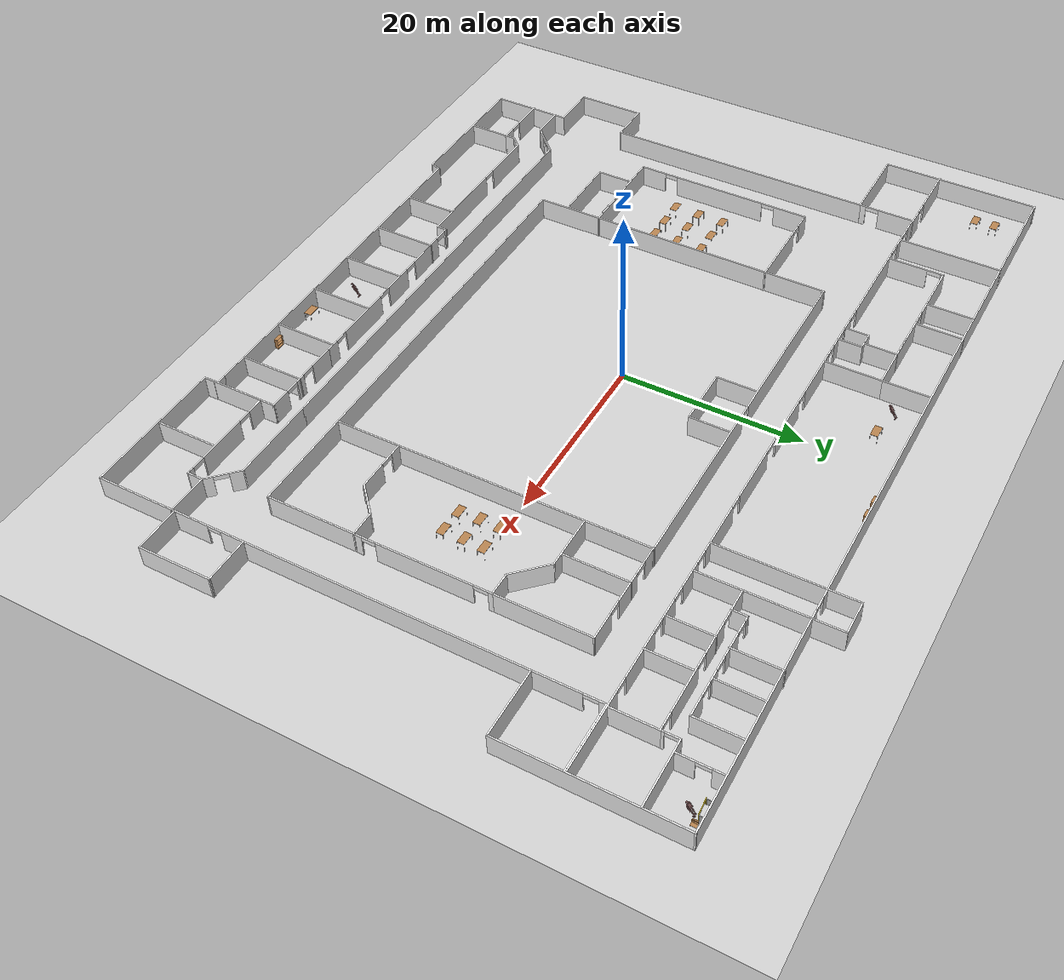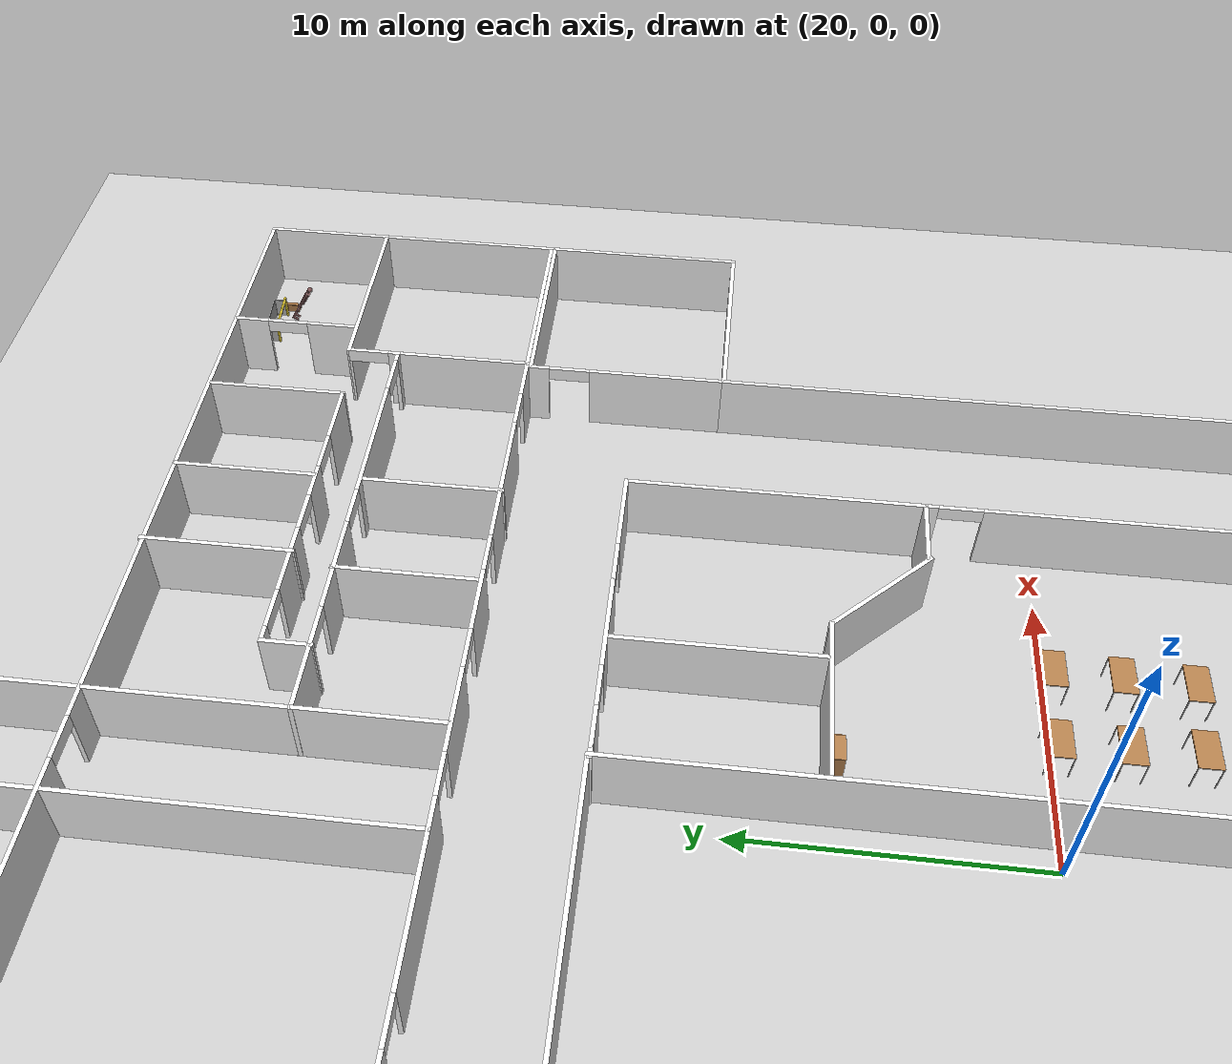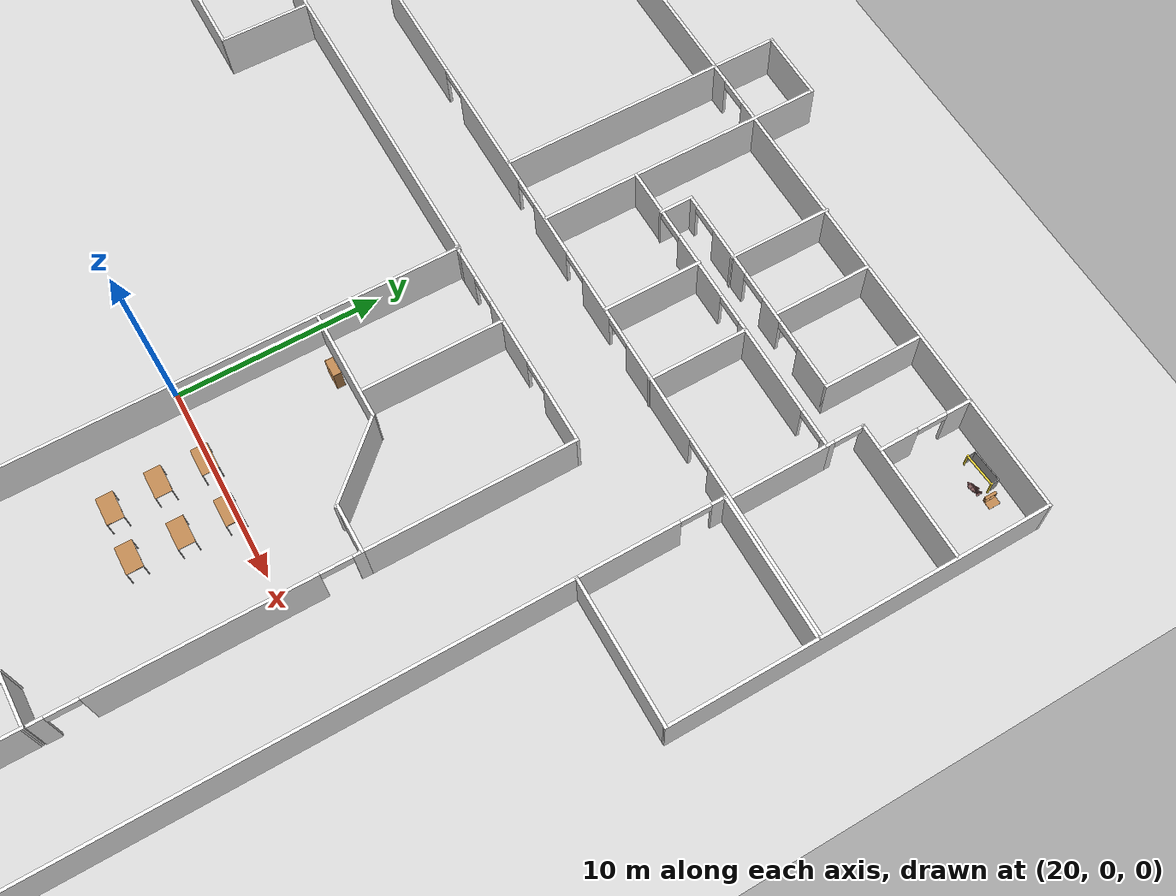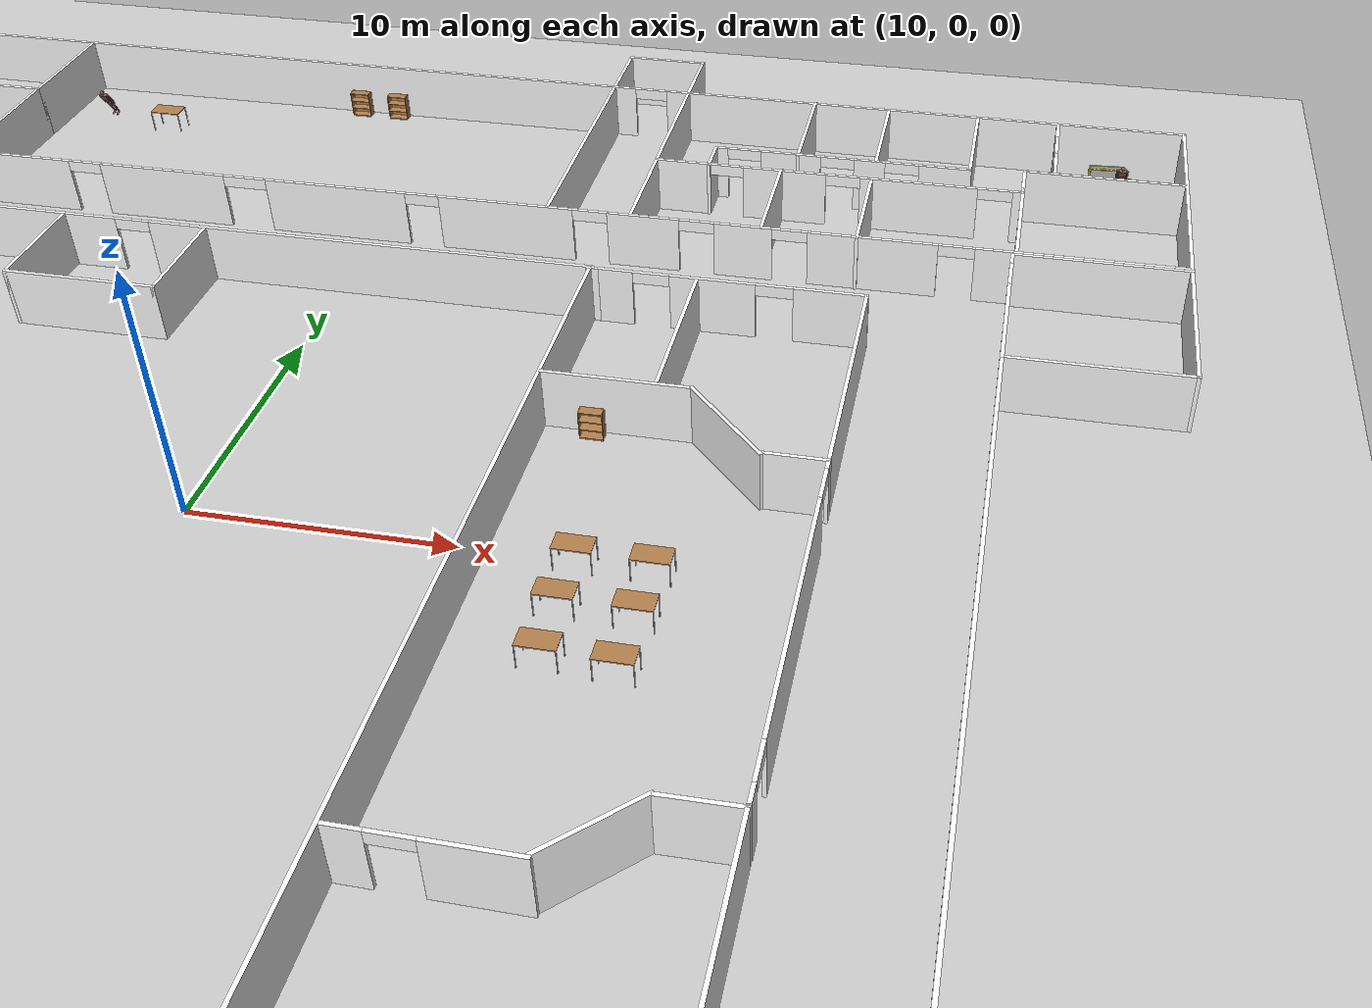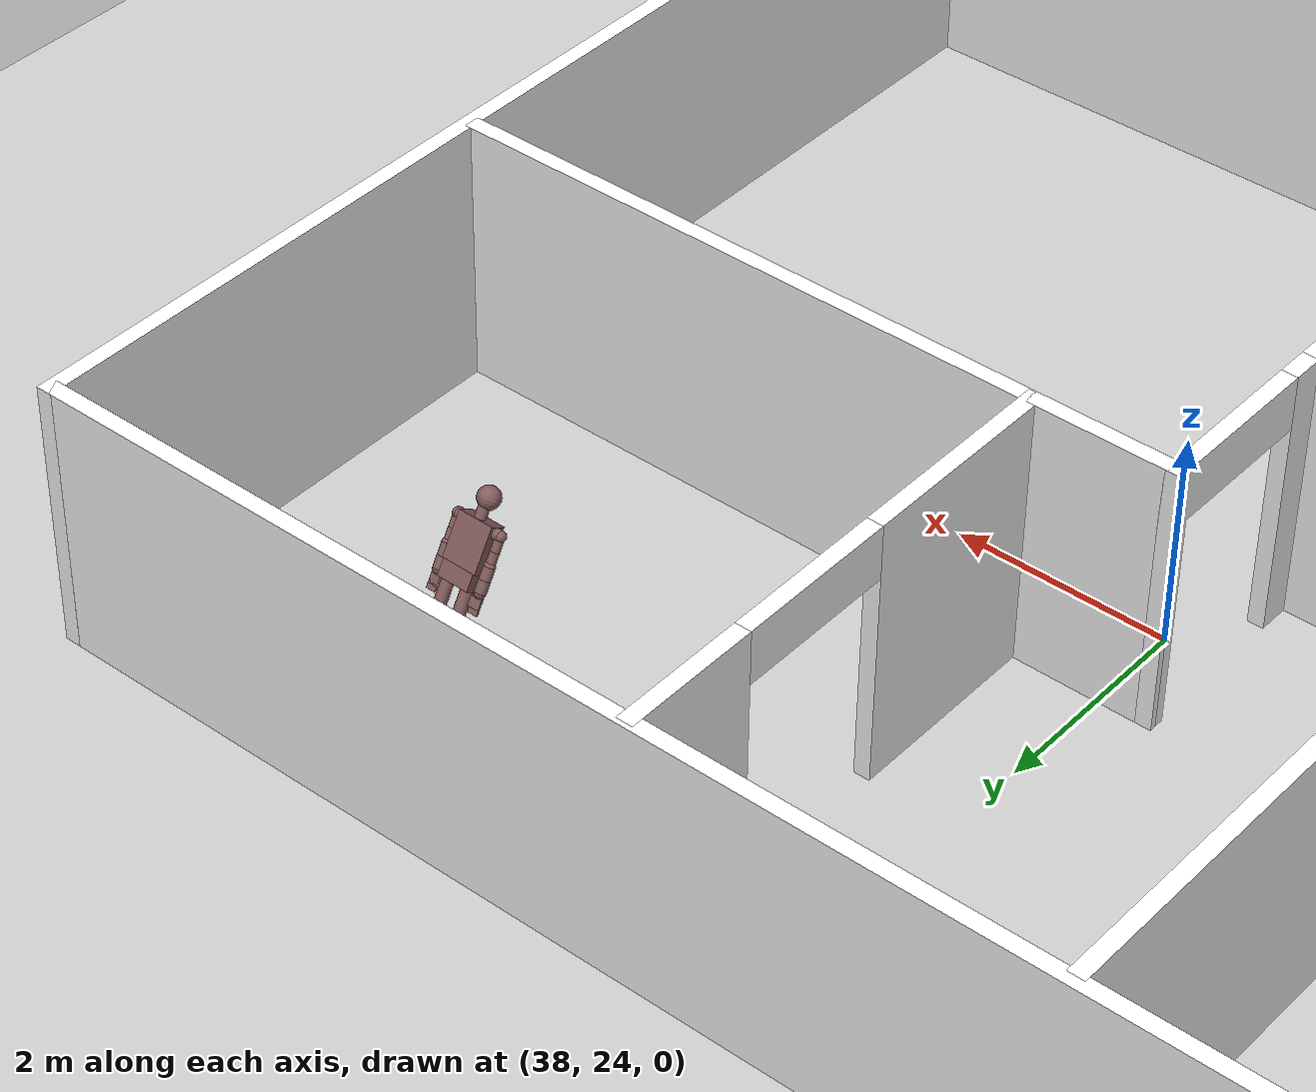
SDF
<sdf version="1.6">
 <world name="default">
  <light name="sun" type="directional">
   <pose>0 0 10 0 -0 0</pose>
   <diffuse>0.8 0.8 0.8 1</diffuse>
   <specular>0.1 0.1 0.1 1</specular>
   <attenuation>
    <range>1000</range>
    <constant>0.9</constant>
    <linear>0.01</linear>
    <quadratic>0.001</quadratic>
   </attenuation>
   <direction>-0.5 0.5 -1</direction>
  </light>
  <model name="ground_plane">
   <static>1</static>
   <link name="link">
    <collision name="collision">
     <geometry><plane><normal>0 0 1</normal><size>100 100</size></plane></geometry>
     <surface><friction><ode><mu>100</mu><mu2>50</mu2></ode></friction></surface>
    </collision>
    <visual name="visual">
     <cast_shadows>0</cast_shadows>
     <geometry><plane><normal>0 0 1</normal><size>100 100</size></plane></geometry>
     <material>
      <script>
       <uri>model://office_env/materials/scripts</uri>
       <uri>model://office_env/materials/textures</uri>
       <name>wall</name>
      </script>
     </material>
    </visual>
   </link>
  </model>
  <gravity>0 0 -9.8</gravity>
  <magnetic_field>6e-06 2.3e-05 -4.2e-05</magnetic_field>
  <atmosphere type="adiabatic"/>
  <physics name="default_physics" default="0" type="ode">
   <max_step_size>0.001</max_step_size>
   <real_time_factor>1</real_time_factor>
   <real_time_update_rate>1000</real_time_update_rate>
  </physics>
  <scene><ambient>0.4 0.4 0.4 1</ambient><background>0.7 0.7 0.7 1</background><shadows>1</shadows></scene>
  <spherical_coordinates>
   <surface_model>EARTH_WGS84</surface_model>
   <latitude_deg>0</latitude_deg>
   <longitude_deg>0</longitude_deg>
   <elevation>0</elevation>
   <heading_deg>0</heading_deg>
  </spherical_coordinates>
  <model name="aule_N">
   <pose>0.1887 -1.4289 0 0 -0 0</pose>
   <link name="Door_6">
    <collision name="Door_6_Collision">
     <geometry><box><size>1.5 0.17 2</size></box></geometry>
     <pose>0 0 1 0 -0 0</pose>
    </collision>
    <visual name="Door_6_Visual">
     <pose>0 0 1 0 -0 0</pose>
     <geometry><box><size>1.5 0.17 2</size></box></geometry>
     <material>
      <script>
       <uri>model://office_env/materials/scripts</uri>
       <uri>model://office_env/materials/textures</uri>
       <name>wall</name>
      </script>
     </material>
    </visual>
    <pose>-21.8785 -12.0586 0 0 -0 0</pose>
   </link>
   <link name="Wall_102">
    <collision name="Wall_102_Collision">
     <geometry><box><size>10.25 0.15 2.5</size></box></geometry>
     <pose>0 0 1.25 0 -0 0</pose>
    </collision>
    <visual name="Wall_102_Visual">
     <pose>0 0 1.25 0 -0 0</pose>
     <geometry><box><size>10.25 0.15 2.5</size></box></geometry>
     <material>
      <script>
       <uri>model://office_env/materials/scripts</uri>
       <uri>model://office_env/materials/textures</uri>
       <name>wall</name>
      </script>
      <ambient>1 1 1 1</ambient>
     </material>
    </visual>
    <pose>31.8169 10.3497 0 0 -0 1.5708</pose>
   </link>
   <link name="Wall_103">
    <pose>26.3919 15.3997 0 0 -0 3.14159</pose>
    <visual name="Wall_103_Visual_0">
     <pose>-4.01282 0 1.25 0 -0 0</pose>
     <geometry><box><size>2.97436 0.15 2.5</size></box></geometry>
     <material>
      <script>
       <uri>model://office_env/materials/scripts</uri>
       <uri>model://office_env/materials/textures</uri>
       <name>wall</name>
      </script>
      <ambient>1 1 1 1</ambient>
     </material>
    </visual>
    <collision name="Wall_103_Collision_0">
     <geometry><box><size>2.97436 0.15 2.5</size></box></geometry>
     <pose>-4.01282 0 1.25 0 -0 0</pose>
    </collision>
    <visual name="Wall_103_Visual_1">
     <pose>0.712222 0 1.25 0 -0 0</pose>
     <geometry><box><size>3.47573 0.15 2.5</size></box></geometry>
     <material>
      <script>
       <uri>model://office_env/materials/scripts</uri>
       <uri>model://office_env/materials/textures</uri>
       <name>wall</name>
      </script>
      <ambient>1 1 1 1</ambient>
     </material>
    </visual>
    <collision name="Wall_103_Collision_1">
     <geometry><box><size>3.47573 0.15 2.5</size></box></geometry>
     <pose>0.712222 0 1.25 0 -0 0</pose>
    </collision>
    <visual name="Wall_103_Visual_2">
     <pose>4.72504 0 1.25 0 -0 0</pose>
     <geometry><box><size>1.54991 0.15 2.5</size></box></geometry>
     <material>
      <script>
       <uri>model://office_env/materials/scripts</uri>
       <uri>model://office_env/materials/textures</uri>
       <name>wall</name>
      </script>
      <ambient>1 1 1 1</ambient>
     </material>
    </visual>
    <collision name="Wall_103_Collision_2">
     <geometry><box><size>1.54991 0.15 2.5</size></box></geometry>
     <pose>4.72504 0 1.25 0 -0 0</pose>
    </collision>
    <visual name="Wall_103_Visual_3">
     <pose>-1.77564 0 2.25 0 -0 0</pose>
     <geometry><box><size>1.5 0.15 0.5</size></box></geometry>
     <material>
      <script>
       <uri>model://office_env/materials/scripts</uri>
       <uri>model://office_env/materials/textures</uri>
       <name>wall</name>
      </script>
      <ambient>1 1 1 1</ambient>
     </material>
    </visual>
    <collision name="Wall_103_Collision_3">
     <geometry><box><size>1.5 0.15 0.5</size></box></geometry>
     <pose>-1.77564 0 2.25 0 -0 0</pose>
    </collision>
    <visual name="Wall_103_Visual_4">
     <pose>3.20009 0 2.25 0 -0 0</pose>
     <geometry><box><size>1.5 0.15 0.5</size></box></geometry>
     <material>
      <script>
       <uri>model://office_env/materials/scripts</uri>
       <uri>model://office_env/materials/textures</uri>
       <name>wall</name>
      </script>
      <ambient>1 1 1 1</ambient>
     </material>
    </visual>
    <collision name="Wall_103_Collision_4">
     <geometry><box><size>1.5 0.15 0.5</size></box></geometry>
     <pose>3.20009 0 2.25 0 -0 0</pose>
    </collision>
   </link>
   <link name="Wall_104">
    <collision name="Wall_104_Collision">
     <geometry><box><size>0.5 0.15 2.5</size></box></geometry>
     <pose>0 0 1.25 0 -0 0</pose>
    </collision>
    <visual name="Wall_104_Visual">
     <pose>0 0 1.25 0 -0 0</pose>
     <geometry><box><size>0.5 0.15 2.5</size></box></geometry>
     <material>
      <script>
       <uri>model://office_env/materials/scripts</uri>
       <uri>model://office_env/materials/textures</uri>
       <name>wall</name>
      </script>
      <ambient>1 1 1 1</ambient>
     </material>
    </visual>
    <pose>20.7919 15.3997 0 0 -0 3.14159</pose>
   </link>
   <link name="Wall_106">
    <collision name="Wall_106_Collision">
     <geometry><box><size>7 0.15 2.5</size></box></geometry>
     <pose>0 0 1.25 0 -0 0</pose>
    </collision>
    <visual name="Wall_106_Visual">
     <pose>0 0 1.25 0 -0 0</pose>
     <geometry><box><size>7 0.15 2.5</size></box></geometry>
     <material>
      <script>
       <uri>model://office_env/materials/scripts</uri>
       <uri>model://office_env/materials/textures</uri>
       <name>wall</name>
      </script>
      <ambient>1 1 1 1</ambient>
     </material>
    </visual>
    <pose>25.0644 11.9766 0 0 0 -1.5708</pose>
   </link>
   <link name="Wall_108">
    <collision name="Wall_108_Collision">
     <geometry><box><size>11.5 0.15 2.5</size></box></geometry>
     <pose>0 0 1.25 0 -0 0</pose>
    </collision>
    <visual name="Wall_108_Visual">
     <pose>0 0 1.25 0 -0 0</pose>
     <geometry><box><size>11.5 0.15 2.5</size></box></geometry>
     <material>
      <script>
       <uri>model://office_env/materials/scripts</uri>
       <uri>model://office_env/materials/textures</uri>
       <name>wall</name>
      </script>
      <ambient>1 1 1 1</ambient>
     </material>
    </visual>
    <pose>-31.5274 25.2751 0 0 0 -1.5708</pose>
   </link>
   <link name="Wall_109">
    <pose>-33.4524 19.6001 0 0 -0 3.14159</pose>
    <visual name="Wall_109_Visual_0">
     <pose>-1.60516 0 1.25 0 -0 0</pose>
     <geometry><box><size>0.789669 0.15 2.5</size></box></geometry>
     <material>
      <script>
       <uri>model://office_env/materials/scripts</uri>
       <uri>model://office_env/materials/textures</uri>
       <name>wall</name>
      </script>
      <ambient>1 1 1 1</ambient>
     </material>
    </visual>
    <collision name="Wall_109_Collision_0">
     <geometry><box><size>0.789669 0.15 2.5</size></box></geometry>
     <pose>-1.60516 0 1.25 0 -0 0</pose>
    </collision>
    <visual name="Wall_109_Visual_1">
     <pose>1.14484 0 1.25 0 -0 0</pose>
     <geometry><box><size>1.71033 0.15 2.5</size></box></geometry>
     <material>
      <script>
       <uri>model://office_env/materials/scripts</uri>
       <uri>model://office_env/materials/textures</uri>
       <name>wall</name>
      </script>
      <ambient>1 1 1 1</ambient>
     </material>
    </visual>
    <collision name="Wall_109_Collision_1">
     <geometry><box><size>1.71033 0.15 2.5</size></box></geometry>
     <pose>1.14484 0 1.25 0 -0 0</pose>
    </collision>
    <visual name="Wall_109_Visual_2">
     <pose>-0.460331 0 2.25 0 -0 0</pose>
     <geometry><box><size>1.5 0.15 0.5</size></box></geometry>
     <material>
      <script>
       <uri>model://office_env/materials/scripts</uri>
       <uri>model://office_env/materials/textures</uri>
       <name>wall</name>
      </script>
      <ambient>1 1 1 1</ambient>
     </material>
    </visual>
    <collision name="Wall_109_Collision_2">
     <geometry><box><size>1.5 0.15 0.5</size></box></geometry>
     <pose>-0.460331 0 2.25 0 -0 0</pose>
    </collision>
   </link>
   <link name="Wall_110">
    <pose>-35.3774 16.4251 0 0 0 -1.5708</pose>
    <visual name="Wall_110_Visual_0">
     <pose>-1.20846 0 1.25 0 -0 0</pose>
     <geometry><box><size>4.08308 0.15 2.5</size></box></geometry>
     <material>
      <script>
       <uri>model://office_env/materials/scripts</uri>
       <uri>model://office_env/materials/textures</uri>
       <name>wall</name>
      </script>
      <ambient>1 1 1 1</ambient>
     </material>
    </visual>
    <collision name="Wall_110_Collision_0">
     <geometry><box><size>4.08308 0.15 2.5</size></box></geometry>
     <pose>-1.20846 0 1.25 0 -0 0</pose>
    </collision>
    <visual name="Wall_110_Visual_1">
     <pose>2.79154 0 1.25 0 -0 0</pose>
     <geometry><box><size>0.91692 0.15 2.5</size></box></geometry>
     <material>
      <script>
       <uri>model://office_env/materials/scripts</uri>
       <uri>model://office_env/materials/textures</uri>
       <name>wall</name>
      </script>
      <ambient>1 1 1 1</ambient>
     </material>
    </visual>
    <collision name="Wall_110_Collision_1">
     <geometry><box><size>0.91692 0.15 2.5</size></box></geometry>
     <pose>2.79154 0 1.25 0 -0 0</pose>
    </collision>
    <visual name="Wall_110_Visual_2">
     <pose>1.58308 0 2.25 0 -0 0</pose>
     <geometry><box><size>1.5 0.15 0.5</size></box></geometry>
     <material>
      <script>
       <uri>model://office_env/materials/scripts</uri>
       <uri>model://office_env/materials/textures</uri>
       <name>wall</name>
      </script>
      <ambient>1 1 1 1</ambient>
     </material>
    </visual>
    <collision name="Wall_110_Collision_2">
     <geometry><box><size>1.5 0.15 0.5</size></box></geometry>
     <pose>1.58308 0 2.25 0 -0 0</pose>
    </collision>
   </link>
   <link name="Wall_112">
    <pose>-39.7703 19.7027 0 0 -0 0</pose>
    <visual name="Wall_112_Visual_0">
     <pose>-1.82458 0 1.25 0 -0 0</pose>
     <geometry><box><size>5.60084 0.15 2.5</size></box></geometry>
     <material>
      <script>
       <uri>model://office_env/materials/scripts</uri>
       <uri>model://office_env/materials/textures</uri>
       <name>wall</name>
      </script>
      <ambient>1 1 1 1</ambient>
     </material>
    </visual>
    <collision name="Wall_112_Collision_0">
     <geometry><box><size>5.60084 0.15 2.5</size></box></geometry>
     <pose>-1.82458 0 1.25 0 -0 0</pose>
    </collision>
    <visual name="Wall_112_Visual_1">
     <pose>3.55042 0 1.25 0 -0 0</pose>
     <geometry><box><size>2.14915 0.15 2.5</size></box></geometry>
     <material>
      <script>
       <uri>model://office_env/materials/scripts</uri>
       <uri>model://office_env/materials/textures</uri>
       <name>wall</name>
      </script>
      <ambient>1 1 1 1</ambient>
     </material>
    </visual>
    <collision name="Wall_112_Collision_1">
     <geometry><box><size>2.14915 0.15 2.5</size></box></geometry>
     <pose>3.55042 0 1.25 0 -0 0</pose>
    </collision>
    <visual name="Wall_112_Visual_2">
     <pose>1.72585 0 2.25 0 -0 0</pose>
     <geometry><box><size>1.5 0.15 0.5</size></box></geometry>
     <material>
      <script>
       <uri>model://office_env/materials/scripts</uri>
       <uri>model://office_env/materials/textures</uri>
       <name>wall</name>
      </script>
      <ambient>1 1 1 1</ambient>
     </material>
    </visual>
    <collision name="Wall_112_Collision_2">
     <geometry><box><size>1.5 0.15 0.5</size></box></geometry>
     <pose>1.72585 0 2.25 0 -0 0</pose>
    </collision>
   </link>
   <link name="Wall_117">
    <pose>-13.2274 19.6001 0 0 -0 0</pose>
    <visual name="Wall_117_Visual_0">
     <pose>-17.7796 0 1.25 0 -0 0</pose>
     <geometry><box><size>1.19077 0.15 2.5</size></box></geometry>
     <material>
      <script>
       <uri>model://office_env/materials/scripts</uri>
       <uri>model://office_env/materials/textures</uri>
       <name>wall</name>
      </script>
      <ambient>1 1 1 1</ambient>
     </material>
    </visual>
    <collision name="Wall_117_Collision_0">
     <geometry><box><size>1.19077 0.15 2.5</size></box></geometry>
     <pose>-17.7796 0 1.25 0 -0 0</pose>
    </collision>
    <visual name="Wall_117_Visual_1">
     <pose>-10.3016 0 1.25 0 -0 0</pose>
     <geometry><box><size>10.7652 0.15 2.5</size></box></geometry>
     <material>
      <script>
       <uri>model://office_env/materials/scripts</uri>
       <uri>model://office_env/materials/textures</uri>
       <name>wall</name>
      </script>
      <ambient>1 1 1 1</ambient>
     </material>
    </visual>
    <collision name="Wall_117_Collision_1">
     <geometry><box><size>10.7652 0.15 2.5</size></box></geometry>
     <pose>-10.3016 0 1.25 0 -0 0</pose>
    </collision>
    <visual name="Wall_117_Visual_2">
     <pose>-2.44962 0 1.25 0 -0 0</pose>
     <geometry><box><size>1.93872 0.15 2.5</size></box></geometry>
     <material>
      <script>
       <uri>model://office_env/materials/scripts</uri>
       <uri>model://office_env/materials/textures</uri>
       <name>wall</name>
      </script>
      <ambient>1 1 1 1</ambient>
     </material>
    </visual>
    <collision name="Wall_117_Collision_2">
     <geometry><box><size>1.93872 0.15 2.5</size></box></geometry>
     <pose>-2.44962 0 1.25 0 -0 0</pose>
    </collision>
    <visual name="Wall_117_Visual_3">
     <pose>0.6526 0 1.25 0 -0 0</pose>
     <geometry><box><size>1.26572 0.15 2.5</size></box></geometry>
     <material>
      <script>
       <uri>model://office_env/materials/scripts</uri>
       <uri>model://office_env/materials/textures</uri>
       <name>wall</name>
      </script>
      <ambient>1 1 1 1</ambient>
     </material>
    </visual>
    <collision name="Wall_117_Collision_3">
     <geometry><box><size>1.26572 0.15 2.5</size></box></geometry>
     <pose>0.6526 0 1.25 0 -0 0</pose>
    </collision>
    <visual name="Wall_117_Visual_4">
     <pose>5.87513 0 1.25 0 -0 0</pose>
     <geometry><box><size>6.17934 0.15 2.5</size></box></geometry>
     <material>
      <script>
       <uri>model://office_env/materials/scripts</uri>
       <uri>model://office_env/materials/textures</uri>
       <name>wall</name>
      </script>
      <ambient>1 1 1 1</ambient>
     </material>
    </visual>
    <collision name="Wall_117_Collision_4">
     <geometry><box><size>6.17934 0.15 2.5</size></box></geometry>
     <pose>5.87513 0 1.25 0 -0 0</pose>
    </collision>
    <visual name="Wall_117_Visual_5">
     <pose>13.3706 0 1.25 0 -0 0</pose>
     <geometry><box><size>5.81158 0.15 2.5</size></box></geometry>
     <material>
      <script>
       <uri>model://office_env/materials/scripts</uri>
       <uri>model://office_env/materials/textures</uri>
       <name>wall</name>
      </script>
      <ambient>1 1 1 1</ambient>
     </material>
    </visual>
    <collision name="Wall_117_Collision_5">
     <geometry><box><size>5.81158 0.15 2.5</size></box></geometry>
     <pose>13.3706 0 1.25 0 -0 0</pose>
    </collision>
    <visual name="Wall_117_Visual_6">
     <pose>-16.4342 0 2.25 0 -0 0</pose>
     <geometry><box><size>1.5 0.15 0.5</size></box></geometry>
     <material>
      <script>
       <uri>model://office_env/materials/scripts</uri>
       <uri>model://office_env/materials/textures</uri>
       <name>wall</name>
      </script>
      <ambient>1 1 1 1</ambient>
     </material>
    </visual>
    <collision name="Wall_117_Collision_6">
     <geometry><box><size>1.5 0.15 0.5</size></box></geometry>
     <pose>-16.4342 0 2.25 0 -0 0</pose>
    </collision>
    <visual name="Wall_117_Visual_7">
     <pose>-4.16898 0 2.25 0 -0 0</pose>
     <geometry><box><size>1.5 0.15 0.5</size></box></geometry>
     <material>
      <script>
       <uri>model://office_env/materials/scripts</uri>
       <uri>model://office_env/materials/textures</uri>
       <name>wall</name>
      </script>
      <ambient>1 1 1 1</ambient>
     </material>
    </visual>
    <collision name="Wall_117_Collision_7">
     <geometry><box><size>1.5 0.15 0.5</size></box></geometry>
     <pose>-4.16898 0 2.25 0 -0 0</pose>
    </collision>
    <visual name="Wall_117_Visual_8">
     <pose>-0.73026 0 2.25 0 -0 0</pose>
     <geometry><box><size>1.5 0.15 0.5</size></box></geometry>
     <material>
      <script>
       <uri>model://office_env/materials/scripts</uri>
       <uri>model://office_env/materials/textures</uri>
       <name>wall</name>
      </script>
      <ambient>1 1 1 1</ambient>
     </material>
    </visual>
    <collision name="Wall_117_Collision_8">
     <geometry><box><size>1.5 0.15 0.5</size></box></geometry>
     <pose>-0.73026 0 2.25 0 -0 0</pose>
    </collision>
    <visual name="Wall_117_Visual_9">
     <pose>2.03546 0 2.25 0 -0 0</pose>
     <geometry><box><size>1.5 0.15 0.5</size></box></geometry>
     <material>
      <script>
       <uri>model://office_env/materials/scripts</uri>
       <uri>model://office_env/materials/textures</uri>
       <name>wall</name>
      </script>
      <ambient>1 1 1 1</ambient>
     </material>
    </visual>
    <collision name="Wall_117_Collision_9">
     <geometry><box><size>1.5 0.15 0.5</size></box></geometry>
     <pose>2.03546 0 2.25 0 -0 0</pose>
    </collision>
    <visual name="Wall_117_Visual_10">
     <pose>9.7148 0 2.25 0 -0 0</pose>
     <geometry><box><size>1.5 0.15 0.5</size></box></geometry>
     <material>
      <script>
       <uri>model://office_env/materials/scripts</uri>
       <uri>model://office_env/materials/textures</uri>
       <name>wall</name>
      </script>
      <ambient>1 1 1 1</ambient>
     </material>
    </visual>
    <collision name="Wall_117_Collision_10">
     <geometry><box><size>1.5 0.15 0.5</size></box></geometry>
     <pose>9.7148 0 2.25 0 -0 0</pose>
    </collision>
    <visual name="Wall_117_Visual_11">
     <pose>17.3257 0 2.25 0 -0 0</pose>
     <geometry><box><size>2.09862 0.15 0.5</size></box></geometry>
     <material>
      <script>
       <uri>model://office_env/materials/scripts</uri>
       <uri>model://office_env/materials/textures</uri>
       <name>wall</name>
      </script>
      <ambient>1 1 1 1</ambient>
     </material>
    </visual>
    <collision name="Wall_117_Collision_11">
     <geometry><box><size>2.09862 0.15 0.5</size></box></geometry>
     <pose>17.3257 0 2.25 0 -0 0</pose>
    </collision>
   </link>
   <link name="Wall_119">
    <pose>24.6226 19.6001 0 0 -0 0</pose>
    <visual name="Wall_119_Visual_0">
     <pose>-16.4435 0 1.25 0 -0 0</pose>
     <geometry><box><size>6.36296 0.15 2.5</size></box></geometry>
     <material>
      <script>
       <uri>model://office_env/materials/scripts</uri>
       <uri>model://office_env/materials/textures</uri>
       <name>wall</name>
      </script>
      <ambient>1 1 1 1</ambient>
     </material>
    </visual>
    <collision name="Wall_119_Collision_0">
     <geometry><box><size>6.36296 0.15 2.5</size></box></geometry>
     <pose>-16.4435 0 1.25 0 -0 0</pose>
    </collision>
    <visual name="Wall_119_Visual_1">
     <pose>-8.80227 0 1.25 0 -0 0</pose>
     <geometry><box><size>5.91956 0.15 2.5</size></box></geometry>
     <material>
      <script>
       <uri>model://office_env/materials/scripts</uri>
       <uri>model://office_env/materials/textures</uri>
       <name>wall</name>
      </script>
      <ambient>1 1 1 1</ambient>
     </material>
    </visual>
    <collision name="Wall_119_Collision_1">
     <geometry><box><size>5.91956 0.15 2.5</size></box></geometry>
     <pose>-8.80227 0 1.25 0 -0 0</pose>
    </collision>
    <visual name="Wall_119_Visual_2">
     <pose>-2.80072 0 1.25 0 -0 0</pose>
     <geometry><box><size>3.08352 0.15 2.5</size></box></geometry>
     <material>
      <script>
       <uri>model://office_env/materials/scripts</uri>
       <uri>model://office_env/materials/textures</uri>
       <name>wall</name>
      </script>
      <ambient>1 1 1 1</ambient>
     </material>
    </visual>
    <collision name="Wall_119_Collision_2">
     <geometry><box><size>3.08352 0.15 2.5</size></box></geometry>
     <pose>-2.80072 0 1.25 0 -0 0</pose>
    </collision>
    <visual name="Wall_119_Visual_3">
     <pose>1.4683 0 1.25 0 -0 0</pose>
     <geometry><box><size>2.45453 0.15 2.5</size></box></geometry>
     <material>
      <script>
       <uri>model://office_env/materials/scripts</uri>
       <uri>model://office_env/materials/textures</uri>
       <name>wall</name>
      </script>
      <ambient>1 1 1 1</ambient>
     </material>
    </visual>
    <collision name="Wall_119_Collision_3">
     <geometry><box><size>2.45453 0.15 2.5</size></box></geometry>
     <pose>1.4683 0 1.25 0 -0 0</pose>
    </collision>
    <visual name="Wall_119_Visual_4">
     <pose>6.88834 0 1.25 0 -0 0</pose>
     <geometry><box><size>5.38554 0.15 2.5</size></box></geometry>
     <material>
      <script>
       <uri>model://office_env/materials/scripts</uri>
       <uri>model://office_env/materials/textures</uri>
       <name>wall</name>
      </script>
      <ambient>1 1 1 1</ambient>
     </material>
    </visual>
    <collision name="Wall_119_Collision_4">
     <geometry><box><size>5.38554 0.15 2.5</size></box></geometry>
     <pose>6.88834 0 1.25 0 -0 0</pose>
    </collision>
    <visual name="Wall_119_Visual_5">
     <pose>15.3531 0 1.25 0 -0 0</pose>
     <geometry><box><size>8.54389 0.15 2.5</size></box></geometry>
     <material>
      <script>
       <uri>model://office_env/materials/scripts</uri>
       <uri>model://office_env/materials/textures</uri>
       <name>wall</name>
      </script>
      <ambient>1 1 1 1</ambient>
     </material>
    </visual>
    <collision name="Wall_119_Collision_5">
     <geometry><box><size>8.54389 0.15 2.5</size></box></geometry>
     <pose>15.3531 0 1.25 0 -0 0</pose>
    </collision>
    <visual name="Wall_119_Visual_6">
     <pose>-12.512 0 2.25 0 -0 0</pose>
     <geometry><box><size>1.5 0.15 0.5</size></box></geometry>
     <material>
      <script>
       <uri>model://office_env/materials/scripts</uri>
       <uri>model://office_env/materials/textures</uri>
       <name>wall</name>
      </script>
      <ambient>1 1 1 1</ambient>
     </material>
    </visual>
    <collision name="Wall_119_Collision_6">
     <geometry><box><size>1.5 0.15 0.5</size></box></geometry>
     <pose>-12.512 0 2.25 0 -0 0</pose>
    </collision>
    <visual name="Wall_119_Visual_7">
     <pose>-5.09248 0 2.25 0 -0 0</pose>
     <geometry><box><size>1.5 0.15 0.5</size></box></geometry>
     <material>
      <script>
       <uri>model://office_env/materials/scripts</uri>
       <uri>model://office_env/materials/textures</uri>
       <name>wall</name>
      </script>
      <ambient>1 1 1 1</ambient>
     </material>
    </visual>
    <collision name="Wall_119_Collision_7">
     <geometry><box><size>1.5 0.15 0.5</size></box></geometry>
     <pose>-5.09248 0 2.25 0 -0 0</pose>
    </collision>
    <visual name="Wall_119_Visual_8">
     <pose>-0.508963 0 2.25 0 -0 0</pose>
     <geometry><box><size>1.5 0.15 0.5</size></box></geometry>
     <material>
      <script>
       <uri>model://office_env/materials/scripts</uri>
       <uri>model://office_env/materials/textures</uri>
       <name>wall</name>
      </script>
      <ambient>1 1 1 1</ambient>
     </material>
    </visual>
    <collision name="Wall_119_Collision_8">
     <geometry><box><size>1.5 0.15 0.5</size></box></geometry>
     <pose>-0.508963 0 2.25 0 -0 0</pose>
    </collision>
    <visual name="Wall_119_Visual_9">
     <pose>3.44557 0 2.25 0 -0 0</pose>
     <geometry><box><size>1.5 0.15 0.5</size></box></geometry>
     <material>
      <script>
       <uri>model://office_env/materials/scripts</uri>
       <uri>model://office_env/materials/textures</uri>
       <name>wall</name>
      </script>
      <ambient>1 1 1 1</ambient>
     </material>
    </visual>
    <collision name="Wall_119_Collision_9">
     <geometry><box><size>1.5 0.15 0.5</size></box></geometry>
     <pose>3.44557 0 2.25 0 -0 0</pose>
    </collision>
    <visual name="Wall_119_Visual_10">
     <pose>10.3311 0 2.25 0 -0 0</pose>
     <geometry><box><size>1.5 0.15 0.5</size></box></geometry>
     <material>
      <script>
       <uri>model://office_env/materials/scripts</uri>
       <uri>model://office_env/materials/textures</uri>
       <name>wall</name>
      </script>
      <ambient>1 1 1 1</ambient>
     </material>
    </visual>
    <collision name="Wall_119_Collision_10">
     <geometry><box><size>1.5 0.15 0.5</size></box></geometry>
     <pose>10.3311 0 2.25 0 -0 0</pose>
    </collision>
   </link>
   <link name="Wall_121">
    <collision name="Wall_121_Collision">
     <geometry><box><size>5.25 0.15 2.5</size></box></geometry>
     <pose>0 0 1.25 0 -0 0</pose>
    </collision>
    <visual name="Wall_121_Visual">
     <pose>0 0 1.25 0 -0 0</pose>
     <geometry><box><size>5.25 0.15 2.5</size></box></geometry>
     <material>
      <script>
       <uri>model://office_env/materials/scripts</uri>
       <uri>model://office_env/materials/textures</uri>
       <name>wall</name>
      </script>
      <ambient>1 1 1 1</ambient>
     </material>
    </visual>
    <pose>-22.5458 28.3464 0 0 0 -1.5708</pose>
   </link>
   <link name="Wall_122">
    <collision name="Wall_122_Collision">
     <geometry><box><size>5.5 0.15 2.5</size></box></geometry>
     <pose>0 0 1.25 0 -0 0</pose>
    </collision>
    <visual name="Wall_122_Visual">
     <pose>0 0 1.25 0 -0 0</pose>
     <geometry><box><size>5.5 0.15 2.5</size></box></geometry>
     <material>
      <script>
       <uri>model://office_env/materials/scripts</uri>
       <uri>model://office_env/materials/textures</uri>
       <name>wall</name>
      </script>
      <ambient>1 1 1 1</ambient>
     </material>
    </visual>
    <pose>-25.2208 25.7964 0 0 -0 3.14159</pose>
   </link>
   <link name="Wall_123">
    <pose>-27.8958 22.7464 0 0 0 -1.5708</pose>
    <visual name="Wall_123_Visual_0">
     <pose>-2.93611 0 1.25 0 -0 0</pose>
     <geometry><box><size>0.377789 0.15 2.5</size></box></geometry>
     <material>
      <script>
       <uri>model://office_env/materials/scripts</uri>
       <uri>model://office_env/materials/textures</uri>
       <name>wall</name>
      </script>
      <ambient>1 1 1 1</ambient>
     </material>
    </visual>
    <collision name="Wall_123_Collision_0">
     <geometry><box><size>0.377789 0.15 2.5</size></box></geometry>
     <pose>-2.93611 0 1.25 0 -0 0</pose>
    </collision>
    <visual name="Wall_123_Visual_1">
     <pose>0.938894 0 1.25 0 -0 0</pose>
     <geometry><box><size>4.37221 0.15 2.5</size></box></geometry>
     <material>
      <script>
       <uri>model://office_env/materials/scripts</uri>
       <uri>model://office_env/materials/textures</uri>
       <name>wall</name>
      </script>
      <ambient>1 1 1 1</ambient>
     </material>
    </visual>
    <collision name="Wall_123_Collision_1">
     <geometry><box><size>4.37221 0.15 2.5</size></box></geometry>
     <pose>0.938894 0 1.25 0 -0 0</pose>
    </collision>
    <visual name="Wall_123_Visual_2">
     <pose>-1.99721 0 2.25 0 -0 0</pose>
     <geometry><box><size>1.5 0.15 0.5</size></box></geometry>
     <material>
      <script>
       <uri>model://office_env/materials/scripts</uri>
       <uri>model://office_env/materials/textures</uri>
       <name>wall</name>
      </script>
      <ambient>1 1 1 1</ambient>
     </material>
    </visual>
    <collision name="Wall_123_Collision_2">
     <geometry><box><size>1.5 0.15 0.5</size></box></geometry>
     <pose>-1.99721 0 2.25 0 -0 0</pose>
    </collision>
   </link>
   <link name="Wall_125">
    <pose>-18.1208 25.7964 0 0 -0 0</pose>
    <visual name="Wall_125_Visual_0">
     <pose>-3.65851 0 1.25 0 -0 0</pose>
     <geometry><box><size>1.68298 0.15 2.5</size></box></geometry>
     <material>
      <script>
       <uri>model://office_env/materials/scripts</uri>
       <uri>model://office_env/materials/textures</uri>
       <name>wall</name>
      </script>
      <ambient>1 1 1 1</ambient>
     </material>
    </visual>
    <collision name="Wall_125_Collision_0">
     <geometry><box><size>1.68298 0.15 2.5</size></box></geometry>
     <pose>-3.65851 0 1.25 0 -0 0</pose>
    </collision>
    <visual name="Wall_125_Visual_1">
     <pose>1.59149 0 1.25 0 -0 0</pose>
     <geometry><box><size>5.81702 0.15 2.5</size></box></geometry>
     <material>
      <script>
       <uri>model://office_env/materials/scripts</uri>
       <uri>model://office_env/materials/textures</uri>
       <name>wall</name>
      </script>
      <ambient>1 1 1 1</ambient>
     </material>
    </visual>
    <collision name="Wall_125_Collision_1">
     <geometry><box><size>5.81702 0.15 2.5</size></box></geometry>
     <pose>1.59149 0 1.25 0 -0 0</pose>
    </collision>
    <visual name="Wall_125_Visual_2">
     <pose>-2.06702 0 2.25 0 -0 0</pose>
     <geometry><box><size>1.5 0.15 0.5</size></box></geometry>
     <material>
      <script>
       <uri>model://office_env/materials/scripts</uri>
       <uri>model://office_env/materials/textures</uri>
       <name>wall</name>
      </script>
      <ambient>1 1 1 1</ambient>
     </material>
    </visual>
    <collision name="Wall_125_Collision_2">
     <geometry><box><size>1.5 0.15 0.5</size></box></geometry>
     <pose>-2.06702 0 2.25 0 -0 0</pose>
    </collision>
   </link>
   <link name="Wall_126">
    <collision name="Wall_126_Collision">
     <geometry><box><size>3.75 0.15 2.5</size></box></geometry>
     <pose>0 0 1.25 0 -0 0</pose>
    </collision>
    <visual name="Wall_126_Visual">
     <pose>0 0 1.25 0 -0 0</pose>
     <geometry><box><size>3.75 0.15 2.5</size></box></geometry>
     <material>
      <script>
       <uri>model://office_env/materials/scripts</uri>
       <uri>model://office_env/materials/textures</uri>
       <name>wall</name>
      </script>
      <ambient>1 1 1 1</ambient>
     </material>
    </visual>
    <pose>-13.6958 23.9964 0 0 0 -1.5708</pose>
   </link>
   <link name="Wall_127">
    <collision name="Wall_127_Collision">
     <geometry><box><size>1.5 0.15 2.5</size></box></geometry>
     <pose>0 0 1.25 0 -0 0</pose>
    </collision>
    <visual name="Wall_127_Visual">
     <pose>0 0 1.25 0 -0 0</pose>
     <geometry><box><size>1.5 0.15 2.5</size></box></geometry>
     <material>
      <script>
       <uri>model://office_env/materials/scripts</uri>
       <uri>model://office_env/materials/textures</uri>
       <name>wall</name>
      </script>
      <ambient>1 1 1 1</ambient>
     </material>
    </visual>
    <pose>-14.3708 22.1964 0 0 -0 3.14159</pose>
   </link>
   <link name="Wall_128">
    <collision name="Wall_128_Collision">
     <geometry><box><size>2.75 0.15 2.5</size></box></geometry>
     <pose>0 0 1.25 0 -0 0</pose>
    </collision>
    <visual name="Wall_128_Visual">
     <pose>0 0 1.25 0 -0 0</pose>
     <geometry><box><size>2.75 0.15 2.5</size></box></geometry>
     <material>
      <script>
       <uri>model://office_env/materials/scripts</uri>
       <uri>model://office_env/materials/textures</uri>
       <name>wall</name>
      </script>
      <ambient>1 1 1 1</ambient>
     </material>
    </visual>
    <pose>-15.0458 20.8964 0 0 0 -1.5708</pose>
   </link>
   <link name="Wall_13">
    <collision name="Wall_13_Collision">
     <geometry><box><size>17.75 0.15 2.5</size></box></geometry>
     <pose>0 0 1.25 0 -0 0</pose>
    </collision>
    <visual name="Wall_13_Visual">
     <pose>0 0 1.25 0 -0 0</pose>
     <geometry><box><size>17.75 0.15 2.5</size></box></geometry>
     <material>
      <script>
       <uri>model://office_env/materials/scripts</uri>
       <uri>model://office_env/materials/textures</uri>
       <name>wall</name>
      </script>
      <ambient>1 1 1 1</ambient>
     </material>
    </visual>
    <pose>-44.2144 22.183 0 0 0 -1.5708</pose>
   </link>
   <link name="Wall_130">
    <collision name="Wall_130_Collision">
     <geometry><box><size>5.25 0.15 2.5</size></box></geometry>
     <pose>0 0 1.25 0 -0 0</pose>
    </collision>
    <visual name="Wall_130_Visual">
     <pose>0 0 1.25 0 -0 0</pose>
     <geometry><box><size>5.25 0.15 2.5</size></box></geometry>
     <material>
      <script>
       <uri>model://office_env/materials/scripts</uri>
       <uri>model://office_env/materials/textures</uri>
       <name>wall</name>
      </script>
      <ambient>1 1 1 1</ambient>
     </material>
    </visual>
    <pose>-19.0551 28.4267 0 0 0 -1.5708</pose>
   </link>
   <link name="Wall_132">
    <collision name="Wall_132_Collision">
     <geometry><box><size>0.75 0.15 2.5</size></box></geometry>
     <pose>0 0 1.25 0 -0 0</pose>
    </collision>
    <visual name="Wall_132_Visual">
     <pose>0 0 1.25 0 -0 0</pose>
     <geometry><box><size>0.75 0.15 2.5</size></box></geometry>
     <material>
      <script>
       <uri>model://office_env/materials/scripts</uri>
       <uri>model://office_env/materials/textures</uri>
       <name>wall</name>
      </script>
      <ambient>1 1 1 1</ambient>
     </material>
    </visual>
    <pose>-13.3958 22.1964 0 0 -0 0</pose>
   </link>
   <link name="Wall_133">
    <collision name="Wall_133_Collision">
     <geometry><box><size>2.75 0.15 2.5</size></box></geometry>
     <pose>0 0 1.25 0 -0 0</pose>
    </collision>
    <visual name="Wall_133_Visual">
     <pose>0 0 1.25 0 -0 0</pose>
     <geometry><box><size>2.75 0.15 2.5</size></box></geometry>
     <material>
      <script>
       <uri>model://office_env/materials/scripts</uri>
       <uri>model://office_env/materials/textures</uri>
       <name>wall</name>
      </script>
      <ambient>1 1 1 1</ambient>
     </material>
    </visual>
    <pose>-13.0958 20.8964 0 0 0 -1.5708</pose>
   </link>
   <link name="Wall_135">
    <pose>-12.9035 25.7612 0 0 -0 0</pose>
    <visual name="Wall_135_Visual_0">
     <pose>-3.3201 0 1.25 0 -0 0</pose>
     <geometry><box><size>0.60979 0.15 2.5</size></box></geometry>
     <material>
      <script>
       <uri>model://office_env/materials/scripts</uri>
       <uri>model://office_env/materials/textures</uri>
       <name>wall</name>
      </script>
      <ambient>1 1 1 1</ambient>
     </material>
    </visual>
    <collision name="Wall_135_Collision_0">
     <geometry><box><size>0.60979 0.15 2.5</size></box></geometry>
     <pose>-3.3201 0 1.25 0 -0 0</pose>
    </collision>
    <visual name="Wall_135_Visual_1">
     <pose>1.05489 0 1.25 0 -0 0</pose>
     <geometry><box><size>5.14021 0.15 2.5</size></box></geometry>
     <material>
      <script>
       <uri>model://office_env/materials/scripts</uri>
       <uri>model://office_env/materials/textures</uri>
       <name>wall</name>
      </script>
      <ambient>1 1 1 1</ambient>
     </material>
    </visual>
    <collision name="Wall_135_Collision_1">
     <geometry><box><size>5.14021 0.15 2.5</size></box></geometry>
     <pose>1.05489 0 1.25 0 -0 0</pose>
    </collision>
    <visual name="Wall_135_Visual_2">
     <pose>-2.26521 0 2.25 0 -0 0</pose>
     <geometry><box><size>1.5 0.15 0.5</size></box></geometry>
     <material>
      <script>
       <uri>model://office_env/materials/scripts</uri>
       <uri>model://office_env/materials/textures</uri>
       <name>wall</name>
      </script>
      <ambient>1 1 1 1</ambient>
     </material>
    </visual>
    <collision name="Wall_135_Collision_2">
     <geometry><box><size>1.5 0.15 0.5</size></box></geometry>
     <pose>-2.26521 0 2.25 0 -0 0</pose>
    </collision>
   </link>
   <link name="Wall_136">
    <collision name="Wall_136_Collision">
     <geometry><box><size>5.25 0.15 2.5</size></box></geometry>
     <pose>0 0 1.25 0 -0 0</pose>
    </collision>
    <visual name="Wall_136_Visual">
     <pose>0 0 1.25 0 -0 0</pose>
     <geometry><box><size>5.25 0.15 2.5</size></box></geometry>
     <material>
      <script>
       <uri>model://office_env/materials/scripts</uri>
       <uri>model://office_env/materials/textures</uri>
       <name>wall</name>
      </script>
      <ambient>1 1 1 1</ambient>
     </material>
    </visual>
    <pose>-9.35351 28.3112 0 0 -0 1.5708</pose>
   </link>
   <link name="Wall_138">
    <collision name="Wall_138_Collision">
     <geometry><box><size>6.25 0.15 2.5</size></box></geometry>
     <pose>0 0 1.25 0 -0 0</pose>
    </collision>
    <visual name="Wall_138_Visual">
     <pose>0 0 1.25 0 -0 0</pose>
     <geometry><box><size>6.25 0.15 2.5</size></box></geometry>
     <material>
      <script>
       <uri>model://office_env/materials/scripts</uri>
       <uri>model://office_env/materials/textures</uri>
       <name>wall</name>
      </script>
      <ambient>1 1 1 1</ambient>
     </material>
    </visual>
    <pose>-9.35351 22.7112 0 0 0 -1.5708</pose>
   </link>
   <link name="Wall_14">
    <collision name="Wall_14_Collision">
     <geometry><box><size>9 0.15 2.5</size></box></geometry>
     <pose>0 0 1.25 0 -0 0</pose>
    </collision>
    <visual name="Wall_14_Visual">
     <pose>0 0 1.25 0 -0 0</pose>
     <geometry><box><size>9 0.15 2.5</size></box></geometry>
     <material>
      <script>
       <uri>model://office_env/materials/scripts</uri>
       <uri>model://office_env/materials/textures</uri>
       <name>wall</name>
      </script>
      <ambient>1 1 1 1</ambient>
     </material>
    </visual>
    <pose>-39.7894 13.383 0 0 -0 0</pose>
   </link>
   <link name="Wall_142">
    <collision name="Wall_142_Collision">
     <geometry><box><size>14.75 0.15 2.5</size></box></geometry>
     <pose>0 0 1.25 0 -0 0</pose>
    </collision>
    <visual name="Wall_142_Visual">
     <pose>0 0 1.25 0 -0 0</pose>
     <geometry><box><size>14.75 0.15 2.5</size></box></geometry>
     <material>
      <script>
       <uri>model://office_env/materials/scripts</uri>
       <uri>model://office_env/materials/textures</uri>
       <name>wall</name>
      </script>
      <ambient>1 1 1 1</ambient>
     </material>
    </visual>
    <pose>17.6842 26.9006 0 0 -0 1.5708</pose>
   </link>
   <link name="Wall_143">
    <collision name="Wall_143_Collision">
     <geometry><box><size>3.75 0.15 2.5</size></box></geometry>
     <pose>0 0 1.25 0 -0 0</pose>
    </collision>
    <visual name="Wall_143_Visual">
     <pose>0 0 1.25 0 -0 0</pose>
     <geometry><box><size>3.75 0.15 2.5</size></box></geometry>
     <material>
      <script>
       <uri>model://office_env/materials/scripts</uri>
       <uri>model://office_env/materials/textures</uri>
       <name>wall</name>
      </script>
      <ambient>1 1 1 1</ambient>
     </material>
    </visual>
    <pose>19.4842 34.2006 0 0 -0 0</pose>
   </link>
   <link name="Wall_144">
    <collision name="Wall_144_Collision">
     <geometry><box><size>14.75 0.15 2.5</size></box></geometry>
     <pose>0 0 1.25 0 -0 0</pose>
    </collision>
    <visual name="Wall_144_Visual">
     <pose>0 0 1.25 0 -0 0</pose>
     <geometry><box><size>14.75 0.15 2.5</size></box></geometry>
     <material>
      <script>
       <uri>model://office_env/materials/scripts</uri>
       <uri>model://office_env/materials/textures</uri>
       <name>wall</name>
      </script>
      <ambient>1 1 1 1</ambient>
     </material>
    </visual>
    <pose>21.2842 26.9006 0 0 0 -1.5708</pose>
   </link>
   <link name="Wall_147">
    <collision name="Wall_147_Collision">
     <geometry><box><size>4.5 0.15 2.5</size></box></geometry>
     <pose>0 0 1.25 0 -0 0</pose>
    </collision>
    <visual name="Wall_147_Visual">
     <pose>0 0 1.25 0 -0 0</pose>
     <geometry><box><size>4.5 0.15 2.5</size></box></geometry>
     <material>
      <script>
       <uri>model://office_env/materials/scripts</uri>
       <uri>model://office_env/materials/textures</uri>
       <name>wall</name>
      </script>
      <ambient>1 1 1 1</ambient>
     </material>
    </visual>
    <pose>-2.1259 13.1481 0 0 0 -1.5708</pose>
   </link>
   <link name="Wall_148">
    <collision name="Wall_148_Collision">
     <geometry><box><size>6.5 0.15 2.5</size></box></geometry>
     <pose>0 0 1.25 0 -0 0</pose>
    </collision>
    <visual name="Wall_148_Visual">
     <pose>0 0 1.25 0 -0 0</pose>
     <geometry><box><size>6.5 0.15 2.5</size></box></geometry>
     <material>
      <script>
       <uri>model://office_env/materials/scripts</uri>
       <uri>model://office_env/materials/textures</uri>
       <name>wall</name>
      </script>
      <ambient>1 1 1 1</ambient>
     </material>
    </visual>
    <pose>1.0491 10.9731 0 0 -0 0</pose>
   </link>
   <link name="Wall_149">
    <collision name="Wall_149_Collision">
     <geometry><box><size>4.5 0.15 2.5</size></box></geometry>
     <pose>0 0 1.25 0 -0 0</pose>
    </collision>
    <visual name="Wall_149_Visual">
     <pose>0 0 1.25 0 -0 0</pose>
     <geometry><box><size>4.5 0.15 2.5</size></box></geometry>
     <material>
      <script>
       <uri>model://office_env/materials/scripts</uri>
       <uri>model://office_env/materials/textures</uri>
       <name>wall</name>
      </script>
      <ambient>1 1 1 1</ambient>
     </material>
    </visual>
    <pose>4.2241 13.1481 0 0 -0 1.5708</pose>
   </link>
   <link name="Wall_15">
    <collision name="Wall_15_Collision">
     <geometry><box><size>30.75 0.15 2.5</size></box></geometry>
     <pose>0 0 1.25 0 -0 0</pose>
    </collision>
    <visual name="Wall_15_Visual">
     <pose>0 0 1.25 0 -0 0</pose>
     <geometry><box><size>30.75 0.15 2.5</size></box></geometry>
     <material>
      <script>
       <uri>model://office_env/materials/scripts</uri>
       <uri>model://office_env/materials/textures</uri>
       <name>wall</name>
      </script>
      <ambient>1 1 1 1</ambient>
     </material>
    </visual>
    <pose>-35.3644 -1.91704 0 0 0 -1.5708</pose>
   </link>
   <link name="Wall_151">
    <pose>37.2203 15.8955 0 0 -0 1.5708</pose>
    <visual name="Wall_151_Visual_0">
     <pose>-1.12447 0 1.25 0 -0 0</pose>
     <geometry><box><size>5.00105 0.15 2.5</size></box></geometry>
     <material>
      <script>
       <uri>model://office_env/materials/scripts</uri>
       <uri>model://office_env/materials/textures</uri>
       <name>wall</name>
      </script>
      <ambient>1 1 1 1</ambient>
     </material>
    </visual>
    <collision name="Wall_151_Collision_0">
     <geometry><box><size>5.00105 0.15 2.5</size></box></geometry>
     <pose>-1.12447 0 1.25 0 -0 0</pose>
    </collision>
    <visual name="Wall_151_Visual_1">
     <pose>3.25053 0 1.25 0 -0 0</pose>
     <geometry><box><size>0.748949 0.15 2.5</size></box></geometry>
     <material>
      <script>
       <uri>model://office_env/materials/scripts</uri>
       <uri>model://office_env/materials/textures</uri>
       <name>wall</name>
      </script>
      <ambient>1 1 1 1</ambient>
     </material>
    </visual>
    <collision name="Wall_151_Collision_1">
     <geometry><box><size>0.748949 0.15 2.5</size></box></geometry>
     <pose>3.25053 0 1.25 0 -0 0</pose>
    </collision>
    <visual name="Wall_151_Visual_2">
     <pose>2.12605 0 2.25 0 -0 0</pose>
     <geometry><box><size>1.5 0.15 0.5</size></box></geometry>
     <material>
      <script>
       <uri>model://office_env/materials/scripts</uri>
       <uri>model://office_env/materials/textures</uri>
       <name>wall</name>
      </script>
      <ambient>1 1 1 1</ambient>
     </material>
    </visual>
    <collision name="Wall_151_Collision_2">
     <geometry><box><size>1.5 0.15 0.5</size></box></geometry>
     <pose>2.12605 0 2.25 0 -0 0</pose>
    </collision>
   </link>
   <link name="Wall_152">
    <collision name="Wall_152_Collision">
     <geometry><box><size>7.25 0.15 2.5</size></box></geometry>
     <pose>0 0 1.25 0 -0 0</pose>
    </collision>
    <visual name="Wall_152_Visual">
     <pose>0 0 1.25 0 -0 0</pose>
     <geometry><box><size>7.25 0.15 2.5</size></box></geometry>
     <material>
      <script>
       <uri>model://office_env/materials/scripts</uri>
       <uri>model://office_env/materials/textures</uri>
       <name>wall</name>
      </script>
      <ambient>1 1 1 1</ambient>
     </material>
    </visual>
    <pose>40.7703 19.4455 0 0 -0 0</pose>
   </link>
   <link name="Wall_154">
    <pose>29.3256 24.4418 0 0 -0 0</pose>
    <visual name="Wall_154_Visual_0">
     <pose>-6.88088 0 1.25 0 -0 0</pose>
     <geometry><box><size>2.48824 0.15 2.5</size></box></geometry>
     <material>
      <script>
       <uri>model://office_env/materials/scripts</uri>
       <uri>model://office_env/materials/textures</uri>
       <name>wall</name>
      </script>
      <ambient>1 1 1 1</ambient>
     </material>
    </visual>
    <collision name="Wall_154_Collision_0">
     <geometry><box><size>2.48824 0.15 2.5</size></box></geometry>
     <pose>-6.88088 0 1.25 0 -0 0</pose>
    </collision>
    <visual name="Wall_154_Visual_1">
     <pose>-2.30449 0 1.25 0 -0 0</pose>
     <geometry><box><size>3.66454 0.15 2.5</size></box></geometry>
     <material>
      <script>
       <uri>model://office_env/materials/scripts</uri>
       <uri>model://office_env/materials/textures</uri>
       <name>wall</name>
      </script>
      <ambient>1 1 1 1</ambient>
     </material>
    </visual>
    <collision name="Wall_154_Collision_1">
     <geometry><box><size>3.66454 0.15 2.5</size></box></geometry>
     <pose>-2.30449 0 1.25 0 -0 0</pose>
    </collision>
    <visual name="Wall_154_Visual_2">
     <pose>3.58098 0 1.25 0 -0 0</pose>
     <geometry><box><size>5.10639 0.15 2.5</size></box></geometry>
     <material>
      <script>
       <uri>model://office_env/materials/scripts</uri>
       <uri>model://office_env/materials/textures</uri>
       <name>wall</name>
      </script>
      <ambient>1 1 1 1</ambient>
     </material>
    </visual>
    <collision name="Wall_154_Collision_2">
     <geometry><box><size>5.10639 0.15 2.5</size></box></geometry>
     <pose>3.58098 0 1.25 0 -0 0</pose>
    </collision>
    <visual name="Wall_154_Visual_3">
     <pose>7.87959 0 1.25 0 -0 0</pose>
     <geometry><box><size>0.490824 0.15 2.5</size></box></geometry>
     <material>
      <script>
       <uri>model://office_env/materials/scripts</uri>
       <uri>model://office_env/materials/textures</uri>
       <name>wall</name>
      </script>
      <ambient>1 1 1 1</ambient>
     </material>
    </visual>
    <collision name="Wall_154_Collision_3">
     <geometry><box><size>0.490824 0.15 2.5</size></box></geometry>
     <pose>7.87959 0 1.25 0 -0 0</pose>
    </collision>
    <visual name="Wall_154_Visual_4">
     <pose>-4.88676 0 2.25 0 -0 0</pose>
     <geometry><box><size>1.5 0.15 0.5</size></box></geometry>
     <material>
      <script>
       <uri>model://office_env/materials/scripts</uri>
       <uri>model://office_env/materials/textures</uri>
       <name>wall</name>
      </script>
      <ambient>1 1 1 1</ambient>
     </material>
    </visual>
    <collision name="Wall_154_Collision_4">
     <geometry><box><size>1.5 0.15 0.5</size></box></geometry>
     <pose>-4.88676 0 2.25 0 -0 0</pose>
    </collision>
    <visual name="Wall_154_Visual_5">
     <pose>0.277782 0 2.25 0 -0 0</pose>
     <geometry><box><size>1.5 0.15 0.5</size></box></geometry>
     <material>
      <script>
       <uri>model://office_env/materials/scripts</uri>
       <uri>model://office_env/materials/textures</uri>
       <name>wall</name>
      </script>
      <ambient>1 1 1 1</ambient>
     </material>
    </visual>
    <collision name="Wall_154_Collision_5">
     <geometry><box><size>1.5 0.15 0.5</size></box></geometry>
     <pose>0.277782 0 2.25 0 -0 0</pose>
    </collision>
    <visual name="Wall_154_Visual_6">
     <pose>6.88418 0 2.25 0 -0 0</pose>
     <geometry><box><size>1.5 0.15 0.5</size></box></geometry>
     <material>
      <script>
       <uri>model://office_env/materials/scripts</uri>
       <uri>model://office_env/materials/textures</uri>
       <name>wall</name>
      </script>
      <ambient>1 1 1 1</ambient>
     </material>
    </visual>
    <collision name="Wall_154_Collision_6">
     <geometry><box><size>1.5 0.15 0.5</size></box></geometry>
     <pose>6.88418 0 2.25 0 -0 0</pose>
    </collision>
   </link>
   <link name="Wall_155">
    <collision name="Wall_155_Collision">
     <geometry><box><size>5 0.15 2.5</size></box></geometry>
     <pose>0 0 1.25 0 -0 0</pose>
    </collision>
    <visual name="Wall_155_Visual">
     <pose>0 0 1.25 0 -0 0</pose>
     <geometry><box><size>5 0.15 2.5</size></box></geometry>
     <material>
      <script>
       <uri>model://office_env/materials/scripts</uri>
       <uri>model://office_env/materials/textures</uri>
       <name>wall</name>
      </script>
      <ambient>1 1 1 1</ambient>
     </material>
    </visual>
    <pose>37.3756 22.0168 0 0 0 -1.5708</pose>
   </link>
   <link name="Wall_157">
    <collision name="Wall_157_Collision">
     <geometry><box><size>5 0.15 2.5</size></box></geometry>
     <pose>0 0 1.25 0 -0 0</pose>
    </collision>
    <visual name="Wall_157_Visual">
     <pose>0 0 1.25 0 -0 0</pose>
     <geometry><box><size>5 0.15 2.5</size></box></geometry>
     <material>
      <script>
       <uri>model://office_env/materials/scripts</uri>
       <uri>model://office_env/materials/textures</uri>
       <name>wall</name>
      </script>
      <ambient>1 1 1 1</ambient>
     </material>
    </visual>
    <pose>26.8585 22.0634 0 0 0 -1.5708</pose>
   </link>
   <link name="Wall_159">
    <collision name="Wall_159_Collision">
     <geometry><box><size>5 0.15 2.5</size></box></geometry>
     <pose>0 0 1.25 0 -0 0</pose>
    </collision>
    <visual name="Wall_159_Visual">
     <pose>0 0 1.25 0 -0 0</pose>
     <geometry><box><size>5 0.15 2.5</size></box></geometry>
     <material>
      <script>
       <uri>model://office_env/materials/scripts</uri>
       <uri>model://office_env/materials/textures</uri>
       <name>wall</name>
      </script>
      <ambient>1 1 1 1</ambient>
     </material>
    </visual>
    <pose>30.8596 21.9703 0 0 0 -1.5708</pose>
   </link>
   <link name="Wall_16">
    <collision name="Wall_16_Collision">
     <geometry><box><size>4.75 0.15 2.5</size></box></geometry>
     <pose>0 0 1.25 0 -0 0</pose>
    </collision>
    <visual name="Wall_16_Visual">
     <pose>0 0 1.25 0 -0 0</pose>
     <geometry><box><size>4.75 0.15 2.5</size></box></geometry>
     <material>
      <script>
       <uri>model://office_env/materials/scripts</uri>
       <uri>model://office_env/materials/textures</uri>
       <name>wall</name>
      </script>
      <ambient>1 1 1 1</ambient>
     </material>
    </visual>
    <pose>-37.6644 -17.217 0 0 -0 3.14159</pose>
   </link>
   <link name="Wall_161">
    <pose>37.3756 25.3668 0 0 -0 1.5708</pose>
    <visual name="Wall_161_Visual_0">
     <pose>-0.779213 0 1.25 0 -0 0</pose>
     <geometry><box><size>0.441574 0.15 2.5</size></box></geometry>
     <material>
      <script>
       <uri>model://office_env/materials/scripts</uri>
       <uri>model://office_env/materials/textures</uri>
       <name>wall</name>
      </script>
      <ambient>1 1 1 1</ambient>
     </material>
    </visual>
    <collision name="Wall_161_Collision_0">
     <geometry><box><size>0.441574 0.15 2.5</size></box></geometry>
     <pose>-0.779213 0 1.25 0 -0 0</pose>
    </collision>
    <visual name="Wall_161_Visual_1">
     <pose>0.970787 0 1.25 0 -0 0</pose>
     <geometry><box><size>0.058426 0.15 2.5</size></box></geometry>
     <material>
      <script>
       <uri>model://office_env/materials/scripts</uri>
       <uri>model://office_env/materials/textures</uri>
       <name>wall</name>
      </script>
      <ambient>1 1 1 1</ambient>
     </material>
    </visual>
    <collision name="Wall_161_Collision_1">
     <geometry><box><size>0.058426 0.15 2.5</size></box></geometry>
     <pose>0.970787 0 1.25 0 -0 0</pose>
    </collision>
    <visual name="Wall_161_Visual_2">
     <pose>0.191574 0 2.25 0 -0 0</pose>
     <geometry><box><size>1.5 0.15 0.5</size></box></geometry>
     <material>
      <script>
       <uri>model://office_env/materials/scripts</uri>
       <uri>model://office_env/materials/textures</uri>
       <name>wall</name>
      </script>
      <ambient>1 1 1 1</ambient>
     </material>
    </visual>
    <collision name="Wall_161_Collision_2">
     <geometry><box><size>1.5 0.15 0.5</size></box></geometry>
     <pose>0.191574 0 2.25 0 -0 0</pose>
    </collision>
   </link>
   <link name="Wall_17">
    <collision name="Wall_17_Collision">
     <geometry><box><size>7.75 0.15 2.5</size></box></geometry>
     <pose>0 0 1.25 0 -0 0</pose>
    </collision>
    <visual name="Wall_17_Visual">
     <pose>0 0 1.25 0 -0 0</pose>
     <geometry><box><size>7.75 0.15 2.5</size></box></geometry>
     <material>
      <script>
       <uri>model://office_env/materials/scripts</uri>
       <uri>model://office_env/materials/textures</uri>
       <name>wall</name>
      </script>
      <ambient>1 1 1 1</ambient>
     </material>
    </visual>
    <pose>-39.9644 -21.017 0 0 0 -1.5708</pose>
   </link>
   <link name="Wall_172">
    <collision name="Wall_172_Collision">
     <geometry><box><size>1.75 0.15 2.5</size></box></geometry>
     <pose>0 0 1.25 0 -0 0</pose>
    </collision>
    <visual name="Wall_172_Visual">
     <pose>0 0 1.25 0 -0 0</pose>
     <geometry><box><size>1.75 0.15 2.5</size></box></geometry>
     <material>
      <script>
       <uri>model://office_env/materials/scripts</uri>
       <uri>model://office_env/materials/textures</uri>
       <name>wall</name>
      </script>
      <ambient>1 1 1 1</ambient>
     </material>
    </visual>
    <pose>23.6484 25.1953 0 0 -0 1.5708</pose>
   </link>
   <link name="Wall_173">
    <pose>29.3234 25.9953 0 0 -0 0</pose>
    <visual name="Wall_173_Visual_0">
     <pose>-5.43624 0 1.25 0 -0 0</pose>
     <geometry><box><size>0.627523 0.15 2.5</size></box></geometry>
     <material>
      <script>
       <uri>model://office_env/materials/scripts</uri>
       <uri>model://office_env/materials/textures</uri>
       <name>wall</name>
      </script>
      <ambient>1 1 1 1</ambient>
     </material>
    </visual>
    <collision name="Wall_173_Collision_0">
     <geometry><box><size>0.627523 0.15 2.5</size></box></geometry>
     <pose>-5.43624 0 1.25 0 -0 0</pose>
    </collision>
    <visual name="Wall_173_Visual_1">
     <pose>-2.27883 0 1.25 0 -0 0</pose>
     <geometry><box><size>2.6873 0.15 2.5</size></box></geometry>
     <material>
      <script>
       <uri>model://office_env/materials/scripts</uri>
       <uri>model://office_env/materials/textures</uri>
       <name>wall</name>
      </script>
      <ambient>1 1 1 1</ambient>
     </material>
    </visual>
    <collision name="Wall_173_Collision_1">
     <geometry><box><size>2.6873 0.15 2.5</size></box></geometry>
     <pose>-2.27883 0 1.25 0 -0 0</pose>
    </collision>
    <visual name="Wall_173_Visual_2">
     <pose>1.25706 0 1.25 0 -0 0</pose>
     <geometry><box><size>1.38448 0.15 2.5</size></box></geometry>
     <material>
      <script>
       <uri>model://office_env/materials/scripts</uri>
       <uri>model://office_env/materials/textures</uri>
       <name>wall</name>
      </script>
      <ambient>1 1 1 1</ambient>
     </material>
    </visual>
    <collision name="Wall_173_Collision_2">
     <geometry><box><size>1.38448 0.15 2.5</size></box></geometry>
     <pose>1.25706 0 1.25 0 -0 0</pose>
    </collision>
    <visual name="Wall_173_Visual_3">
     <pose>4.59965 0 1.25 0 -0 0</pose>
     <geometry><box><size>2.3007 0.15 2.5</size></box></geometry>
     <material>
      <script>
       <uri>model://office_env/materials/scripts</uri>
       <uri>model://office_env/materials/textures</uri>
       <name>wall</name>
      </script>
      <ambient>1 1 1 1</ambient>
     </material>
    </visual>
    <collision name="Wall_173_Collision_3">
     <geometry><box><size>2.3007 0.15 2.5</size></box></geometry>
     <pose>4.59965 0 1.25 0 -0 0</pose>
    </collision>
    <visual name="Wall_173_Visual_4">
     <pose>-4.37248 0 2.25 0 -0 0</pose>
     <geometry><box><size>1.5 0.15 0.5</size></box></geometry>
     <material>
      <script>
       <uri>model://office_env/materials/scripts</uri>
       <uri>model://office_env/materials/textures</uri>
       <name>wall</name>
      </script>
      <ambient>1 1 1 1</ambient>
     </material>
    </visual>
    <collision name="Wall_173_Collision_4">
     <geometry><box><size>1.5 0.15 0.5</size></box></geometry>
     <pose>-4.37248 0 2.25 0 -0 0</pose>
    </collision>
    <visual name="Wall_173_Visual_5">
     <pose>-0.185179 0 2.25 0 -0 0</pose>
     <geometry><box><size>1.5 0.15 0.5</size></box></geometry>
     <material>
      <script>
       <uri>model://office_env/materials/scripts</uri>
       <uri>model://office_env/materials/textures</uri>
       <name>wall</name>
      </script>
      <ambient>1 1 1 1</ambient>
     </material>
    </visual>
    <collision name="Wall_173_Collision_5">
     <geometry><box><size>1.5 0.15 0.5</size></box></geometry>
     <pose>-0.185179 0 2.25 0 -0 0</pose>
    </collision>
    <visual name="Wall_173_Visual_6">
     <pose>2.6993 0 2.25 0 -0 0</pose>
     <geometry><box><size>1.5 0.15 0.5</size></box></geometry>
     <material>
      <script>
       <uri>model://office_env/materials/scripts</uri>
       <uri>model://office_env/materials/textures</uri>
       <name>wall</name>
      </script>
      <ambient>1 1 1 1</ambient>
     </material>
    </visual>
    <collision name="Wall_173_Collision_6">
     <geometry><box><size>1.5 0.15 0.5</size></box></geometry>
     <pose>2.6993 0 2.25 0 -0 0</pose>
    </collision>
   </link>
   <link name="Wall_174">
    <collision name="Wall_174_Collision">
     <geometry><box><size>5 0.15 2.5</size></box></geometry>
     <pose>0 0 1.25 0 -0 0</pose>
    </collision>
    <visual name="Wall_174_Visual">
     <pose>0 0 1.25 0 -0 0</pose>
     <geometry><box><size>5 0.15 2.5</size></box></geometry>
     <material>
      <script>
       <uri>model://office_env/materials/scripts</uri>
       <uri>model://office_env/materials/textures</uri>
       <name>wall</name>
      </script>
      <ambient>1 1 1 1</ambient>
     </material>
    </visual>
    <pose>34.9984 28.4203 0 0 -0 1.5708</pose>
   </link>
   <link name="Wall_176">
    <collision name="Wall_176_Collision">
     <geometry><box><size>5.25 0.15 2.5</size></box></geometry>
     <pose>0 0 1.25 0 -0 0</pose>
    </collision>
    <visual name="Wall_176_Visual">
     <pose>0 0 1.25 0 -0 0</pose>
     <geometry><box><size>5.25 0.15 2.5</size></box></geometry>
     <material>
      <script>
       <uri>model://office_env/materials/scripts</uri>
       <uri>model://office_env/materials/textures</uri>
       <name>wall</name>
      </script>
      <ambient>1 1 1 1</ambient>
     </material>
    </visual>
    <pose>27.3703 28.4806 0 0 -0 1.5708</pose>
   </link>
   <link name="Wall_178">
    <collision name="Wall_178_Collision">
     <geometry><box><size>5 0.15 2.5</size></box></geometry>
     <pose>0 0 1.25 0 -0 0</pose>
    </collision>
    <visual name="Wall_178_Visual">
     <pose>0 0 1.25 0 -0 0</pose>
     <geometry><box><size>5 0.15 2.5</size></box></geometry>
     <material>
      <script>
       <uri>model://office_env/materials/scripts</uri>
       <uri>model://office_env/materials/textures</uri>
       <name>wall</name>
      </script>
      <ambient>1 1 1 1</ambient>
     </material>
    </visual>
    <pose>30.8596 28.4952 0 0 -0 1.5708</pose>
   </link>
   <link name="Wall_18">
    <collision name="Wall_18_Collision">
     <geometry><box><size>5.25 0.15 2.5</size></box></geometry>
     <pose>0 0 1.25 0 -0 0</pose>
    </collision>
    <visual name="Wall_18_Visual">
     <pose>0 0 1.25 0 -0 0</pose>
     <geometry><box><size>5.25 0.15 2.5</size></box></geometry>
     <material>
      <script>
       <uri>model://office_env/materials/scripts</uri>
       <uri>model://office_env/materials/textures</uri>
       <name>wall</name>
      </script>
      <ambient>1 1 1 1</ambient>
     </material>
    </visual>
    <pose>-37.4144 -24.817 0 0 -0 0</pose>
   </link>
   <link name="Wall_182">
    <collision name="Wall_182_Collision">
     <geometry><box><size>7 0.15 2.5</size></box></geometry>
     <pose>0 0 1.25 0 -0 0</pose>
    </collision>
    <visual name="Wall_182_Visual">
     <pose>0 0 1.25 0 -0 0</pose>
     <geometry><box><size>7 0.15 2.5</size></box></geometry>
     <material>
      <script>
       <uri>model://office_env/materials/scripts</uri>
       <uri>model://office_env/materials/textures</uri>
       <name>wall</name>
      </script>
      <ambient>1 1 1 1</ambient>
     </material>
    </visual>
    <pose>40.8006 26.2918 0 0 -0 0</pose>
   </link>
   <link name="Wall_184">
    <pose>38.6756 28.6028 0 0 -0 1.5708</pose>
    <visual name="Wall_184_Visual_0">
     <pose>-1.38657 0 1.25 0 -0 0</pose>
     <geometry><box><size>1.97686 0.15 2.5</size></box></geometry>
     <material>
      <script>
       <uri>model://office_env/materials/scripts</uri>
       <uri>model://office_env/materials/textures</uri>
       <name>wall</name>
      </script>
      <ambient>1 1 1 1</ambient>
     </material>
    </visual>
    <collision name="Wall_184_Collision_0">
     <geometry><box><size>1.97686 0.15 2.5</size></box></geometry>
     <pose>-1.38657 0 1.25 0 -0 0</pose>
    </collision>
    <visual name="Wall_184_Visual_1">
     <pose>1.73843 0 1.25 0 -0 0</pose>
     <geometry><box><size>1.27314 0.15 2.5</size></box></geometry>
     <material>
      <script>
       <uri>model://office_env/materials/scripts</uri>
       <uri>model://office_env/materials/textures</uri>
       <name>wall</name>
      </script>
      <ambient>1 1 1 1</ambient>
     </material>
    </visual>
    <collision name="Wall_184_Collision_1">
     <geometry><box><size>1.27314 0.15 2.5</size></box></geometry>
     <pose>1.73843 0 1.25 0 -0 0</pose>
    </collision>
    <visual name="Wall_184_Visual_2">
     <pose>0.351864 0 2.25 0 -0 0</pose>
     <geometry><box><size>1.5 0.15 0.5</size></box></geometry>
     <material>
      <script>
       <uri>model://office_env/materials/scripts</uri>
       <uri>model://office_env/materials/textures</uri>
       <name>wall</name>
      </script>
      <ambient>1 1 1 1</ambient>
     </material>
    </visual>
    <collision name="Wall_184_Collision_2">
     <geometry><box><size>1.5 0.15 0.5</size></box></geometry>
     <pose>0.351864 0 2.25 0 -0 0</pose>
    </collision>
   </link>
   <link name="Wall_186">
    <pose>37.2203 -21.5545 0 0 0 -1.5708</pose>
    <visual name="Wall_186_Visual_0">
     <pose>-2.80179 0 1.25 0 -0 0</pose>
     <geometry><box><size>2.64642 0.15 2.5</size></box></geometry>
     <material>
      <script>
       <uri>model://office_env/materials/scripts</uri>
       <uri>model://office_env/materials/textures</uri>
       <name>wall</name>
      </script>
      <ambient>1 1 1 1</ambient>
     </material>
    </visual>
    <collision name="Wall_186_Collision_0">
     <geometry><box><size>2.64642 0.15 2.5</size></box></geometry>
     <pose>-2.80179 0 1.25 0 -0 0</pose>
    </collision>
    <visual name="Wall_186_Visual_1">
     <pose>2.07321 0 1.25 0 -0 0</pose>
     <geometry><box><size>4.10358 0.15 2.5</size></box></geometry>
     <material>
      <script>
       <uri>model://office_env/materials/scripts</uri>
       <uri>model://office_env/materials/textures</uri>
       <name>wall</name>
      </script>
      <ambient>1 1 1 1</ambient>
     </material>
    </visual>
    <collision name="Wall_186_Collision_1">
     <geometry><box><size>4.10358 0.15 2.5</size></box></geometry>
     <pose>2.07321 0 1.25 0 -0 0</pose>
    </collision>
    <visual name="Wall_186_Visual_2">
     <pose>-0.728584 0 2.25 0 -0 0</pose>
     <geometry><box><size>1.5 0.15 0.5</size></box></geometry>
     <material>
      <script>
       <uri>model://office_env/materials/scripts</uri>
       <uri>model://office_env/materials/textures</uri>
       <name>wall</name>
      </script>
      <ambient>1 1 1 1</ambient>
     </material>
    </visual>
    <collision name="Wall_186_Collision_2">
     <geometry><box><size>1.5 0.15 0.5</size></box></geometry>
     <pose>-0.728584 0 2.25 0 -0 0</pose>
    </collision>
   </link>
   <link name="Wall_188">
    <collision name="Wall_188_Collision">
     <geometry><box><size>3.75 0.15 2.5</size></box></geometry>
     <pose>0 0 1.25 0 -0 0</pose>
    </collision>
    <visual name="Wall_188_Visual">
     <pose>0 0 1.25 0 -0 0</pose>
     <geometry><box><size>3.75 0.15 2.5</size></box></geometry>
     <material>
      <script>
       <uri>model://office_env/materials/scripts</uri>
       <uri>model://office_env/materials/textures</uri>
       <name>wall</name>
      </script>
      <ambient>1 1 1 1</ambient>
     </material>
    </visual>
    <pose>-33.1153 -26.0311 0 0 -0 0</pose>
   </link>
   <link name="Wall_189">
    <pose>-29.7774 -24.4931 0 0 -0 0.785398</pose>
    <visual name="Wall_189_Visual_0">
     <pose>-1.39685 0 1.25 0 -0 0</pose>
     <geometry><box><size>1.7063 0.15 2.5</size></box></geometry>
     <material>
      <script>
       <uri>model://office_env/materials/scripts</uri>
       <uri>model://office_env/materials/textures</uri>
       <name>wall</name>
      </script>
      <ambient>1 1 1 1</ambient>
     </material>
    </visual>
    <collision name="Wall_189_Collision_0">
     <geometry><box><size>1.7063 0.15 2.5</size></box></geometry>
     <pose>-1.39685 0 1.25 0 -0 0</pose>
    </collision>
    <visual name="Wall_189_Visual_1">
     <pose>1.60315 0 1.25 0 -0 0</pose>
     <geometry><box><size>1.2937 0.15 2.5</size></box></geometry>
     <material>
      <script>
       <uri>model://office_env/materials/scripts</uri>
       <uri>model://office_env/materials/textures</uri>
       <name>wall</name>
      </script>
      <ambient>1 1 1 1</ambient>
     </material>
    </visual>
    <collision name="Wall_189_Collision_1">
     <geometry><box><size>1.2937 0.15 2.5</size></box></geometry>
     <pose>1.60315 0 1.25 0 -0 0</pose>
    </collision>
    <visual name="Wall_189_Visual_2">
     <pose>0.2063 0 2.25 0 -0 0</pose>
     <geometry><box><size>1.5 0.15 0.5</size></box></geometry>
     <material>
      <script>
       <uri>model://office_env/materials/scripts</uri>
       <uri>model://office_env/materials/textures</uri>
       <name>wall</name>
      </script>
      <ambient>1 1 1 1</ambient>
     </material>
    </visual>
    <collision name="Wall_189_Collision_2">
     <geometry><box><size>1.5 0.15 0.5</size></box></geometry>
     <pose>0.2063 0 2.25 0 -0 0</pose>
    </collision>
   </link>
   <link name="Wall_19">
    <collision name="Wall_19_Collision">
     <geometry><box><size>9 0.15 2.5</size></box></geometry>
     <pose>0 0 1.25 0 -0 0</pose>
    </collision>
    <visual name="Wall_19_Visual">
     <pose>0 0 1.25 0 -0 0</pose>
     <geometry><box><size>9 0.15 2.5</size></box></geometry>
     <material>
      <script>
       <uri>model://office_env/materials/scripts</uri>
       <uri>model://office_env/materials/textures</uri>
       <name>wall</name>
      </script>
      <ambient>1 1 1 1</ambient>
     </material>
    </visual>
    <pose>-34.8644 -29.242 0 0 0 -1.5708</pose>
   </link>
   <link name="Wall_190">
    <collision name="Wall_190_Collision">
     <geometry><box><size>49.25 0.15 2.5</size></box></geometry>
     <pose>0 0 1.25 0 -0 0</pose>
    </collision>
    <visual name="Wall_190_Visual">
     <pose>0 0 1.25 0 -0 0</pose>
     <geometry><box><size>49.25 0.15 2.5</size></box></geometry>
     <material>
      <script>
       <uri>model://office_env/materials/scripts</uri>
       <uri>model://office_env/materials/textures</uri>
       <name>wall</name>
      </script>
      <ambient>1 1 1 1</ambient>
     </material>
    </visual>
    <pose>-3.68943 -22.9551 0 0 -0 0</pose>
   </link>
   <link name="Wall_192">
    <collision name="Wall_192_Collision">
     <geometry><box><size>9.5 0.15 2.5</size></box></geometry>
     <pose>0 0 1.25 0 -0 0</pose>
    </collision>
    <visual name="Wall_192_Visual">
     <pose>0 0 1.25 0 -0 0</pose>
     <geometry><box><size>9.5 0.15 2.5</size></box></geometry>
     <material>
      <script>
       <uri>model://office_env/materials/scripts</uri>
       <uri>model://office_env/materials/textures</uri>
       <name>wall</name>
      </script>
      <ambient>1 1 1 1</ambient>
     </material>
    </visual>
    <pose>25.5356 -22.9551 0 0 -0 0</pose>
   </link>
   <link name="Wall_193">
    <pose>31.5718 -24.3163 0 0 0 -0.785398</pose>
    <visual name="Wall_193_Visual_0">
     <pose>-1.29532 0 1.25 0 -0 0</pose>
     <geometry><box><size>1.40936 0.15 2.5</size></box></geometry>
     <material>
      <script>
       <uri>model://office_env/materials/scripts</uri>
       <uri>model://office_env/materials/textures</uri>
       <name>wall</name>
      </script>
      <ambient>1 1 1 1</ambient>
     </material>
    </visual>
    <collision name="Wall_193_Collision_0">
     <geometry><box><size>1.40936 0.15 2.5</size></box></geometry>
     <pose>-1.29532 0 1.25 0 -0 0</pose>
    </collision>
    <visual name="Wall_193_Visual_1">
     <pose>1.45468 0 1.25 0 -0 0</pose>
     <geometry><box><size>1.09064 0.15 2.5</size></box></geometry>
     <material>
      <script>
       <uri>model://office_env/materials/scripts</uri>
       <uri>model://office_env/materials/textures</uri>
       <name>wall</name>
      </script>
      <ambient>1 1 1 1</ambient>
     </material>
    </visual>
    <collision name="Wall_193_Collision_1">
     <geometry><box><size>1.09064 0.15 2.5</size></box></geometry>
     <pose>1.45468 0 1.25 0 -0 0</pose>
    </collision>
    <visual name="Wall_193_Visual_2">
     <pose>0.15936 0 2.25 0 -0 0</pose>
     <geometry><box><size>1.5 0.15 0.5</size></box></geometry>
     <material>
      <script>
       <uri>model://office_env/materials/scripts</uri>
       <uri>model://office_env/materials/textures</uri>
       <name>wall</name>
      </script>
      <ambient>1 1 1 1</ambient>
     </material>
    </visual>
    <collision name="Wall_193_Collision_2">
     <geometry><box><size>1.5 0.15 0.5</size></box></geometry>
     <pose>0.15936 0 2.25 0 -0 0</pose>
    </collision>
   </link>
   <link name="Wall_194">
    <collision name="Wall_194_Collision">
     <geometry><box><size>4.5 0.15 2.5</size></box></geometry>
     <pose>0 0 1.25 0 -0 0</pose>
    </collision>
    <visual name="Wall_194_Visual">
     <pose>0 0 1.25 0 -0 0</pose>
     <geometry><box><size>4.5 0.15 2.5</size></box></geometry>
     <material>
      <script>
       <uri>model://office_env/materials/scripts</uri>
       <uri>model://office_env/materials/textures</uri>
       <name>wall</name>
      </script>
      <ambient>1 1 1 1</ambient>
     </material>
    </visual>
    <pose>35.1079 -25.6775 0 0 -0 0</pose>
   </link>
   <link name="Wall_196">
    <pose>-31.6406 -29.0476 0 0 -0 0</pose>
    <visual name="Wall_196_Visual_0">
     <pose>-1.53431 0 1.25 0 -0 0</pose>
     <geometry><box><size>3.68138 0.15 2.5</size></box></geometry>
     <material>
      <script>
       <uri>model://office_env/materials/scripts</uri>
       <uri>model://office_env/materials/textures</uri>
       <name>wall</name>
      </script>
      <ambient>1 1 1 1</ambient>
     </material>
    </visual>
    <collision name="Wall_196_Collision_0">
     <geometry><box><size>3.68138 0.15 2.5</size></box></geometry>
     <pose>-1.53431 0 1.25 0 -0 0</pose>
    </collision>
    <visual name="Wall_196_Visual_1">
     <pose>2.59069 0 1.25 0 -0 0</pose>
     <geometry><box><size>1.56862 0.15 2.5</size></box></geometry>
     <material>
      <script>
       <uri>model://office_env/materials/scripts</uri>
       <uri>model://office_env/materials/textures</uri>
       <name>wall</name>
      </script>
      <ambient>1 1 1 1</ambient>
     </material>
    </visual>
    <collision name="Wall_196_Collision_1">
     <geometry><box><size>1.56862 0.15 2.5</size></box></geometry>
     <pose>2.59069 0 1.25 0 -0 0</pose>
    </collision>
    <visual name="Wall_196_Visual_2">
     <pose>1.05638 0 2.25 0 -0 0</pose>
     <geometry><box><size>1.5 0.15 0.5</size></box></geometry>
     <material>
      <script>
       <uri>model://office_env/materials/scripts</uri>
       <uri>model://office_env/materials/textures</uri>
       <name>wall</name>
      </script>
      <ambient>1 1 1 1</ambient>
     </material>
    </visual>
    <collision name="Wall_196_Collision_2">
     <geometry><box><size>1.5 0.15 0.5</size></box></geometry>
     <pose>1.05638 0 2.25 0 -0 0</pose>
    </collision>
   </link>
   <link name="Wall_197">
    <collision name="Wall_197_Collision">
     <geometry><box><size>1.25 0.15 2.5</size></box></geometry>
     <pose>0 0 1.25 0 -0 0</pose>
    </collision>
    <visual name="Wall_197_Visual">
     <pose>0 0 1.25 0 -0 0</pose>
     <geometry><box><size>1.25 0.15 2.5</size></box></geometry>
     <material>
      <script>
       <uri>model://office_env/materials/scripts</uri>
       <uri>model://office_env/materials/textures</uri>
       <name>wall</name>
      </script>
      <ambient>1 1 1 1</ambient>
     </material>
    </visual>
    <pose>-28.3406 -28.4976 0 0 -0 1.5708</pose>
   </link>
   <link name="Wall_198">
    <collision name="Wall_198_Collision">
     <geometry><box><size>1.75 0.15 2.5</size></box></geometry>
     <pose>0 0 1.25 0 -0 0</pose>
    </collision>
    <visual name="Wall_198_Visual">
     <pose>0 0 1.25 0 -0 0</pose>
     <geometry><box><size>1.75 0.15 2.5</size></box></geometry>
     <material>
      <script>
       <uri>model://office_env/materials/scripts</uri>
       <uri>model://office_env/materials/textures</uri>
       <name>wall</name>
      </script>
      <ambient>1 1 1 1</ambient>
     </material>
    </visual>
    <pose>-27.7749 -27.3819 0 0 -0 0.785398</pose>
   </link>
   <link name="Wall_199">
    <pose>-18.4092 -26.8162 0 0 -0 0</pose>
    <visual name="Wall_199_Visual_0">
     <pose>-5.96441 0 1.25 0 -0 0</pose>
     <geometry><box><size>5.82117 0.15 2.5</size></box></geometry>
     <material>
      <script>
       <uri>model://office_env/materials/scripts</uri>
       <uri>model://office_env/materials/textures</uri>
       <name>wall</name>
      </script>
      <ambient>1 1 1 1</ambient>
     </material>
    </visual>
    <collision name="Wall_199_Collision_0">
     <geometry><box><size>5.82117 0.15 2.5</size></box></geometry>
     <pose>-5.96441 0 1.25 0 -0 0</pose>
    </collision>
    <visual name="Wall_199_Visual_1">
     <pose>3.66059 0 1.25 0 -0 0</pose>
     <geometry><box><size>10.4288 0.15 2.5</size></box></geometry>
     <material>
      <script>
       <uri>model://office_env/materials/scripts</uri>
       <uri>model://office_env/materials/textures</uri>
       <name>wall</name>
      </script>
      <ambient>1 1 1 1</ambient>
     </material>
    </visual>
    <collision name="Wall_199_Collision_1">
     <geometry><box><size>10.4288 0.15 2.5</size></box></geometry>
     <pose>3.66059 0 1.25 0 -0 0</pose>
    </collision>
    <visual name="Wall_199_Visual_2">
     <pose>-2.30383 0 2.25 0 -0 0</pose>
     <geometry><box><size>1.5 0.15 0.5</size></box></geometry>
     <material>
      <script>
       <uri>model://office_env/materials/scripts</uri>
       <uri>model://office_env/materials/textures</uri>
       <name>wall</name>
      </script>
      <ambient>1 1 1 1</ambient>
     </material>
    </visual>
    <collision name="Wall_199_Collision_2">
     <geometry><box><size>1.5 0.15 0.5</size></box></geometry>
     <pose>-2.30383 0 2.25 0 -0 0</pose>
    </collision>
   </link>
   <link name="Wall_20">
    <collision name="Wall_20_Collision">
     <geometry><box><size>15.75 0.15 2.5</size></box></geometry>
     <pose>0 0 1.25 0 -0 0</pose>
    </collision>
    <visual name="Wall_20_Visual">
     <pose>0 0 1.25 0 -0 0</pose>
     <geometry><box><size>15.75 0.15 2.5</size></box></geometry>
     <material>
      <script>
       <uri>model://office_env/materials/scripts</uri>
       <uri>model://office_env/materials/textures</uri>
       <name>wall</name>
      </script>
      <ambient>1 1 1 1</ambient>
     </material>
    </visual>
    <pose>-27.0644 -33.667 0 0 -0 0</pose>
   </link>
   <link name="Wall_200">
    <collision name="Wall_200_Collision">
     <geometry><box><size>1.25 0.15 2.5</size></box></geometry>
     <pose>0 0 1.25 0 -0 0</pose>
    </collision>
    <visual name="Wall_200_Visual">
     <pose>0 0 1.25 0 -0 0</pose>
     <geometry><box><size>1.25 0.15 2.5</size></box></geometry>
     <material>
      <script>
       <uri>model://office_env/materials/scripts</uri>
       <uri>model://office_env/materials/textures</uri>
       <name>wall</name>
      </script>
      <ambient>1 1 1 1</ambient>
     </material>
    </visual>
    <pose>-9.6092 -26.2662 0 0 -0 1.5708</pose>
   </link>
   <link name="Wall_201">
    <pose>1.5658 -25.7162 0 0 -0 0</pose>
    <visual name="Wall_201_Visual_0">
     <pose>-11.0306 0 1.25 0 -0 0</pose>
     <geometry><box><size>0.438757 0.15 2.5</size></box></geometry>
     <material>
      <script>
       <uri>model://office_env/materials/scripts</uri>
       <uri>model://office_env/materials/textures</uri>
       <name>wall</name>
      </script>
      <ambient>1 1 1 1</ambient>
     </material>
    </visual>
    <collision name="Wall_201_Collision_0">
     <geometry><box><size>0.438757 0.15 2.5</size></box></geometry>
     <pose>-11.0306 0 1.25 0 -0 0</pose>
    </collision>
    <visual name="Wall_201_Visual_1">
     <pose>-7.0473 0 1.25 0 -0 0</pose>
     <geometry><box><size>4.52788 0.15 2.5</size></box></geometry>
     <material>
      <script>
       <uri>model://office_env/materials/scripts</uri>
       <uri>model://office_env/materials/textures</uri>
       <name>wall</name>
      </script>
      <ambient>1 1 1 1</ambient>
     </material>
    </visual>
    <collision name="Wall_201_Collision_1">
     <geometry><box><size>4.52788 0.15 2.5</size></box></geometry>
     <pose>-7.0473 0 1.25 0 -0 0</pose>
    </collision>
    <visual name="Wall_201_Visual_2">
     <pose>-1.52512 0 1.25 0 -0 0</pose>
     <geometry><box><size>3.51649 0.15 2.5</size></box></geometry>
     <material>
      <script>
       <uri>model://office_env/materials/scripts</uri>
       <uri>model://office_env/materials/textures</uri>
       <name>wall</name>
      </script>
      <ambient>1 1 1 1</ambient>
     </material>
    </visual>
    <collision name="Wall_201_Collision_2">
     <geometry><box><size>3.51649 0.15 2.5</size></box></geometry>
     <pose>-1.52512 0 1.25 0 -0 0</pose>
    </collision>
    <visual name="Wall_201_Visual_3">
     <pose>4.92755 0 1.25 0 -0 0</pose>
     <geometry><box><size>6.38884 0.15 2.5</size></box></geometry>
     <material>
      <script>
       <uri>model://office_env/materials/scripts</uri>
       <uri>model://office_env/materials/textures</uri>
       <name>wall</name>
      </script>
      <ambient>1 1 1 1</ambient>
     </material>
    </visual>
    <collision name="Wall_201_Collision_3">
     <geometry><box><size>6.38884 0.15 2.5</size></box></geometry>
     <pose>4.92755 0 1.25 0 -0 0</pose>
    </collision>
    <visual name="Wall_201_Visual_4">
     <pose>10.436 0 1.25 0 -0 0</pose>
     <geometry><box><size>1.62803 0.15 2.5</size></box></geometry>
     <material>
      <script>
       <uri>model://office_env/materials/scripts</uri>
       <uri>model://office_env/materials/textures</uri>
       <name>wall</name>
      </script>
      <ambient>1 1 1 1</ambient>
     </material>
    </visual>
    <collision name="Wall_201_Collision_4">
     <geometry><box><size>1.62803 0.15 2.5</size></box></geometry>
     <pose>10.436 0 1.25 0 -0 0</pose>
    </collision>
    <visual name="Wall_201_Visual_5">
     <pose>-10.0612 0 2.25 0 -0 0</pose>
     <geometry><box><size>1.5 0.15 0.5</size></box></geometry>
     <material>
      <script>
       <uri>model://office_env/materials/scripts</uri>
       <uri>model://office_env/materials/textures</uri>
       <name>wall</name>
      </script>
      <ambient>1 1 1 1</ambient>
     </material>
    </visual>
    <collision name="Wall_201_Collision_5">
     <geometry><box><size>1.5 0.15 0.5</size></box></geometry>
     <pose>-10.0612 0 2.25 0 -0 0</pose>
    </collision>
    <visual name="Wall_201_Visual_6">
     <pose>-4.03336 0 2.25 0 -0 0</pose>
     <geometry><box><size>1.5 0.15 0.5</size></box></geometry>
     <material>
      <script>
       <uri>model://office_env/materials/scripts</uri>
       <uri>model://office_env/materials/textures</uri>
       <name>wall</name>
      </script>
      <ambient>1 1 1 1</ambient>
     </material>
    </visual>
    <collision name="Wall_201_Collision_6">
     <geometry><box><size>1.5 0.15 0.5</size></box></geometry>
     <pose>-4.03336 0 2.25 0 -0 0</pose>
    </collision>
    <visual name="Wall_201_Visual_7">
     <pose>0.98313 0 2.25 0 -0 0</pose>
     <geometry><box><size>1.5 0.15 0.5</size></box></geometry>
     <material>
      <script>
       <uri>model://office_env/materials/scripts</uri>
       <uri>model://office_env/materials/textures</uri>
       <name>wall</name>
      </script>
      <ambient>1 1 1 1</ambient>
     </material>
    </visual>
    <collision name="Wall_201_Collision_7">
     <geometry><box><size>1.5 0.15 0.5</size></box></geometry>
     <pose>0.98313 0 2.25 0 -0 0</pose>
    </collision>
    <visual name="Wall_201_Visual_8">
     <pose>8.87197 0 2.25 0 -0 0</pose>
     <geometry><box><size>1.5 0.15 0.5</size></box></geometry>
     <material>
      <script>
       <uri>model://office_env/materials/scripts</uri>
       <uri>model://office_env/materials/textures</uri>
       <name>wall</name>
      </script>
      <ambient>1 1 1 1</ambient>
     </material>
    </visual>
    <collision name="Wall_201_Collision_8">
     <geometry><box><size>1.5 0.15 0.5</size></box></geometry>
     <pose>8.87197 0 2.25 0 -0 0</pose>
    </collision>
   </link>
   <link name="Wall_202">
    <pose>17.2908 -25.7162 0 0 -0 0</pose>
    <visual name="Wall_202_Visual_0">
     <pose>-3.22144 0 1.25 0 -0 0</pose>
     <geometry><box><size>2.80712 0.15 2.5</size></box></geometry>
     <material>
      <script>
       <uri>model://office_env/materials/scripts</uri>
       <uri>model://office_env/materials/textures</uri>
       <name>wall</name>
      </script>
      <ambient>1 1 1 1</ambient>
     </material>
    </visual>
    <collision name="Wall_202_Collision_0">
     <geometry><box><size>2.80712 0.15 2.5</size></box></geometry>
     <pose>-3.22144 0 1.25 0 -0 0</pose>
    </collision>
    <visual name="Wall_202_Visual_1">
     <pose>0.246922 0 1.25 0 -0 0</pose>
     <geometry><box><size>1.12961 0.15 2.5</size></box></geometry>
     <material>
      <script>
       <uri>model://office_env/materials/scripts</uri>
       <uri>model://office_env/materials/textures</uri>
       <name>wall</name>
      </script>
      <ambient>1 1 1 1</ambient>
     </material>
    </visual>
    <collision name="Wall_202_Collision_1">
     <geometry><box><size>1.12961 0.15 2.5</size></box></geometry>
     <pose>0.246922 0 1.25 0 -0 0</pose>
    </collision>
    <visual name="Wall_202_Visual_2">
     <pose>3.46836 0 1.25 0 -0 0</pose>
     <geometry><box><size>2.31327 0.15 2.5</size></box></geometry>
     <material>
      <script>
       <uri>model://office_env/materials/scripts</uri>
       <uri>model://office_env/materials/textures</uri>
       <name>wall</name>
      </script>
      <ambient>1 1 1 1</ambient>
     </material>
    </visual>
    <collision name="Wall_202_Collision_2">
     <geometry><box><size>2.31327 0.15 2.5</size></box></geometry>
     <pose>3.46836 0 1.25 0 -0 0</pose>
    </collision>
    <visual name="Wall_202_Visual_3">
     <pose>-1.06788 0 2.25 0 -0 0</pose>
     <geometry><box><size>1.5 0.15 0.5</size></box></geometry>
     <material>
      <script>
       <uri>model://office_env/materials/scripts</uri>
       <uri>model://office_env/materials/textures</uri>
       <name>wall</name>
      </script>
      <ambient>1 1 1 1</ambient>
     </material>
    </visual>
    <collision name="Wall_202_Collision_3">
     <geometry><box><size>1.5 0.15 0.5</size></box></geometry>
     <pose>-1.06788 0 2.25 0 -0 0</pose>
    </collision>
    <visual name="Wall_202_Visual_4">
     <pose>1.56173 0 2.25 0 -0 0</pose>
     <geometry><box><size>1.5 0.15 0.5</size></box></geometry>
     <material>
      <script>
       <uri>model://office_env/materials/scripts</uri>
       <uri>model://office_env/materials/textures</uri>
       <name>wall</name>
      </script>
      <ambient>1 1 1 1</ambient>
     </material>
    </visual>
    <collision name="Wall_202_Collision_4">
     <geometry><box><size>1.5 0.15 0.5</size></box></geometry>
     <pose>1.56173 0 2.25 0 -0 0</pose>
    </collision>
   </link>
   <link name="Wall_203">
    <collision name="Wall_203_Collision">
     <geometry><box><size>1.75 0.15 2.5</size></box></geometry>
     <pose>0 0 1.25 0 -0 0</pose>
    </collision>
    <visual name="Wall_203_Visual">
     <pose>0 0 1.25 0 -0 0</pose>
     <geometry><box><size>1.75 0.15 2.5</size></box></geometry>
     <material>
      <script>
       <uri>model://office_env/materials/scripts</uri>
       <uri>model://office_env/materials/textures</uri>
       <name>wall</name>
      </script>
      <ambient>1 1 1 1</ambient>
     </material>
    </visual>
    <pose>21.8408 -26.5162 0 0 0 -1.5708</pose>
   </link>
   <link name="Wall_204">
    <pose>27.2658 -27.3162 0 0 -0 0</pose>
    <visual name="Wall_204_Visual_0">
     <pose>-4.54037 0 1.25 0 -0 0</pose>
     <geometry><box><size>1.91926 0.15 2.5</size></box></geometry>
     <material>
      <script>
       <uri>model://office_env/materials/scripts</uri>
       <uri>model://office_env/materials/textures</uri>
       <name>wall</name>
      </script>
      <ambient>1 1 1 1</ambient>
     </material>
    </visual>
    <collision name="Wall_204_Collision_0">
     <geometry><box><size>1.91926 0.15 2.5</size></box></geometry>
     <pose>-4.54037 0 1.25 0 -0 0</pose>
    </collision>
    <visual name="Wall_204_Visual_1">
     <pose>0.656549 0 1.25 0 -0 0</pose>
     <geometry><box><size>5.47457 0.15 2.5</size></box></geometry>
     <material>
      <script>
       <uri>model://office_env/materials/scripts</uri>
       <uri>model://office_env/materials/textures</uri>
       <name>wall</name>
      </script>
      <ambient>1 1 1 1</ambient>
     </material>
    </visual>
    <collision name="Wall_204_Collision_1">
     <geometry><box><size>5.47457 0.15 2.5</size></box></geometry>
     <pose>0.656549 0 1.25 0 -0 0</pose>
    </collision>
    <visual name="Wall_204_Visual_2">
     <pose>5.19692 0 1.25 0 -0 0</pose>
     <geometry><box><size>0.606165 0.15 2.5</size></box></geometry>
     <material>
      <script>
       <uri>model://office_env/materials/scripts</uri>
       <uri>model://office_env/materials/textures</uri>
       <name>wall</name>
      </script>
      <ambient>1 1 1 1</ambient>
     </material>
    </visual>
    <collision name="Wall_204_Collision_2">
     <geometry><box><size>0.606165 0.15 2.5</size></box></geometry>
     <pose>5.19692 0 1.25 0 -0 0</pose>
    </collision>
    <visual name="Wall_204_Visual_3">
     <pose>-2.83074 0 2.25 0 -0 0</pose>
     <geometry><box><size>1.5 0.15 0.5</size></box></geometry>
     <material>
      <script>
       <uri>model://office_env/materials/scripts</uri>
       <uri>model://office_env/materials/textures</uri>
       <name>wall</name>
      </script>
      <ambient>1 1 1 1</ambient>
     </material>
    </visual>
    <collision name="Wall_204_Collision_3">
     <geometry><box><size>1.5 0.15 0.5</size></box></geometry>
     <pose>-2.83074 0 2.25 0 -0 0</pose>
    </collision>
    <visual name="Wall_204_Visual_4">
     <pose>4.14384 0 2.25 0 -0 0</pose>
     <geometry><box><size>1.5 0.15 0.5</size></box></geometry>
     <material>
      <script>
       <uri>model://office_env/materials/scripts</uri>
       <uri>model://office_env/materials/textures</uri>
       <name>wall</name>
      </script>
      <ambient>1 1 1 1</ambient>
     </material>
    </visual>
    <collision name="Wall_204_Collision_4">
     <geometry><box><size>1.5 0.15 0.5</size></box></geometry>
     <pose>4.14384 0 2.25 0 -0 0</pose>
    </collision>
   </link>
   <link name="Wall_205">
    <collision name="Wall_205_Collision">
     <geometry><box><size>0.25 0.15 2.5</size></box></geometry>
     <pose>0 0 1.25 0 -0 0</pose>
    </collision>
    <visual name="Wall_205_Visual">
     <pose>0 0 1.25 0 -0 0</pose>
     <geometry><box><size>0.25 0.15 2.5</size></box></geometry>
     <material>
      <script>
       <uri>model://office_env/materials/scripts</uri>
       <uri>model://office_env/materials/textures</uri>
       <name>wall</name>
      </script>
      <ambient>1 1 1 1</ambient>
     </material>
    </visual>
    <pose>32.7408 -27.3162 0 0 -0 0</pose>
   </link>
   <link name="Wall_206">
    <collision name="Wall_206_Collision">
     <geometry><box><size>0.25 0.15 2.5</size></box></geometry>
     <pose>0 0 1.25 0 -0 0</pose>
    </collision>
    <visual name="Wall_206_Visual">
     <pose>0 0 1.25 0 -0 0</pose>
     <geometry><box><size>0.25 0.15 2.5</size></box></geometry>
     <material>
      <script>
       <uri>model://office_env/materials/scripts</uri>
       <uri>model://office_env/materials/textures</uri>
       <name>wall</name>
      </script>
      <ambient>1 1 1 1</ambient>
     </material>
    </visual>
    <pose>32.8408 -27.3162 0 0 -0 0</pose>
   </link>
   <link name="Wall_207">
    <collision name="Wall_207_Collision">
     <geometry><box><size>1.78929 0.15 2.5</size></box></geometry>
     <pose>0 0 1.25 0 -0 0</pose>
    </collision>
    <visual name="Wall_207_Visual">
     <pose>0 0 1.25 0 -0 0</pose>
     <geometry><box><size>1.78929 0.15 2.5</size></box></geometry>
     <material>
      <script>
       <uri>model://office_env/materials/scripts</uri>
       <uri>model://office_env/materials/textures</uri>
       <name>wall</name>
      </script>
      <ambient>1 1 1 1</ambient>
     </material>
    </visual>
    <pose>32.9119 -26.4969 0 0 -0 1.54509</pose>
   </link>
   <link name="Wall_209">
    <collision name="Wall_209_Collision">
     <geometry><box><size>6.75 0.15 2.5</size></box></geometry>
     <pose>0 0 1.25 0 -0 0</pose>
    </collision>
    <visual name="Wall_209_Visual">
     <pose>0 0 1.25 0 -0 0</pose>
     <geometry><box><size>6.75 0.15 2.5</size></box></geometry>
     <material>
      <script>
       <uri>model://office_env/materials/scripts</uri>
       <uri>model://office_env/materials/textures</uri>
       <name>wall</name>
      </script>
      <ambient>1 1 1 1</ambient>
     </material>
    </visual>
    <pose>21.8408 -30.6162 0 0 0 -1.5708</pose>
   </link>
   <link name="Wall_21">
    <collision name="Wall_21_Collision">
     <geometry><box><size>1.25 0.15 2.5</size></box></geometry>
     <pose>0 0 1.25 0 -0 0</pose>
    </collision>
    <visual name="Wall_21_Visual">
     <pose>0 0 1.25 0 -0 0</pose>
     <geometry><box><size>1.25 0.15 2.5</size></box></geometry>
     <material>
      <script>
       <uri>model://office_env/materials/scripts</uri>
       <uri>model://office_env/materials/textures</uri>
       <name>wall</name>
      </script>
      <ambient>1 1 1 1</ambient>
     </material>
    </visual>
    <pose>-19.122 -33.1358 0 0 -0 1.309</pose>
   </link>
   <link name="Wall_213">
    <collision name="Wall_213_Collision">
     <geometry><box><size>7 0.15 2.5</size></box></geometry>
     <pose>0 0 1.25 0 -0 0</pose>
    </collision>
    <visual name="Wall_213_Visual">
     <pose>0 0 1.25 0 -0 0</pose>
     <geometry><box><size>7 0.15 2.5</size></box></geometry>
     <material>
      <script>
       <uri>model://office_env/materials/scripts</uri>
       <uri>model://office_env/materials/textures</uri>
       <name>wall</name>
      </script>
      <ambient>1 1 1 1</ambient>
     </material>
    </visual>
    <pose>17.6159 -29.1253 0 0 0 -1.5708</pose>
   </link>
   <link name="Wall_217">
    <collision name="Wall_217_Collision">
     <geometry><box><size>7 0.15 2.5</size></box></geometry>
     <pose>0 0 1.25 0 -0 0</pose>
    </collision>
    <visual name="Wall_217_Visual">
     <pose>0 0 1.25 0 -0 0</pose>
     <geometry><box><size>7 0.15 2.5</size></box></geometry>
     <material>
      <script>
       <uri>model://office_env/materials/scripts</uri>
       <uri>model://office_env/materials/textures</uri>
       <name>wall</name>
      </script>
      <ambient>1 1 1 1</ambient>
     </material>
    </visual>
    <pose>11.8942 -29.1817 0 0 0 -1.5708</pose>
   </link>
   <link name="Wall_219">
    <collision name="Wall_219_Collision">
     <geometry><box><size>7 0.15 2.5</size></box></geometry>
     <pose>0 0 1.25 0 -0 0</pose>
    </collision>
    <visual name="Wall_219_Visual">
     <pose>0 0 1.25 0 -0 0</pose>
     <geometry><box><size>7 0.15 2.5</size></box></geometry>
     <material>
      <script>
       <uri>model://office_env/materials/scripts</uri>
       <uri>model://office_env/materials/textures</uri>
       <name>wall</name>
      </script>
      <ambient>1 1 1 1</ambient>
     </material>
    </visual>
    <pose>5.50219 -29.1817 0 0 0 -1.5708</pose>
   </link>
   <link name="Wall_22">
    <collision name="Wall_22_Collision">
     <geometry><box><size>40 0.15 2.5</size></box></geometry>
     <pose>0 0 1.25 0 -0 0</pose>
    </collision>
    <visual name="Wall_22_Visual">
     <pose>0 0 1.25 0 -0 0</pose>
     <geometry><box><size>40 0.15 2.5</size></box></geometry>
     <material>
      <script>
       <uri>model://office_env/materials/scripts</uri>
       <uri>model://office_env/materials/textures</uri>
       <name>wall</name>
      </script>
      <ambient>1 1 1 1</ambient>
     </material>
    </visual>
    <pose>0.945301 -32.6045 0 0 -0 0</pose>
   </link>
   <link name="Wall_221">
    <collision name="Wall_221_Collision">
     <geometry><box><size>7 0.15 2.5</size></box></geometry>
     <pose>0 0 1.25 0 -0 0</pose>
    </collision>
    <visual name="Wall_221_Visual">
     <pose>0 0 1.25 0 -0 0</pose>
     <geometry><box><size>7 0.15 2.5</size></box></geometry>
     <material>
      <script>
       <uri>model://office_env/materials/scripts</uri>
       <uri>model://office_env/materials/textures</uri>
       <name>wall</name>
      </script>
      <ambient>1 1 1 1</ambient>
     </material>
    </visual>
    <pose>-0.444779 -29.1817 0 0 0 -1.5708</pose>
   </link>
   <link name="Wall_223">
    <collision name="Wall_223_Collision">
     <geometry><box><size>7 0.15 2.5</size></box></geometry>
     <pose>0 0 1.25 0 -0 0</pose>
    </collision>
    <visual name="Wall_223_Visual">
     <pose>0 0 1.25 0 -0 0</pose>
     <geometry><box><size>7 0.15 2.5</size></box></geometry>
     <material>
      <script>
       <uri>model://office_env/materials/scripts</uri>
       <uri>model://office_env/materials/textures</uri>
       <name>wall</name>
      </script>
      <ambient>1 1 1 1</ambient>
     </material>
    </visual>
    <pose>-6.4322 -29.1008 0 0 0 -1.5708</pose>
   </link>
   <link name="Wall_225">
    <collision name="Wall_225_Collision">
     <geometry><box><size>5.5 0.15 2.5</size></box></geometry>
     <pose>0 0 1.25 0 -0 0</pose>
    </collision>
    <visual name="Wall_225_Visual">
     <pose>0 0 1.25 0 -0 0</pose>
     <geometry><box><size>5.5 0.15 2.5</size></box></geometry>
     <material>
      <script>
       <uri>model://office_env/materials/scripts</uri>
       <uri>model://office_env/materials/textures</uri>
       <name>wall</name>
      </script>
      <ambient>1 1 1 1</ambient>
     </material>
    </visual>
    <pose>-12.6624 -29.8072 0 0 0 -1.5708</pose>
   </link>
   <link name="Wall_227">
    <collision name="Wall_227_Collision">
     <geometry><box><size>4.75 0.15 2.5</size></box></geometry>
     <pose>0 0 1.25 0 -0 0</pose>
    </collision>
    <visual name="Wall_227_Visual">
     <pose>0 0 1.25 0 -0 0</pose>
     <geometry><box><size>4.75 0.15 2.5</size></box></geometry>
     <material>
      <script>
       <uri>model://office_env/materials/scripts</uri>
       <uri>model://office_env/materials/textures</uri>
       <name>wall</name>
      </script>
      <ambient>1 1 1 1</ambient>
     </material>
    </visual>
    <pose>-28.3406 -31.3476 0 0 0 -1.5708</pose>
   </link>
   <link name="Wall_233">
    <collision name="Wall_233_Collision">
     <geometry><box><size>15.5 0.15 2.5</size></box></geometry>
     <pose>0 0 1.25 0 -0 0</pose>
    </collision>
    <visual name="Wall_233_Visual">
     <pose>0 0 1.25 0 -0 0</pose>
     <geometry><box><size>15.5 0.15 2.5</size></box></geometry>
     <material>
      <script>
       <uri>model://office_env/materials/scripts</uri>
       <uri>model://office_env/materials/textures</uri>
       <name>wall</name>
      </script>
      <ambient>1 1 1 1</ambient>
     </material>
    </visual>
    <pose>29.5453 -34.2006 0 0 -0 3.14159</pose>
   </link>
   <link name="Wall_234">
    <collision name="Wall_234_Collision">
     <geometry><box><size>1.25 0.15 2.5</size></box></geometry>
     <pose>0 0 1.25 0 -0 0</pose>
    </collision>
    <visual name="Wall_234_Visual">
     <pose>0 0 1.25 0 -0 0</pose>
     <geometry><box><size>1.25 0.15 2.5</size></box></geometry>
     <material>
      <script>
       <uri>model://office_env/materials/scripts</uri>
       <uri>model://office_env/materials/textures</uri>
       <name>wall</name>
      </script>
      <ambient>1 1 1 1</ambient>
     </material>
    </visual>
    <pose>21.8703 -33.6506 0 0 -0 1.5708</pose>
   </link>
   <link name="Wall_236">
    <collision name="Wall_236_Collision">
     <geometry><box><size>1 0.15 2.5</size></box></geometry>
     <pose>0 0 1.25 0 -0 0</pose>
    </collision>
    <visual name="Wall_236_Visual">
     <pose>0 0 1.25 0 -0 0</pose>
     <geometry><box><size>1 0.15 2.5</size></box></geometry>
     <material>
      <script>
       <uri>model://office_env/materials/scripts</uri>
       <uri>model://office_env/materials/textures</uri>
       <name>wall</name>
      </script>
      <ambient>1 1 1 1</ambient>
     </material>
    </visual>
    <pose>21.2953 -32.6045 0 0 -0 0</pose>
   </link>
   <link name="Wall_240">
    <collision name="Wall_240_Collision">
     <geometry><box><size>6.75 0.15 2.5</size></box></geometry>
     <pose>0 0 1.25 0 -0 0</pose>
    </collision>
    <visual name="Wall_240_Visual">
     <pose>0 0 1.25 0 -0 0</pose>
     <geometry><box><size>6.75 0.15 2.5</size></box></geometry>
     <material>
      <script>
       <uri>model://office_env/materials/scripts</uri>
       <uri>model://office_env/materials/textures</uri>
       <name>wall</name>
      </script>
      <ambient>1 1 1 1</ambient>
     </material>
    </visual>
    <pose>28.9447 -30.738 0 0 0 -1.5708</pose>
   </link>
   <link name="Wall_27">
    <collision name="Wall_27_Collision">
     <geometry><box><size>8.99611 0.15 2.5</size></box></geometry>
     <pose>0 0 1.25 0 -0 0</pose>
    </collision>
    <visual name="Wall_27_Visual">
     <pose>0 0 1.25 0 -0 0</pose>
     <geometry><box><size>8.99611 0.15 2.5</size></box></geometry>
     <material>
      <script>
       <uri>model://office_env/materials/scripts</uri>
       <uri>model://office_env/materials/textures</uri>
       <name>wall</name>
      </script>
      <ambient>1 1 1 1</ambient>
     </material>
    </visual>
    <pose>37.2203 -29.7776 0 0 -0 1.5708</pose>
   </link>
   <link name="Wall_34">
    <collision name="Wall_34_Collision">
     <geometry><box><size>5 0.15 2.5</size></box></geometry>
     <pose>0 0 1.25 0 -0 0</pose>
    </collision>
    <visual name="Wall_34_Visual">
     <pose>0 0 1.25 0 -0 0</pose>
     <geometry><box><size>5 0.15 2.5</size></box></geometry>
     <material>
      <script>
       <uri>model://office_env/materials/scripts</uri>
       <uri>model://office_env/materials/textures</uri>
       <name>wall</name>
      </script>
      <ambient>1 1 1 1</ambient>
     </material>
    </visual>
    <pose>39.6453 -25.3545 0 0 -0 0</pose>
   </link>
   <link name="Wall_35">
    <collision name="Wall_35_Collision">
     <geometry><box><size>8 0.15 2.5</size></box></geometry>
     <pose>0 0 1.25 0 -0 0</pose>
    </collision>
    <visual name="Wall_35_Visual">
     <pose>0 0 1.25 0 -0 0</pose>
     <geometry><box><size>8 0.15 2.5</size></box></geometry>
     <material>
      <script>
       <uri>model://office_env/materials/scripts</uri>
       <uri>model://office_env/materials/textures</uri>
       <name>wall</name>
      </script>
      <ambient>1 1 1 1</ambient>
     </material>
    </visual>
    <pose>42.0703 -21.4295 0 0 -0 1.5708</pose>
   </link>
   <link name="Wall_36">
    <collision name="Wall_36_Collision">
     <geometry><box><size>5 0.15 2.5</size></box></geometry>
     <pose>0 0 1.25 0 -0 0</pose>
    </collision>
    <visual name="Wall_36_Visual">
     <pose>0 0 1.25 0 -0 0</pose>
     <geometry><box><size>5 0.15 2.5</size></box></geometry>
     <material>
      <script>
       <uri>model://office_env/materials/scripts</uri>
       <uri>model://office_env/materials/textures</uri>
       <name>wall</name>
      </script>
      <ambient>1 1 1 1</ambient>
     </material>
    </visual>
    <pose>39.6453 -17.5045 0 0 -0 3.14159</pose>
   </link>
   <link name="Wall_37">
    <collision name="Wall_37_Collision">
     <geometry><box><size>30 0.15 2.5</size></box></geometry>
     <pose>0 0 1.25 0 -0 0</pose>
    </collision>
    <visual name="Wall_37_Visual">
     <pose>0 0 1.25 0 -0 0</pose>
     <geometry><box><size>30 0.15 2.5</size></box></geometry>
     <material>
      <script>
       <uri>model://office_env/materials/scripts</uri>
       <uri>model://office_env/materials/textures</uri>
       <name>wall</name>
      </script>
      <ambient>1 1 1 1</ambient>
     </material>
    </visual>
    <pose>37.2203 -2.57952 0 0 -0 1.5708</pose>
   </link>
   <link name="Wall_38">
    <collision name="Wall_38_Collision">
     <geometry><box><size>7.25 0.15 2.5</size></box></geometry>
     <pose>0 0 1.25 0 -0 0</pose>
    </collision>
    <visual name="Wall_38_Visual">
     <pose>0 0 1.25 0 -0 0</pose>
     <geometry><box><size>7.25 0.15 2.5</size></box></geometry>
     <material>
      <script>
       <uri>model://office_env/materials/scripts</uri>
       <uri>model://office_env/materials/textures</uri>
       <name>wall</name>
      </script>
      <ambient>1 1 1 1</ambient>
     </material>
    </visual>
    <pose>40.7703 12.3455 0 0 -0 0</pose>
   </link>
   <link name="Wall_41">
    <collision name="Wall_41_Collision">
     <geometry><box><size>18.75 0.15 2.5</size></box></geometry>
     <pose>0 0 1.25 0 -0 0</pose>
    </collision>
    <visual name="Wall_41_Visual">
     <pose>0 0 1.25 0 -0 0</pose>
     <geometry><box><size>18.75 0.15 2.5</size></box></geometry>
     <material>
      <script>
       <uri>model://office_env/materials/scripts</uri>
       <uri>model://office_env/materials/textures</uri>
       <name>wall</name>
      </script>
      <ambient>1 1 1 1</ambient>
     </material>
    </visual>
    <pose>44.3203 21.6455 0 0 -0 1.5708</pose>
   </link>
   <link name="Wall_42">
    <pose>0.270301 30.9455 0 0 -0 3.14159</pose>
    <visual name="Wall_42_Visual_0">
     <pose>-32.0366 0 1.25 0 -0 0</pose>
     <geometry><box><size>24.1768 0.15 2.5</size></box></geometry>
     <material>
      <script>
       <uri>model://office_env/materials/scripts</uri>
       <uri>model://office_env/materials/textures</uri>
       <name>wall</name>
      </script>
      <ambient>1 1 1 1</ambient>
     </material>
    </visual>
    <collision name="Wall_42_Collision_0">
     <geometry><box><size>24.1768 0.15 2.5</size></box></geometry>
     <pose>-32.0366 0 1.25 0 -0 0</pose>
    </collision>
    <visual name="Wall_42_Visual_1">
     <pose>12.8384 0 1.25 0 -0 0</pose>
     <geometry><box><size>62.5732 0.15 2.5</size></box></geometry>
     <material>
      <script>
       <uri>model://office_env/materials/scripts</uri>
       <uri>model://office_env/materials/textures</uri>
       <name>wall</name>
      </script>
      <ambient>1 1 1 1</ambient>
     </material>
    </visual>
    <collision name="Wall_42_Collision_1">
     <geometry><box><size>62.5732 0.15 2.5</size></box></geometry>
     <pose>12.8384 0 1.25 0 -0 0</pose>
    </collision>
    <visual name="Wall_42_Visual_2">
     <pose>-19.1982 0 2.25 0 -0 0</pose>
     <geometry><box><size>1.5 0.15 0.5</size></box></geometry>
     <material>
      <script>
       <uri>model://office_env/materials/scripts</uri>
       <uri>model://office_env/materials/textures</uri>
       <name>wall</name>
      </script>
      <ambient>1 1 1 1</ambient>
     </material>
    </visual>
    <collision name="Wall_42_Collision_2">
     <geometry><box><size>1.5 0.15 0.5</size></box></geometry>
     <pose>-19.1982 0 2.25 0 -0 0</pose>
    </collision>
   </link>
   <link name="Wall_43">
    <collision name="Wall_43_Collision">
     <geometry><box><size>0.586314 0.15 2.5</size></box></geometry>
     <pose>0 0 1.25 0 -0 0</pose>
    </collision>
    <visual name="Wall_43_Visual">
     <pose>0 0 1.25 0 -0 0</pose>
     <geometry><box><size>0.586314 0.15 2.5</size></box></geometry>
     <material>
      <script>
       <uri>model://office_env/materials/scripts</uri>
       <uri>model://office_env/materials/textures</uri>
       <name>wall</name>
      </script>
      <ambient>1 1 1 1</ambient>
     </material>
    </visual>
    <pose>-43.9971 30.9642 0 0 -0 3.05558</pose>
   </link>
   <link name="Wall_45">
    <collision name="Wall_45_Collision">
     <geometry><box><size>34.5 0.15 2.5</size></box></geometry>
     <pose>0 0 1.25 0 -0 0</pose>
    </collision>
    <visual name="Wall_45_Visual">
     <pose>0 0 1.25 0 -0 0</pose>
     <geometry><box><size>34.5 0.15 2.5</size></box></geometry>
     <material>
      <script>
       <uri>model://office_env/materials/scripts</uri>
       <uri>model://office_env/materials/textures</uri>
       <name>wall</name>
      </script>
      <ambient>1 1 1 1</ambient>
     </material>
    </visual>
    <pose>-19.4071 -1.71111 0 0 0 -1.5708</pose>
   </link>
   <link name="Wall_46">
    <collision name="Wall_46_Collision">
     <geometry><box><size>40.25 0.15 2.5</size></box></geometry>
     <pose>0 0 1.25 0 -0 0</pose>
    </collision>
    <visual name="Wall_46_Visual">
     <pose>0 0 1.25 0 -0 0</pose>
     <geometry><box><size>40.25 0.15 2.5</size></box></geometry>
     <material>
      <script>
       <uri>model://office_env/materials/scripts</uri>
       <uri>model://office_env/materials/textures</uri>
       <name>wall</name>
      </script>
      <ambient>1 1 1 1</ambient>
     </material>
    </visual>
    <pose>0.642861 -18.8861 0 0 -0 0</pose>
   </link>
   <link name="Wall_47">
    <collision name="Wall_47_Collision">
     <geometry><box><size>34.5 0.15 2.5</size></box></geometry>
     <pose>0 0 1.25 0 -0 0</pose>
    </collision>
    <visual name="Wall_47_Visual">
     <pose>0 0 1.25 0 -0 0</pose>
     <geometry><box><size>34.5 0.15 2.5</size></box></geometry>
     <material>
      <script>
       <uri>model://office_env/materials/scripts</uri>
       <uri>model://office_env/materials/textures</uri>
       <name>wall</name>
      </script>
      <ambient>1 1 1 1</ambient>
     </material>
    </visual>
    <pose>20.6929 -1.71111 0 0 -0 1.5708</pose>
   </link>
   <link name="Wall_48">
    <pose>0.767861 15.4639 0 0 -0 3.14159</pose>
    <visual name="Wall_48_Visual_0">
     <pose>-10.4634 0 1.25 0 -0 0</pose>
     <geometry><box><size>19.0732 0.15 2.5</size></box></geometry>
     <material>
      <script>
       <uri>model://office_env/materials/scripts</uri>
       <uri>model://office_env/materials/textures</uri>
       <name>wall</name>
      </script>
      <ambient>1 1 1 1</ambient>
     </material>
    </visual>
    <collision name="Wall_48_Collision_0">
     <geometry><box><size>19.0732 0.15 2.5</size></box></geometry>
     <pose>-10.4634 0 1.25 0 -0 0</pose>
    </collision>
    <visual name="Wall_48_Visual_1">
     <pose>10.2866 0 1.25 0 -0 0</pose>
     <geometry><box><size>19.4268 0.15 2.5</size></box></geometry>
     <material>
      <script>
       <uri>model://office_env/materials/scripts</uri>
       <uri>model://office_env/materials/textures</uri>
       <name>wall</name>
      </script>
      <ambient>1 1 1 1</ambient>
     </material>
    </visual>
    <collision name="Wall_48_Collision_1">
     <geometry><box><size>19.4268 0.15 2.5</size></box></geometry>
     <pose>10.2866 0 1.25 0 -0 0</pose>
    </collision>
    <visual name="Wall_48_Visual_2">
     <pose>-0.176821 0 2.25 0 -0 0</pose>
     <geometry><box><size>1.5 0.15 0.5</size></box></geometry>
     <material>
      <script>
       <uri>model://office_env/materials/scripts</uri>
       <uri>model://office_env/materials/textures</uri>
       <name>wall</name>
      </script>
      <ambient>1 1 1 1</ambient>
     </material>
    </visual>
    <collision name="Wall_48_Collision_2">
     <geometry><box><size>1.5 0.15 0.5</size></box></geometry>
     <pose>-0.176821 0 2.25 0 -0 0</pose>
    </collision>
   </link>
   <link name="Wall_49">
    <collision name="Wall_49_Collision">
     <geometry><box><size>0.25 0.15 2.5</size></box></geometry>
     <pose>0 0 1.25 0 -0 0</pose>
    </collision>
    <visual name="Wall_49_Visual">
     <pose>0 0 1.25 0 -0 0</pose>
     <geometry><box><size>0.25 0.15 2.5</size></box></geometry>
     <material>
      <script>
       <uri>model://office_env/materials/scripts</uri>
       <uri>model://office_env/materials/textures</uri>
       <name>wall</name>
      </script>
      <ambient>1 1 1 1</ambient>
     </material>
    </visual>
    <pose>-19.1442 15.4156 0 0 0 -1.309</pose>
   </link>
   <link name="Wall_50">
    <collision name="Wall_50_Collision">
     <geometry><box><size>0.25 0.15 2.5</size></box></geometry>
     <pose>0 0 1.25 0 -0 0</pose>
    </collision>
    <visual name="Wall_50_Visual">
     <pose>0 0 1.25 0 -0 0</pose>
     <geometry><box><size>0.25 0.15 2.5</size></box></geometry>
     <material>
      <script>
       <uri>model://office_env/materials/scripts</uri>
       <uri>model://office_env/materials/textures</uri>
       <name>wall</name>
      </script>
      <ambient>1 1 1 1</ambient>
     </material>
    </visual>
    <pose>-19.1442 15.4156 0 0 -0 1.8326</pose>
   </link>
   <link name="Wall_51">
    <collision name="Wall_51_Collision">
     <geometry><box><size>0.25 0.15 2.5</size></box></geometry>
     <pose>0 0 1.25 0 -0 0</pose>
    </collision>
    <visual name="Wall_51_Visual">
     <pose>0 0 1.25 0 -0 0</pose>
     <geometry><box><size>0.25 0.15 2.5</size></box></geometry>
     <material>
      <script>
       <uri>model://office_env/materials/scripts</uri>
       <uri>model://office_env/materials/textures</uri>
       <name>wall</name>
      </script>
      <ambient>1 1 1 1</ambient>
     </material>
    </visual>
    <pose>-19.1442 15.4156 0 0 0 -1.309</pose>
   </link>
   <link name="Wall_52">
    <collision name="Wall_52_Collision">
     <geometry><box><size>0.442303 0.15 2.5</size></box></geometry>
     <pose>0 0 1.25 0 -0 0</pose>
    </collision>
    <visual name="Wall_52_Visual">
     <pose>0 0 1.25 0 -0 0</pose>
     <geometry><box><size>0.442303 0.15 2.5</size></box></geometry>
     <material>
      <script>
       <uri>model://office_env/materials/scripts</uri>
       <uri>model://office_env/materials/textures</uri>
       <name>wall</name>
      </script>
      <ambient>1 1 1 1</ambient>
     </material>
    </visual>
    <pose>-19.2692 15.4156 0 0 -0 2.80481</pose>
   </link>
   <link name="Wall_60">
    <pose>-24.8555 8.68568 0 0 -0 3.14159</pose>
    <visual name="Wall_60_Visual_0">
     <pose>-1.70985 0 1.25 0 -0 0</pose>
     <geometry><box><size>7.83031 0.15 2.5</size></box></geometry>
     <material>
      <script>
       <uri>model://office_env/materials/scripts</uri>
       <uri>model://office_env/materials/textures</uri>
       <name>wall</name>
      </script>
      <ambient>1 1 1 1</ambient>
     </material>
    </visual>
    <collision name="Wall_60_Collision_0">
     <geometry><box><size>7.83031 0.15 2.5</size></box></geometry>
     <pose>-1.70985 0 1.25 0 -0 0</pose>
    </collision>
    <visual name="Wall_60_Visual_1">
     <pose>4.66516 0 1.25 0 -0 0</pose>
     <geometry><box><size>1.91969 0.15 2.5</size></box></geometry>
     <material>
      <script>
       <uri>model://office_env/materials/scripts</uri>
       <uri>model://office_env/materials/textures</uri>
       <name>wall</name>
      </script>
      <ambient>1 1 1 1</ambient>
     </material>
    </visual>
    <collision name="Wall_60_Collision_1">
     <geometry><box><size>1.91969 0.15 2.5</size></box></geometry>
     <pose>4.66516 0 1.25 0 -0 0</pose>
    </collision>
    <visual name="Wall_60_Visual_2">
     <pose>2.95531 0 2.25 0 -0 0</pose>
     <geometry><box><size>1.5 0.15 0.5</size></box></geometry>
     <material>
      <script>
       <uri>model://office_env/materials/scripts</uri>
       <uri>model://office_env/materials/textures</uri>
       <name>wall</name>
      </script>
      <ambient>1 1 1 1</ambient>
     </material>
    </visual>
    <collision name="Wall_60_Collision_2">
     <geometry><box><size>1.5 0.15 0.5</size></box></geometry>
     <pose>2.95531 0 2.25 0 -0 0</pose>
    </collision>
   </link>
   <link name="Wall_61">
    <pose>-30.4055 -1.48932 0 0 0 -1.5708</pose>
    <visual name="Wall_61_Visual_0">
     <pose>-8.32858 0 1.25 0 -0 0</pose>
     <geometry><box><size>3.84285 0.15 2.5</size></box></geometry>
     <material>
      <script>
       <uri>model://office_env/materials/scripts</uri>
       <uri>model://office_env/materials/textures</uri>
       <name>wall</name>
      </script>
      <ambient>1 1 1 1</ambient>
     </material>
    </visual>
    <collision name="Wall_61_Collision_0">
     <geometry><box><size>3.84285 0.15 2.5</size></box></geometry>
     <pose>-8.32858 0 1.25 0 -0 0</pose>
    </collision>
    <visual name="Wall_61_Visual_1">
     <pose>0.415385 0 1.25 0 -0 0</pose>
     <geometry><box><size>10.6451 0.15 2.5</size></box></geometry>
     <material>
      <script>
       <uri>model://office_env/materials/scripts</uri>
       <uri>model://office_env/materials/textures</uri>
       <name>wall</name>
      </script>
      <ambient>1 1 1 1</ambient>
     </material>
    </visual>
    <collision name="Wall_61_Collision_1">
     <geometry><box><size>10.6451 0.15 2.5</size></box></geometry>
     <pose>0.415385 0 1.25 0 -0 0</pose>
    </collision>
    <visual name="Wall_61_Visual_2">
     <pose>8.74396 0 1.25 0 -0 0</pose>
     <geometry><box><size>3.01208 0.15 2.5</size></box></geometry>
     <material>
      <script>
       <uri>model://office_env/materials/scripts</uri>
       <uri>model://office_env/materials/textures</uri>
       <name>wall</name>
      </script>
      <ambient>1 1 1 1</ambient>
     </material>
    </visual>
    <collision name="Wall_61_Collision_2">
     <geometry><box><size>3.01208 0.15 2.5</size></box></geometry>
     <pose>8.74396 0 1.25 0 -0 0</pose>
    </collision>
    <visual name="Wall_61_Visual_3">
     <pose>-5.65715 0 2.25 0 -0 0</pose>
     <geometry><box><size>1.5 0.15 0.5</size></box></geometry>
     <material>
      <script>
       <uri>model://office_env/materials/scripts</uri>
       <uri>model://office_env/materials/textures</uri>
       <name>wall</name>
      </script>
      <ambient>1 1 1 1</ambient>
     </material>
    </visual>
    <collision name="Wall_61_Collision_3">
     <geometry><box><size>1.5 0.15 0.5</size></box></geometry>
     <pose>-5.65715 0 2.25 0 -0 0</pose>
    </collision>
    <visual name="Wall_61_Visual_4">
     <pose>6.48792 0 2.25 0 -0 0</pose>
     <geometry><box><size>1.5 0.15 0.5</size></box></geometry>
     <material>
      <script>
       <uri>model://office_env/materials/scripts</uri>
       <uri>model://office_env/materials/textures</uri>
       <name>wall</name>
      </script>
      <ambient>1 1 1 1</ambient>
     </material>
    </visual>
    <collision name="Wall_61_Collision_4">
     <geometry><box><size>1.5 0.15 0.5</size></box></geometry>
     <pose>6.48792 0 2.25 0 -0 0</pose>
    </collision>
   </link>
   <link name="Wall_62">
    <collision name="Wall_62_Collision">
     <geometry><box><size>11.25 0.15 2.5</size></box></geometry>
     <pose>0 0 1.25 0 -0 0</pose>
    </collision>
    <visual name="Wall_62_Visual">
     <pose>0 0 1.25 0 -0 0</pose>
     <geometry><box><size>11.25 0.15 2.5</size></box></geometry>
     <material>
      <script>
       <uri>model://office_env/materials/scripts</uri>
       <uri>model://office_env/materials/textures</uri>
       <name>wall</name>
      </script>
      <ambient>1 1 1 1</ambient>
     </material>
    </visual>
    <pose>-24.8555 -11.6643 0 0 -0 0</pose>
   </link>
   <link name="Wall_66">
    <collision name="Wall_66_Collision">
     <geometry><box><size>3.75 0.15 2.5</size></box></geometry>
     <pose>0 0 1.25 0 -0 0</pose>
    </collision>
    <visual name="Wall_66_Visual">
     <pose>0 0 1.25 0 -0 0</pose>
     <geometry><box><size>3.75 0.15 2.5</size></box></geometry>
     <material>
      <script>
       <uri>model://office_env/materials/scripts</uri>
       <uri>model://office_env/materials/textures</uri>
       <name>wall</name>
      </script>
      <ambient>1 1 1 1</ambient>
     </material>
    </visual>
    <pose>-27.1083 -13.8586 0 0 0 -1.5708</pose>
   </link>
   <link name="Wall_67">
    <collision name="Wall_67_Collision">
     <geometry><box><size>7.75 0.15 2.5</size></box></geometry>
     <pose>0 0 1.25 0 -0 0</pose>
    </collision>
    <visual name="Wall_67_Visual">
     <pose>0 0 1.25 0 -0 0</pose>
     <geometry><box><size>7.75 0.15 2.5</size></box></geometry>
     <material>
      <script>
       <uri>model://office_env/materials/scripts</uri>
       <uri>model://office_env/materials/textures</uri>
       <name>wall</name>
      </script>
      <ambient>1 1 1 1</ambient>
     </material>
    </visual>
    <pose>-23.3083 -15.6586 0 0 -0 0</pose>
   </link>
   <link name="Wall_70">
    <collision name="Wall_70_Collision">
     <geometry><box><size>5.75 0.15 2.5</size></box></geometry>
     <pose>0 0 1.25 0 -0 0</pose>
    </collision>
    <visual name="Wall_70_Visual">
     <pose>0 0 1.25 0 -0 0</pose>
     <geometry><box><size>5.75 0.15 2.5</size></box></geometry>
     <material>
      <script>
       <uri>model://office_env/materials/scripts</uri>
       <uri>model://office_env/materials/textures</uri>
       <name>wall</name>
      </script>
      <ambient>1 1 1 1</ambient>
     </material>
    </visual>
    <pose>23.5919 8.40989 0 0 -0 0</pose>
   </link>
   <link name="Wall_71">
    <collision name="Wall_71_Collision">
     <geometry><box><size>4.57401 0.15 2.5</size></box></geometry>
     <pose>0 0 1.25 0 -0 0</pose>
    </collision>
    <visual name="Wall_71_Visual">
     <pose>0 0 1.25 0 -0 0</pose>
     <geometry><box><size>4.57401 0.15 2.5</size></box></geometry>
     <material>
      <script>
       <uri>model://office_env/materials/scripts</uri>
       <uri>model://office_env/materials/textures</uri>
       <name>wall</name>
      </script>
      <ambient>1 1 1 1</ambient>
     </material>
    </visual>
    <pose>27.9294 6.81961 0 0 0 -0.802267</pose>
   </link>
   <link name="Wall_72">
    <collision name="Wall_72_Collision">
     <geometry><box><size>2.5 0.15 2.5</size></box></geometry>
     <pose>0 0 1.25 0 -0 0</pose>
    </collision>
    <visual name="Wall_72_Visual">
     <pose>0 0 1.25 0 -0 0</pose>
     <geometry><box><size>2.5 0.15 2.5</size></box></geometry>
     <material>
      <script>
       <uri>model://office_env/materials/scripts</uri>
       <uri>model://office_env/materials/textures</uri>
       <name>wall</name>
      </script>
      <ambient>1 1 1 1</ambient>
     </material>
    </visual>
    <pose>30.6419 5.29968 0 0 -0 0</pose>
   </link>
   <link name="Wall_74">
    <collision name="Wall_74_Collision">
     <geometry><box><size>2.7028 0.15 2.5</size></box></geometry>
     <pose>0 0 1.25 0 -0 0</pose>
    </collision>
    <visual name="Wall_74_Visual">
     <pose>0 0 1.25 0 -0 0</pose>
     <geometry><box><size>2.7028 0.15 2.5</size></box></geometry>
     <material>
      <script>
       <uri>model://office_env/materials/scripts</uri>
       <uri>model://office_env/materials/textures</uri>
       <name>wall</name>
      </script>
      <ambient>1 1 1 1</ambient>
     </material>
    </visual>
    <pose>30.5208 -9.29683 0 0 0 -3.12997</pose>
   </link>
   <link name="Wall_80">
    <collision name="Wall_80_Collision">
     <geometry><box><size>3.78679 0.15 2.5</size></box></geometry>
     <pose>0 0 1.25 0 -0 0</pose>
    </collision>
    <visual name="Wall_80_Visual">
     <pose>0 0 1.25 0 -0 0</pose>
     <geometry><box><size>3.78679 0.15 2.5</size></box></geometry>
     <material>
      <script>
       <uri>model://office_env/materials/scripts</uri>
       <uri>model://office_env/materials/textures</uri>
       <name>wall</name>
      </script>
      <ambient>1 1 1 1</ambient>
     </material>
    </visual>
    <pose>27.8481 -10.5208 0 0 0 -2.38797</pose>
   </link>
   <link name="Wall_81">
    <pose>23.6204 -11.8349 0 0 -0 3.13358</pose>
    <visual name="Wall_81_Visual_0">
     <pose>-1.42133 0 1.25 0 -0 0</pose>
     <geometry><box><size>3.111 0.15 2.5</size></box></geometry>
     <material>
      <script>
       <uri>model://office_env/materials/scripts</uri>
       <uri>model://office_env/materials/textures</uri>
       <name>wall</name>
      </script>
      <ambient>1 1 1 1</ambient>
     </material>
    </visual>
    <collision name="Wall_81_Collision_0">
     <geometry><box><size>3.111 0.15 2.5</size></box></geometry>
     <pose>-1.42133 0 1.25 0 -0 0</pose>
    </collision>
    <visual name="Wall_81_Visual_1">
     <pose>2.3055 0 1.25 0 -0 0</pose>
     <geometry><box><size>1.34266 0.15 2.5</size></box></geometry>
     <material>
      <script>
       <uri>model://office_env/materials/scripts</uri>
       <uri>model://office_env/materials/textures</uri>
       <name>wall</name>
      </script>
      <ambient>1 1 1 1</ambient>
     </material>
    </visual>
    <collision name="Wall_81_Collision_1">
     <geometry><box><size>1.34266 0.15 2.5</size></box></geometry>
     <pose>2.3055 0 1.25 0 -0 0</pose>
    </collision>
    <visual name="Wall_81_Visual_2">
     <pose>0.88417 0 2.25 0 -0 0</pose>
     <geometry><box><size>1.5 0.15 0.5</size></box></geometry>
     <material>
      <script>
       <uri>model://office_env/materials/scripts</uri>
       <uri>model://office_env/materials/textures</uri>
       <name>wall</name>
      </script>
      <ambient>1 1 1 1</ambient>
     </material>
    </visual>
    <collision name="Wall_81_Collision_2">
     <geometry><box><size>1.5 0.15 0.5</size></box></geometry>
     <pose>0.88417 0 2.25 0 -0 0</pose>
    </collision>
   </link>
   <link name="Wall_87">
    <pose>31.8169 -1.89331 0 0 0 -1.5708</pose>
    <visual name="Wall_87_Visual_0">
     <pose>-7.01644 0 1.25 0 -0 0</pose>
     <geometry><box><size>0.503106 0.15 2.5</size></box></geometry>
     <material>
      <script>
       <uri>model://office_env/materials/scripts</uri>
       <uri>model://office_env/materials/textures</uri>
       <name>wall</name>
      </script>
      <ambient>1 1 1 1</ambient>
     </material>
    </visual>
    <collision name="Wall_87_Collision_0">
     <geometry><box><size>0.503106 0.15 2.5</size></box></geometry>
     <pose>-7.01644 0 1.25 0 -0 0</pose>
    </collision>
    <visual name="Wall_87_Visual_1">
     <pose>-0.110444 0 1.25 0 -0 0</pose>
     <geometry><box><size>10.3089 0.15 2.5</size></box></geometry>
     <material>
      <script>
       <uri>model://office_env/materials/scripts</uri>
       <uri>model://office_env/materials/textures</uri>
       <name>wall</name>
      </script>
      <ambient>1 1 1 1</ambient>
     </material>
    </visual>
    <collision name="Wall_87_Collision_1">
     <geometry><box><size>10.3089 0.15 2.5</size></box></geometry>
     <pose>-0.110444 0 1.25 0 -0 0</pose>
    </collision>
    <visual name="Wall_87_Visual_2">
     <pose>6.906 0 1.25 0 -0 0</pose>
     <geometry><box><size>0.723995 0.15 2.5</size></box></geometry>
     <material>
      <script>
       <uri>model://office_env/materials/scripts</uri>
       <uri>model://office_env/materials/textures</uri>
       <name>wall</name>
      </script>
      <ambient>1 1 1 1</ambient>
     </material>
    </visual>
    <collision name="Wall_87_Collision_2">
     <geometry><box><size>0.723995 0.15 2.5</size></box></geometry>
     <pose>6.906 0 1.25 0 -0 0</pose>
    </collision>
    <visual name="Wall_87_Visual_3">
     <pose>-6.01489 0 2.25 0 -0 0</pose>
     <geometry><box><size>1.5 0.15 0.5</size></box></geometry>
     <material>
      <script>
       <uri>model://office_env/materials/scripts</uri>
       <uri>model://office_env/materials/textures</uri>
       <name>wall</name>
      </script>
      <ambient>1 1 1 1</ambient>
     </material>
    </visual>
    <collision name="Wall_87_Collision_3">
     <geometry><box><size>1.5 0.15 0.5</size></box></geometry>
     <pose>-6.01489 0 2.25 0 -0 0</pose>
    </collision>
    <visual name="Wall_87_Visual_4">
     <pose>5.794 0 2.25 0 -0 0</pose>
     <geometry><box><size>1.5 0.15 0.5</size></box></geometry>
     <material>
      <script>
       <uri>model://office_env/materials/scripts</uri>
       <uri>model://office_env/materials/textures</uri>
       <name>wall</name>
      </script>
      <ambient>1 1 1 1</ambient>
     </material>
    </visual>
    <collision name="Wall_87_Collision_4">
     <geometry><box><size>1.5 0.15 0.5</size></box></geometry>
     <pose>5.794 0 2.25 0 -0 0</pose>
    </collision>
   </link>
   <link name="Wall_94">
    <collision name="Wall_94_Collision">
     <geometry><box><size>9.75 0.15 2.5</size></box></geometry>
     <pose>0 0 1.25 0 -0 0</pose>
    </collision>
    <visual name="Wall_94_Visual">
     <pose>0 0 1.25 0 -0 0</pose>
     <geometry><box><size>9.75 0.15 2.5</size></box></geometry>
     <material>
      <script>
       <uri>model://office_env/materials/scripts</uri>
       <uri>model://office_env/materials/textures</uri>
       <name>wall</name>
      </script>
      <ambient>1 1 1 1</ambient>
     </material>
    </visual>
    <pose>31.7971 -14.082 0 0 0 -1.5708</pose>
   </link>
   <link name="Wall_95">
    <collision name="Wall_95_Collision">
     <geometry><box><size>11.25 0.15 2.5</size></box></geometry>
     <pose>0 0 1.25 0 -0 0</pose>
    </collision>
    <visual name="Wall_95_Visual">
     <pose>0 0 1.25 0 -0 0</pose>
     <geometry><box><size>11.25 0.15 2.5</size></box></geometry>
     <material>
      <script>
       <uri>model://office_env/materials/scripts</uri>
       <uri>model://office_env/materials/textures</uri>
       <name>wall</name>
      </script>
      <ambient>1 1 1 1</ambient>
     </material>
    </visual>
    <pose>26.2471 -18.882 0 0 -0 3.14159</pose>
   </link>
   <static>1</static>
  </model>
  <model name="wall_piece_05_0">
   <pose>-26.9364 -13.4042 -0.000635 0 0 -1.57033</pose>
   <link name="Wall_248">
    <collision name="Wall_248_Collision">
     <geometry><box><size>0.5 0.15 2.5</size></box></geometry>
     <pose>0 0 1.25 0 -0 0</pose>
    </collision>
    <visual name="Wall_248_Visual">
     <pose>0 0 1.25 0 -0 0</pose>
     <geometry><box><size>0.5 0.15 2.5</size></box></geometry>
     <material>
      <script>
       <uri>model://office_env/materials/scripts</uri>
       <uri>model://office_env/materials/textures</uri>
       <name>wall</name>
      </script>
      <ambient>1 1 1 1</ambient>
     </material>
    </visual>
   </link>
   <static>1</static>
  </model>
  <model name="bookshelf_0">
   <static>1</static>
   <link name="link">
    <inertial><mass>1</mass></inertial>
    <collision name="back">
     <pose>0 0.005 0.6 0 -0 0</pose>
     <geometry><box><size>0.9 0.01 1.2</size></box></geometry>
    </collision>
    <visual name="visual1">
     <pose>0 0.005 0.6 0 -0 0</pose>
     <geometry><box><size>0.9 0.01 1.2</size></box></geometry>
     <material>
      <script><uri>file://media/materials/scripts/gazebo.material</uri><name>Gazebo/Wood</name></script>
     </material>
    </visual>
    <collision name="left_side">
     <pose>0.45 -0.195 0.6 0 -0 0</pose>
     <geometry><box><size>0.02 0.4 1.2</size></box></geometry>
    </collision>
    <visual name="visual2">
     <pose>0.45 -0.195 0.6 0 -0 0</pose>
     <geometry><box><size>0.02 0.4 1.2</size></box></geometry>
     <material>
      <script><uri>file://media/materials/scripts/gazebo.material</uri><name>Gazebo/Wood</name></script>
     </material>
    </visual>
    <collision name="right_side">
     <pose>-0.45 -0.195 0.6 0 -0 0</pose>
     <geometry><box><size>0.02 0.4 1.2</size></box></geometry>
    </collision>
    <visual name="visual3">
     <pose>-0.45 -0.195 0.6 0 -0 0</pose>
     <geometry><box><size>0.02 0.4 1.2</size></box></geometry>
     <material>
      <script><uri>file://media/materials/scripts/gazebo.material</uri><name>Gazebo/Wood</name></script>
     </material>
    </visual>
    <collision name="bottom">
     <pose>0 -0.195 0.03 0 -0 0</pose>
     <geometry><box><size>0.88 0.4 0.06</size></box></geometry>
    </collision>
    <visual name="visual4">
     <pose>0 -0.195 0.03 0 -0 0</pose>
     <geometry><box><size>0.88 0.4 0.06</size></box></geometry>
     <material>
      <script><uri>file://media/materials/scripts/gazebo.material</uri><name>Gazebo/Wood</name></script>
     </material>
    </visual>
    <collision name="top">
     <pose>0 -0.195 1.19 0 -0 0</pose>
     <geometry><box><size>0.88 0.4 0.02</size></box></geometry>
    </collision>
    <visual name="visual5">
     <pose>0 -0.195 1.19 0 -0 0</pose>
     <geometry><box><size>0.88 0.4 0.02</size></box></geometry>
     <material>
      <script><uri>file://media/materials/scripts/gazebo.material</uri><name>Gazebo/Wood</name></script>
     </material>
    </visual>
    <collision name="low_shelf">
     <pose>0 -0.195 0.43 0 -0 0</pose>
     <geometry><box><size>0.88 0.4 0.02</size></box></geometry>
    </collision>
    <visual name="visual6">
     <pose>0 -0.195 0.43 0 -0 0</pose>
     <geometry><box><size>0.88 0.4 0.02</size></box></geometry>
     <material>
      <script><uri>file://media/materials/scripts/gazebo.material</uri><name>Gazebo/Wood</name></script>
     </material>
    </visual>
    <collision name="high_shelf">
     <pose>0 -0.195 0.8 0 -0 0</pose>
     <geometry><box><size>0.88 0.4 0.02</size></box></geometry>
    </collision>
    <visual name="visual7">
     <pose>0 -0.195 0.8 0 -0 0</pose>
     <geometry><box><size>0.88 0.4 0.02</size></box></geometry>
     <material>
      <script><uri>file://media/materials/scripts/gazebo.material</uri><name>Gazebo/Wood</name></script>
     </material>
    </visual>
   </link>
   <pose>12.7495 -33.991 0 0 0 -3.1053</pose>
  </model>
  <model name="table">
   <static>0</static>
   <link name="link">
    <collision name="surface">
     <pose>0 0 1 0 -0 0</pose>
     <geometry><box><size>1.5 0.8 0.03</size></box></geometry>
     <surface><friction><ode><mu>0.6</mu><mu2>0.6</mu2></ode></friction></surface>
    </collision>
    <visual name="visual1">
     <pose>0 0 1 0 -0 0</pose>
     <geometry><box><size>1.4 0.8 0.04</size></box></geometry>
     <material>
      <script><uri>file://media/materials/scripts/gazebo.material</uri><name>Gazebo/Wood</name></script>
     </material>
    </visual>
    <collision name="front_left_leg">
     <pose>0.68 0.38 0.5 0 -0 0</pose>
     <geometry><cylinder><radius>0.02</radius><length>1</length></cylinder></geometry>
    </collision>
    <visual name="front_left_leg">
     <pose>0.68 0.38 0.5 0 -0 0</pose>
     <geometry><cylinder><radius>0.02</radius><length>1</length></cylinder></geometry>
     <material>
      <script>
       <uri>model://office_env/materials/scripts</uri>
       <uri>model://office_env/materials/textures</uri>
       <name>wall</name>
      </script>
     </material>
    </visual>
    <collision name="front_right_leg">
     <pose>0.68 -0.38 0.5 0 -0 0</pose>
     <geometry><cylinder><radius>0.02</radius><length>1</length></cylinder></geometry>
    </collision>
    <visual name="front_right_leg">
     <pose>0.68 -0.38 0.5 0 -0 0</pose>
     <geometry><cylinder><radius>0.02</radius><length>1</length></cylinder></geometry>
     <material>
      <script>
       <uri>model://office_env/materials/scripts</uri>
       <uri>model://office_env/materials/textures</uri>
       <name>wall</name>
      </script>
     </material>
    </visual>
    <collision name="back_right_leg">
     <pose>-0.68 -0.38 0.5 0 -0 0</pose>
     <geometry><cylinder><radius>0.02</radius><length>1</length></cylinder></geometry>
    </collision>
    <visual name="back_right_leg">
     <pose>-0.68 -0.38 0.5 0 -0 0</pose>
     <geometry><cylinder><radius>0.02</radius><length>1</length></cylinder></geometry>
     <material>
      <script>
       <uri>model://office_env/materials/scripts</uri>
       <uri>model://office_env/materials/textures</uri>
       <name>wall</name>
      </script>
     </material>
    </visual>
    <collision name="back_left_leg">
     <pose>-0.68 0.38 0.5 0 -0 0</pose>
     <geometry><cylinder><radius>0.02</radius><length>1</length></cylinder></geometry>
    </collision>
    <visual name="back_left_leg">
     <pose>-0.68 0.38 0.5 0 -0 0</pose>
     <geometry><cylinder><radius>0.02</radius><length>1</length></cylinder></geometry>
     <material>
      <script>
       <uri>model://office_env/materials/scripts</uri>
       <uri>model://office_env/materials/textures</uri>
       <name>wall</name>
      </script>
     </material>
    </visual>
    <inertial>
     <inertia><ixx>1</ixx><ixy>0</ixy><ixz>0</ixz><iyy>1</iyy><iyz>0</iyz><izz>1</izz></inertia>
     <mass>1</mass>
    </inertial>
   </link>
   <pose>7.45135 -33.4257 0.009992 1e-06 -0 0.009064</pose>
  </model>
  <model name="bookshelf_1">
   <static>1</static>
   <link name="link">
    <inertial><mass>1</mass></inertial>
    <collision name="back">
     <pose>0 0.005 0.6 0 -0 0</pose>
     <geometry><box><size>0.9 0.01 1.2</size></box></geometry>
    </collision>
    <visual name="visual1">
     <pose>0 0.005 0.6 0 -0 0</pose>
     <geometry><box><size>0.9 0.01 1.2</size></box></geometry>
     <material>
      <script><uri>file://media/materials/scripts/gazebo.material</uri><name>Gazebo/Wood</name></script>
     </material>
    </visual>
    <collision name="left_side">
     <pose>0.45 -0.195 0.6 0 -0 0</pose>
     <geometry><box><size>0.02 0.4 1.2</size></box></geometry>
    </collision>
    <visual name="visual2">
     <pose>0.45 -0.195 0.6 0 -0 0</pose>
     <geometry><box><size>0.02 0.4 1.2</size></box></geometry>
     <material>
      <script><uri>file://media/materials/scripts/gazebo.material</uri><name>Gazebo/Wood</name></script>
     </material>
    </visual>
    <collision name="right_side">
     <pose>-0.45 -0.195 0.6 0 -0 0</pose>
     <geometry><box><size>0.02 0.4 1.2</size></box></geometry>
    </collision>
    <visual name="visual3">
     <pose>-0.45 -0.195 0.6 0 -0 0</pose>
     <geometry><box><size>0.02 0.4 1.2</size></box></geometry>
     <material>
      <script><uri>file://media/materials/scripts/gazebo.material</uri><name>Gazebo/Wood</name></script>
     </material>
    </visual>
    <collision name="bottom">
     <pose>0 -0.195 0.03 0 -0 0</pose>
     <geometry><box><size>0.88 0.4 0.06</size></box></geometry>
    </collision>
    <visual name="visual4">
     <pose>0 -0.195 0.03 0 -0 0</pose>
     <geometry><box><size>0.88 0.4 0.06</size></box></geometry>
     <material>
      <script><uri>file://media/materials/scripts/gazebo.material</uri><name>Gazebo/Wood</name></script>
     </material>
    </visual>
    <collision name="top">
     <pose>0 -0.195 1.19 0 -0 0</pose>
     <geometry><box><size>0.88 0.4 0.02</size></box></geometry>
    </collision>
    <visual name="visual5">
     <pose>0 -0.195 1.19 0 -0 0</pose>
     <geometry><box><size>0.88 0.4 0.02</size></box></geometry>
     <material>
      <script><uri>file://media/materials/scripts/gazebo.material</uri><name>Gazebo/Wood</name></script>
     </material>
    </visual>
    <collision name="low_shelf">
     <pose>0 -0.195 0.43 0 -0 0</pose>
     <geometry><box><size>0.88 0.4 0.02</size></box></geometry>
    </collision>
    <visual name="visual6">
     <pose>0 -0.195 0.43 0 -0 0</pose>
     <geometry><box><size>0.88 0.4 0.02</size></box></geometry>
     <material>
      <script><uri>file://media/materials/scripts/gazebo.material</uri><name>Gazebo/Wood</name></script>
     </material>
    </visual>
    <collision name="high_shelf">
     <pose>0 -0.195 0.8 0 -0 0</pose>
     <geometry><box><size>0.88 0.4 0.02</size></box></geometry>
    </collision>
    <visual name="visual7">
     <pose>0 -0.195 0.8 0 -0 0</pose>
     <geometry><box><size>0.88 0.4 0.02</size></box></geometry>
     <material>
      <script><uri>file://media/materials/scripts/gazebo.material</uri><name>Gazebo/Wood</name></script>
     </material>
    </visual>
   </link>
   <pose>6.87257 29.3246 0 0 -0 0</pose>
  </model>
  <model name="bookshelf_2">
   <static>1</static>
   <link name="link">
    <inertial><mass>1</mass></inertial>
    <collision name="back">
     <pose>0 0.005 0.6 0 -0 0</pose>
     <geometry><box><size>0.9 0.01 1.2</size></box></geometry>
    </collision>
    <visual name="visual1">
     <pose>0 0.005 0.6 0 -0 0</pose>
     <geometry><box><size>0.9 0.01 1.2</size></box></geometry>
     <material>
      <script><uri>file://media/materials/scripts/gazebo.material</uri><name>Gazebo/Wood</name></script>
     </material>
    </visual>
    <collision name="left_side">
     <pose>0.45 -0.195 0.6 0 -0 0</pose>
     <geometry><box><size>0.02 0.4 1.2</size></box></geometry>
    </collision>
    <visual name="visual2">
     <pose>0.45 -0.195 0.6 0 -0 0</pose>
     <geometry><box><size>0.02 0.4 1.2</size></box></geometry>
     <material>
      <script><uri>file://media/materials/scripts/gazebo.material</uri><name>Gazebo/Wood</name></script>
     </material>
    </visual>
    <collision name="right_side">
     <pose>-0.45 -0.195 0.6 0 -0 0</pose>
     <geometry><box><size>0.02 0.4 1.2</size></box></geometry>
    </collision>
    <visual name="visual3">
     <pose>-0.45 -0.195 0.6 0 -0 0</pose>
     <geometry><box><size>0.02 0.4 1.2</size></box></geometry>
     <material>
      <script><uri>file://media/materials/scripts/gazebo.material</uri><name>Gazebo/Wood</name></script>
     </material>
    </visual>
    <collision name="bottom">
     <pose>0 -0.195 0.03 0 -0 0</pose>
     <geometry><box><size>0.88 0.4 0.06</size></box></geometry>
    </collision>
    <visual name="visual4">
     <pose>0 -0.195 0.03 0 -0 0</pose>
     <geometry><box><size>0.88 0.4 0.06</size></box></geometry>
     <material>
      <script><uri>file://media/materials/scripts/gazebo.material</uri><name>Gazebo/Wood</name></script>
     </material>
    </visual>
    <collision name="top">
     <pose>0 -0.195 1.19 0 -0 0</pose>
     <geometry><box><size>0.88 0.4 0.02</size></box></geometry>
    </collision>
    <visual name="visual5">
     <pose>0 -0.195 1.19 0 -0 0</pose>
     <geometry><box><size>0.88 0.4 0.02</size></box></geometry>
     <material>
      <script><uri>file://media/materials/scripts/gazebo.material</uri><name>Gazebo/Wood</name></script>
     </material>
    </visual>
    <collision name="low_shelf">
     <pose>0 -0.195 0.43 0 -0 0</pose>
     <geometry><box><size>0.88 0.4 0.02</size></box></geometry>
    </collision>
    <visual name="visual6">
     <pose>0 -0.195 0.43 0 -0 0</pose>
     <geometry><box><size>0.88 0.4 0.02</size></box></geometry>
     <material>
      <script><uri>file://media/materials/scripts/gazebo.material</uri><name>Gazebo/Wood</name></script>
     </material>
    </visual>
    <collision name="high_shelf">
     <pose>0 -0.195 0.8 0 -0 0</pose>
     <geometry><box><size>0.88 0.4 0.02</size></box></geometry>
    </collision>
    <visual name="visual7">
     <pose>0 -0.195 0.8 0 -0 0</pose>
     <geometry><box><size>0.88 0.4 0.02</size></box></geometry>
     <material>
      <script><uri>file://media/materials/scripts/gazebo.material</uri><name>Gazebo/Wood</name></script>
     </material>
    </visual>
   </link>
   <pose>4.97402 29.3179 0 0 -0 0</pose>
  </model>
  <model name="RoboCup 2014 SPL Goal">
   <static>1</static>
   <link name="left_post">
    <pose>0 0.8 0.45 0 -0 0</pose>
    <collision name="collision">
     <geometry><cylinder><radius>0.05</radius><length>0.9</length></cylinder></geometry>
    </collision>
    <visual name="visual">
     <geometry><cylinder><radius>0.05</radius><length>0.9</length></cylinder></geometry>
     <material>
      <script><uri>file://media/materials/scripts/gazebo.material</uri><name>Gazebo/ZincYellow</name></script>
     </material>
    </visual>
   </link>
   <link name="left_support_horiz_lower">
    <pose>0.24 0.8 0.01 0 -0 0</pose>
    <collision name="collision"><geometry><box><size>0.38 0.02 0.02</size></box></geometry></collision>
    <visual name="visual">
     <geometry><box><size>0.38 0.02 0.02</size></box></geometry>
     <material>
      <script><uri>file://media/materials/scripts/gazebo.material</uri><name>Gazebo/White</name></script>
     </material>
    </visual>
   </link>
   <link name="left_support_horiz_upper">
    <pose>0.24 0.8 0.79 0 -0 0</pose>
    <collision name="collision"><geometry><box><size>0.38 0.02 0.02</size></box></geometry></collision>
    <visual name="visual">
     <geometry><box><size>0.38 0.02 0.02</size></box></geometry>
     <material>
      <script><uri>file://media/materials/scripts/gazebo.material</uri><name>Gazebo/White</name></script>
     </material>
    </visual>
   </link>
   <link name="left_support_vertical">
    <pose>0.44 0.8 0.4 3.14159 1.57079 3.14159</pose>
    <collision name="collision"><geometry><box><size>0.8 0.02 0.02</size></box></geometry></collision>
    <visual name="visual">
     <geometry><box><size>0.8 0.02 0.02</size></box></geometry>
     <material>
      <script><uri>file://media/materials/scripts/gazebo.material</uri><name>Gazebo/White</name></script>
     </material>
    </visual>
   </link>
   <link name="right_support_horiz_lower">
    <pose>0.24 -0.8 0.01 0 -0 0</pose>
    <collision name="collision"><geometry><box><size>0.38 0.02 0.02</size></box></geometry></collision>
    <visual name="visual">
     <geometry><box><size>0.38 0.02 0.02</size></box></geometry>
     <material>
      <script><uri>file://media/materials/scripts/gazebo.material</uri><name>Gazebo/White</name></script>
     </material>
    </visual>
   </link>
   <link name="right_support_horiz_upper">
    <pose>0.24 -0.8 0.79 0 -0 0</pose>
    <collision name="collision"><geometry><box><size>0.38 0.02 0.02</size></box></geometry></collision>
    <visual name="visual">
     <geometry><box><size>0.38 0.02 0.02</size></box></geometry>
     <material>
      <script><uri>file://media/materials/scripts/gazebo.material</uri><name>Gazebo/White</name></script>
     </material>
    </visual>
   </link>
   <link name="right_support_vertical">
    <pose>0.44 -0.8 0.4 3.14159 1.57079 3.14159</pose>
    <collision name="collision"><geometry><box><size>0.8 0.02 0.02</size></box></geometry></collision>
    <visual name="visual">
     <geometry><box><size>0.8 0.02 0.02</size></box></geometry>
     <material>
      <script><uri>file://media/materials/scripts/gazebo.material</uri><name>Gazebo/White</name></script>
     </material>
    </visual>
   </link>
   <link name="center_support_horiz_lower">
    <pose>0.44 0 0.01 3.14159 1.57079 3.14159</pose>
    <collision name="collision"><geometry><box><size>0.02 1.58 0.02</size></box></geometry></collision>
    <visual name="visual">
     <geometry><box><size>0.02 1.58 0.02</size></box></geometry>
     <material>
      <script><uri>file://media/materials/scripts/gazebo.material</uri><name>Gazebo/White</name></script>
     </material>
    </visual>
   </link>
   <link name="center_support_horiz_upper">
    <pose>0.44 0 0.79 3.14159 1.57079 3.14159</pose>
    <collision name="collision"><geometry><box><size>0.02 1.58 0.02</size></box></geometry></collision>
    <visual name="visual">
     <geometry><box><size>0.02 1.58 0.02</size></box></geometry>
     <material>
      <script><uri>file://media/materials/scripts/gazebo.material</uri><name>Gazebo/White</name></script>
     </material>
    </visual>
   </link>
   <link name="right_post">
    <pose>0 -0.8 0.45 0 -0 0</pose>
    <collision name="collision">
     <geometry><cylinder><radius>0.05</radius><length>0.9</length></cylinder></geometry>
    </collision>
    <visual name="visual">
     <geometry><cylinder><radius>0.05</radius><length>0.9</length></cylinder></geometry>
     <material>
      <script><uri>file://media/materials/scripts/gazebo.material</uri><name>Gazebo/ZincYellow</name></script>
     </material>
    </visual>
   </link>
   <link name="crossbar">
    <pose>0 0 0.85 1.57 1.57 0</pose>
    <collision name="collision">
     <geometry><cylinder><radius>0.05</radius><length>1.5</length></cylinder></geometry>
    </collision>
    <visual name="visual">
     <geometry><cylinder><radius>0.05</radius><length>1.5</length></cylinder></geometry>
     <material>
      <script><uri>file://media/materials/scripts/gazebo.material</uri><name>Gazebo/ZincYellow</name></script>
     </material>
    </visual>
   </link>
   <link name="center_net">
    <pose>0.44 0 0.4 0 -0 0</pose>
    <collision name="collision"><geometry><box><size>0.01 1.6 0.8</size></box></geometry></collision>
    <visual name="visual">
     <geometry><box><size>0.01 1.6 0.8</size></box></geometry>
     <material>
      <script>
       <uri>model://robocup09_spl_field/materials/scripts/</uri>
       <uri>model://robocup09_spl_field/materials/textures/</uri>
       <name>RoboCup/Net</name>
      </script>
     </material>
    </visual>
   </link>
   <link name="left_net">
    <pose>0.24 0.8 0.4 0 -0 0</pose>
    <collision name="collision"><geometry><box><size>0.38 0.01 0.76</size></box></geometry></collision>
    <visual name="visual">
     <geometry><box><size>0.38 0.01 0.76</size></box></geometry>
     <material>
      <script>
       <uri>model://robocup09_spl_field/materials/scripts/</uri>
       <uri>model://robocup09_spl_field/materials/textures/</uri>
       <name>RoboCup/Net</name>
      </script>
     </material>
    </visual>
   </link>
   <link name="right_net">
    <pose>0.24 -0.8 0.4 0 -0 0</pose>
    <collision name="collision"><geometry><box><size>0.38 0.01 0.76</size></box></geometry></collision>
    <visual name="visual">
     <geometry><box><size>0.38 0.01 0.76</size></box></geometry>
     <material>
      <script>
       <uri>model://robocup09_spl_field/materials/scripts/</uri>
       <uri>model://robocup09_spl_field/materials/textures/</uri>
       <name>RoboCup/Net</name>
      </script>
     </material>
    </visual>
   </link>
   <pose>41.3092 28.6447 0 0 -0 1.63389</pose>
  </model>
  <model name="wooden_case">
   <link name="base">
    <pose>0 0 0.024 0 -0 0</pose>
    <inertial>
     <pose>-0.022184 0 0.171592 0 -0 0</pose>
     <mass>3.96264</mass>
     <inertia>
      <ixx>0.213536</ixx>
      <ixy>0</ixy>
      <ixz>0.000779377</ixz>
      <iyy>0.0708943</iyy>
      <iyz>0</iyz>
      <izz>0.154604</izz>
     </inertia>
    </inertial>
    <collision name="collision_back">
     <pose>-0.053975 0 0.1778 0 -0 0</pose>
     <geometry><box><size>0.01905 0.5461 0.3175</size></box></geometry>
     <surface>
      <contact>
       <poissons_ratio>0.347</poissons_ratio>
       <elastic_modulus>8.8e+09</elastic_modulus>
       <ode><kp>100000</kp><kd>100</kd><max_vel>100</max_vel><min_depth>0.001</min_depth></ode>
      </contact>
      <friction>
       <torsional>
        <coefficient>1</coefficient>
        <use_patch_radius>0</use_patch_radius>
        <surface_radius>0.01</surface_radius>
       </torsional>
      </friction>
     </surface>
    </collision>
    <visual name="visual_back">
     <pose>-0.053975 0 0.1778 0 -0 0</pose>
     <geometry><box><size>0.01905 0.5461 0.3175</size></box></geometry>
     <material>
      <script><uri>file://media/materials/scripts/gazebo.material</uri><name>Gazebo/Wood</name></script>
     </material>
    </visual>
    <collision name="collision_bottom">
     <pose>0 0 0.009525 0 -0 0</pose>
     <geometry><box><size>0.127 0.5842 0.01905</size></box></geometry>
     <surface>
      <contact>
       <poissons_ratio>0.347</poissons_ratio>
       <elastic_modulus>8.8e+09</elastic_modulus>
       <ode><kp>100000</kp><kd>100</kd><max_vel>100</max_vel><min_depth>0.001</min_depth></ode>
      </contact>
      <friction>
       <torsional>
        <coefficient>1</coefficient>
        <use_patch_radius>0</use_patch_radius>
        <surface_radius>0.01</surface_radius>
       </torsional>
      </friction>
     </surface>
    </collision>
    <visual name="visual_bottom">
     <pose>0 0 0.009525 0 -0 0</pose>
     <geometry><box><size>0.127 0.5842 0.01905</size></box></geometry>
     <material>
      <script><uri>file://media/materials/scripts/gazebo.material</uri><name>Gazebo/Wood</name></script>
     </material>
    </visual>
    <collision name="collision_top">
     <pose>0 0 0.346075 0 -0 0</pose>
     <geometry><box><size>0.127 0.5842 0.01905</size></box></geometry>
     <surface>
      <contact>
       <poissons_ratio>0.347</poissons_ratio>
       <elastic_modulus>8.8e+09</elastic_modulus>
       <ode><kp>100000</kp><kd>100</kd><max_vel>100</max_vel><min_depth>0.001</min_depth></ode>
      </contact>
      <friction>
       <torsional>
        <coefficient>1</coefficient>
        <use_patch_radius>0</use_patch_radius>
        <surface_radius>0.01</surface_radius>
       </torsional>
      </friction>
     </surface>
    </collision>
    <visual name="visual_top">
     <pose>0 0 0.346075 0 -0 0</pose>
     <geometry><box><size>0.127 0.5842 0.01905</size></box></geometry>
     <material>
      <script><uri>file://media/materials/scripts/gazebo.material</uri><name>Gazebo/Wood</name></script>
     </material>
    </visual>
    <collision name="collision_left">
     <pose>0 -0.282575 0.1778 0 -0 0</pose>
     <geometry><box><size>0.127 0.01905 0.3175</size></box></geometry>
     <surface>
      <contact>
       <poissons_ratio>0.347</poissons_ratio>
       <elastic_modulus>8.8e+09</elastic_modulus>
       <ode><kp>100000</kp><kd>100</kd><max_vel>100</max_vel><min_depth>0.001</min_depth></ode>
      </contact>
      <friction>
       <torsional>
        <coefficient>1</coefficient>
        <use_patch_radius>0</use_patch_radius>
        <surface_radius>0.01</surface_radius>
       </torsional>
      </friction>
     </surface>
    </collision>
    <visual name="visual_left">
     <pose>0 -0.282575 0.1778 0 -0 0</pose>
     <geometry><box><size>0.127 0.01905 0.3175</size></box></geometry>
     <material>
      <script><uri>file://media/materials/scripts/gazebo.material</uri><name>Gazebo/Wood</name></script>
     </material>
    </visual>
    <collision name="collision_right">
     <pose>0 0.282575 0.1778 0 -0 0</pose>
     <geometry><box><size>0.127 0.01905 0.3175</size></box></geometry>
     <surface>
      <contact>
       <poissons_ratio>0.347</poissons_ratio>
       <elastic_modulus>8.8e+09</elastic_modulus>
       <ode><kp>100000</kp><kd>100</kd><max_vel>100</max_vel><min_depth>0.001</min_depth></ode>
      </contact>
      <friction>
       <torsional>
        <coefficient>1</coefficient>
        <use_patch_radius>0</use_patch_radius>
        <surface_radius>0.01</surface_radius>
       </torsional>
      </friction>
     </surface>
    </collision>
    <visual name="visual_right">
     <pose>0 0.282575 0.1778 0 -0 0</pose>
     <geometry><box><size>0.127 0.01905 0.3175</size></box></geometry>
     <material>
      <script><uri>file://media/materials/scripts/gazebo.material</uri><name>Gazebo/Wood</name></script>
     </material>
    </visual>
    <collision name="collision_block_left">
     <pose>0.0095 -0.2151 -0.012 0 -0 0</pose>
     <geometry><box><size>0.108 0.05 0.024</size></box></geometry>
     <surface>
      <contact>
       <poissons_ratio>0.347</poissons_ratio>
       <elastic_modulus>8.8e+09</elastic_modulus>
       <ode><kp>100000</kp><kd>100</kd><max_vel>100</max_vel><min_depth>0.001</min_depth></ode>
      </contact>
      <friction>
       <torsional>
        <coefficient>1</coefficient>
        <use_patch_radius>0</use_patch_radius>
        <surface_radius>0.01</surface_radius>
       </torsional>
      </friction>
     </surface>
    </collision>
    <visual name="visual_block_left">
     <pose>0.0095 -0.2151 -0.012 0 -0 0</pose>
     <geometry><box><size>0.108 0.05 0.024</size></box></geometry>
     <material>
      <script><uri>file://media/materials/scripts/gazebo.material</uri><name>Gazebo/Wood</name></script>
     </material>
    </visual>
    <collision name="collision_block_right">
     <pose>0.0095 0.2151 -0.012 0 -0 0</pose>
     <geometry><box><size>0.108 0.05 0.024</size></box></geometry>
     <surface>
      <contact>
       <poissons_ratio>0.347</poissons_ratio>
       <elastic_modulus>8.8e+09</elastic_modulus>
       <ode><kp>100000</kp><kd>100</kd><max_vel>100</max_vel><min_depth>0.001</min_depth></ode>
      </contact>
      <friction>
       <torsional>
        <coefficient>1</coefficient>
        <use_patch_radius>0</use_patch_radius>
        <surface_radius>0.01</surface_radius>
       </torsional>
      </friction>
     </surface>
    </collision>
    <visual name="visual_block_right">
     <pose>0.0095 0.2151 -0.012 0 -0 0</pose>
     <geometry><box><size>0.108 0.05 0.024</size></box></geometry>
     <material>
      <script><uri>file://media/materials/scripts/gazebo.material</uri><name>Gazebo/Wood</name></script>
     </material>
    </visual>
   </link>
   <link name="lid">
    <pose>0.243775 0 0.009525 0 -0 0</pose>
    <inertial>
     <mass>1.97874</mass>
     <inertia>
      <ixx>0.0563367</ixx>
      <ixy>0</ixy>
      <ixz>0</ixz>
      <iyy>0.020911</iyy>
      <iyz>0</iyz>
      <izz>0.0771281</izz>
     </inertia>
    </inertial>
    <collision name="collision">
     <geometry><box><size>0.3556 0.5842 0.01905</size></box></geometry>
     <surface>
      <contact>
       <poissons_ratio>0.347</poissons_ratio>
       <elastic_modulus>8.8e+09</elastic_modulus>
       <ode><kp>100000</kp><kd>100</kd><max_vel>100</max_vel><min_depth>0.001</min_depth></ode>
      </contact>
      <friction>
       <torsional>
        <coefficient>1</coefficient>
        <use_patch_radius>0</use_patch_radius>
        <surface_radius>0.01</surface_radius>
       </torsional>
      </friction>
     </surface>
    </collision>
    <visual name="visual">
     <geometry><box><size>0.3556 0.5842 0.01905</size></box></geometry>
     <material>
      <script><uri>file://media/materials/scripts/gazebo.material</uri><name>Gazebo/Wood</name></script>
     </material>
    </visual>
    <visual name="tee_nut_1">
     <pose>0.122 -0.216 0 0 -0 0</pose>
     <geometry><cylinder><radius>0.00635</radius><length>0.0192405</length></cylinder></geometry>
     <material>
      <script>
       <uri>model://office_env/materials/scripts</uri>
       <uri>model://office_env/materials/textures</uri>
       <name>wall</name>
      </script>
     </material>
    </visual>
    <visual name="tee_nut_2">
     <pose>0.122 -0.088 0 0 -0 0</pose>
     <geometry><cylinder><radius>0.00635</radius><length>0.0192405</length></cylinder></geometry>
     <material>
      <script>
       <uri>model://office_env/materials/scripts</uri>
       <uri>model://office_env/materials/textures</uri>
       <name>wall</name>
      </script>
     </material>
    </visual>
    <visual name="tee_nut_3">
     <pose>0.122 0.088 0 0 -0 0</pose>
     <geometry><cylinder><radius>0.00635</radius><length>0.0192405</length></cylinder></geometry>
     <material>
      <script>
       <uri>model://office_env/materials/scripts</uri>
       <uri>model://office_env/materials/textures</uri>
       <name>wall</name>
      </script>
     </material>
    </visual>
    <visual name="tee_nut_4">
     <pose>0.122 0.216 0 0 -0 0</pose>
     <geometry><cylinder><radius>0.00635</radius><length>0.0192405</length></cylinder></geometry>
     <material>
      <script>
       <uri>model://office_env/materials/scripts</uri>
       <uri>model://office_env/materials/textures</uri>
       <name>wall</name>
      </script>
     </material>
    </visual>
   </link>
   <joint name="lid_hinge" type="revolute">
    <pose>-0.1778 0 0.01905 0 -0 0</pose>
    <parent>base</parent>
    <child>lid</child>
    <axis>
     <xyz>0 1 0</xyz>
     <limit><upper>0.523599</upper><lower>-1.5708</lower></limit>
     <use_parent_model_frame>0</use_parent_model_frame>
     <dynamics><spring_reference>0</spring_reference><spring_stiffness>0</spring_stiffness></dynamics>
    </axis>
   </joint>
   <pose>42.3951 28.5668 0.008943 0 -0.000428 -1.8e-05</pose>
  </model>
  <model name="bookshelf_5">
   <static>1</static>
   <link name="link">
    <inertial><mass>1</mass></inertial>
    <collision name="back">
     <pose>0 0.005 0.6 0 -0 0</pose>
     <geometry><box><size>0.9 0.01 1.2</size></box></geometry>
    </collision>
    <visual name="visual1">
     <pose>0 0.005 0.6 0 -0 0</pose>
     <geometry><box><size>0.9 0.01 1.2</size></box></geometry>
     <material>
      <script><uri>file://media/materials/scripts/gazebo.material</uri><name>Gazebo/Wood</name></script>
     </material>
    </visual>
    <collision name="left_side">
     <pose>0.45 -0.195 0.6 0 -0 0</pose>
     <geometry><box><size>0.02 0.4 1.2</size></box></geometry>
    </collision>
    <visual name="visual2">
     <pose>0.45 -0.195 0.6 0 -0 0</pose>
     <geometry><box><size>0.02 0.4 1.2</size></box></geometry>
     <material>
      <script><uri>file://media/materials/scripts/gazebo.material</uri><name>Gazebo/Wood</name></script>
     </material>
    </visual>
    <collision name="right_side">
     <pose>-0.45 -0.195 0.6 0 -0 0</pose>
     <geometry><box><size>0.02 0.4 1.2</size></box></geometry>
    </collision>
    <visual name="visual3">
     <pose>-0.45 -0.195 0.6 0 -0 0</pose>
     <geometry><box><size>0.02 0.4 1.2</size></box></geometry>
     <material>
      <script><uri>file://media/materials/scripts/gazebo.material</uri><name>Gazebo/Wood</name></script>
     </material>
    </visual>
    <collision name="bottom">
     <pose>0 -0.195 0.03 0 -0 0</pose>
     <geometry><box><size>0.88 0.4 0.06</size></box></geometry>
    </collision>
    <visual name="visual4">
     <pose>0 -0.195 0.03 0 -0 0</pose>
     <geometry><box><size>0.88 0.4 0.06</size></box></geometry>
     <material>
      <script><uri>file://media/materials/scripts/gazebo.material</uri><name>Gazebo/Wood</name></script>
     </material>
    </visual>
    <collision name="top">
     <pose>0 -0.195 1.19 0 -0 0</pose>
     <geometry><box><size>0.88 0.4 0.02</size></box></geometry>
    </collision>
    <visual name="visual5">
     <pose>0 -0.195 1.19 0 -0 0</pose>
     <geometry><box><size>0.88 0.4 0.02</size></box></geometry>
     <material>
      <script><uri>file://media/materials/scripts/gazebo.material</uri><name>Gazebo/Wood</name></script>
     </material>
    </visual>
    <collision name="low_shelf">
     <pose>0 -0.195 0.43 0 -0 0</pose>
     <geometry><box><size>0.88 0.4 0.02</size></box></geometry>
    </collision>
    <visual name="visual6">
     <pose>0 -0.195 0.43 0 -0 0</pose>
     <geometry><box><size>0.88 0.4 0.02</size></box></geometry>
     <material>
      <script><uri>file://media/materials/scripts/gazebo.material</uri><name>Gazebo/Wood</name></script>
     </material>
    </visual>
    <collision name="high_shelf">
     <pose>0 -0.195 0.8 0 -0 0</pose>
     <geometry><box><size>0.88 0.4 0.02</size></box></geometry>
    </collision>
    <visual name="visual7">
     <pose>0 -0.195 0.8 0 -0 0</pose>
     <geometry><box><size>0.88 0.4 0.02</size></box></geometry>
     <material>
      <script><uri>file://media/materials/scripts/gazebo.material</uri><name>Gazebo/Wood</name></script>
     </material>
    </visual>
   </link>
   <pose>22.8618 6.78931 0 0 -0 0</pose>
  </model>
  <model name="table_2">
   <static>0</static>
   <link name="link">
    <collision name="surface">
     <pose>0 0 1 0 -0 0</pose>
     <geometry><box><size>1.5 0.8 0.03</size></box></geometry>
     <surface><friction><ode><mu>0.6</mu><mu2>0.6</mu2></ode></friction></surface>
    </collision>
    <visual name="visual1">
     <pose>0 0 1 0 -0 0</pose>
     <geometry><box><size>1.4 0.8 0.04</size></box></geometry>
     <material>
      <script><uri>file://media/materials/scripts/gazebo.material</uri><name>Gazebo/Wood</name></script>
     </material>
    </visual>
    <collision name="front_left_leg">
     <pose>0.68 0.38 0.5 0 -0 0</pose>
     <geometry><cylinder><radius>0.02</radius><length>1</length></cylinder></geometry>
    </collision>
    <visual name="front_left_leg">
     <pose>0.68 0.38 0.5 0 -0 0</pose>
     <geometry><cylinder><radius>0.02</radius><length>1</length></cylinder></geometry>
     <material>
      <script>
       <uri>model://office_env/materials/scripts</uri>
       <uri>model://office_env/materials/textures</uri>
       <name>wall</name>
      </script>
     </material>
    </visual>
    <collision name="front_right_leg">
     <pose>0.68 -0.38 0.5 0 -0 0</pose>
     <geometry><cylinder><radius>0.02</radius><length>1</length></cylinder></geometry>
    </collision>
    <visual name="front_right_leg">
     <pose>0.68 -0.38 0.5 0 -0 0</pose>
     <geometry><cylinder><radius>0.02</radius><length>1</length></cylinder></geometry>
     <material>
      <script>
       <uri>model://office_env/materials/scripts</uri>
       <uri>model://office_env/materials/textures</uri>
       <name>wall</name>
      </script>
     </material>
    </visual>
    <collision name="back_right_leg">
     <pose>-0.68 -0.38 0.5 0 -0 0</pose>
     <geometry><cylinder><radius>0.02</radius><length>1</length></cylinder></geometry>
    </collision>
    <visual name="back_right_leg">
     <pose>-0.68 -0.38 0.5 0 -0 0</pose>
     <geometry><cylinder><radius>0.02</radius><length>1</length></cylinder></geometry>
     <material>
      <script>
       <uri>model://office_env/materials/scripts</uri>
       <uri>model://office_env/materials/textures</uri>
       <name>wall</name>
      </script>
     </material>
    </visual>
    <collision name="back_left_leg">
     <pose>-0.68 0.38 0.5 0 -0 0</pose>
     <geometry><cylinder><radius>0.02</radius><length>1</length></cylinder></geometry>
    </collision>
    <visual name="back_left_leg">
     <pose>-0.68 0.38 0.5 0 -0 0</pose>
     <geometry><cylinder><radius>0.02</radius><length>1</length></cylinder></geometry>
     <material>
      <script>
       <uri>model://office_env/materials/scripts</uri>
       <uri>model://office_env/materials/textures</uri>
       <name>wall</name>
      </script>
     </material>
    </visual>
    <inertial>
     <inertia><ixx>1</ixx><ixy>0</ixy><ixz>0</ixz><iyy>1</iyy><iyz>0</iyz><izz>1</izz></inertia>
     <mass>1</mass>
    </inertial>
   </link>
   <pose>-40.5629 26.2425 0.009992 0 -0 0</pose>
  </model>
  <model name="table_3">
   <static>0</static>
   <link name="link">
    <collision name="surface">
     <pose>0 0 1 0 -0 0</pose>
     <geometry><box><size>1.5 0.8 0.03</size></box></geometry>
     <surface><friction><ode><mu>0.6</mu><mu2>0.6</mu2></ode></friction></surface>
    </collision>
    <visual name="visual1">
     <pose>0 0 1 0 -0 0</pose>
     <geometry><box><size>1.4 0.8 0.04</size></box></geometry>
     <material>
      <script><uri>file://media/materials/scripts/gazebo.material</uri><name>Gazebo/Wood</name></script>
     </material>
    </visual>
    <collision name="front_left_leg">
     <pose>0.68 0.38 0.5 0 -0 0</pose>
     <geometry><cylinder><radius>0.02</radius><length>1</length></cylinder></geometry>
    </collision>
    <visual name="front_left_leg">
     <pose>0.68 0.38 0.5 0 -0 0</pose>
     <geometry><cylinder><radius>0.02</radius><length>1</length></cylinder></geometry>
     <material>
      <script>
       <uri>model://office_env/materials/scripts</uri>
       <uri>model://office_env/materials/textures</uri>
       <name>wall</name>
      </script>
     </material>
    </visual>
    <collision name="front_right_leg">
     <pose>0.68 -0.38 0.5 0 -0 0</pose>
     <geometry><cylinder><radius>0.02</radius><length>1</length></cylinder></geometry>
    </collision>
    <visual name="front_right_leg">
     <pose>0.68 -0.38 0.5 0 -0 0</pose>
     <geometry><cylinder><radius>0.02</radius><length>1</length></cylinder></geometry>
     <material>
      <script>
       <uri>model://office_env/materials/scripts</uri>
       <uri>model://office_env/materials/textures</uri>
       <name>wall</name>
      </script>
     </material>
    </visual>
    <collision name="back_right_leg">
     <pose>-0.68 -0.38 0.5 0 -0 0</pose>
     <geometry><cylinder><radius>0.02</radius><length>1</length></cylinder></geometry>
    </collision>
    <visual name="back_right_leg">
     <pose>-0.68 -0.38 0.5 0 -0 0</pose>
     <geometry><cylinder><radius>0.02</radius><length>1</length></cylinder></geometry>
     <material>
      <script>
       <uri>model://office_env/materials/scripts</uri>
       <uri>model://office_env/materials/textures</uri>
       <name>wall</name>
      </script>
     </material>
    </visual>
    <collision name="back_left_leg">
     <pose>-0.68 0.38 0.5 0 -0 0</pose>
     <geometry><cylinder><radius>0.02</radius><length>1</length></cylinder></geometry>
    </collision>
    <visual name="back_left_leg">
     <pose>-0.68 0.38 0.5 0 -0 0</pose>
     <geometry><cylinder><radius>0.02</radius><length>1</length></cylinder></geometry>
     <material>
      <script>
       <uri>model://office_env/materials/scripts</uri>
       <uri>model://office_env/materials/textures</uri>
       <name>wall</name>
      </script>
     </material>
    </visual>
    <inertial>
     <inertia><ixx>1</ixx><ixy>0</ixy><ixz>0</ixz><iyy>1</iyy><iyz>0</iyz><izz>1</izz></inertia>
     <mass>1</mass>
    </inertial>
   </link>
   <pose>-40.4919 24.0377 0.009992 0 -0 0</pose>
  </model>
  <model name="table_5">
   <static>0</static>
   <link name="link">
    <collision name="surface">
     <pose>0 0 1 0 -0 0</pose>
     <geometry><box><size>1.5 0.8 0.03</size></box></geometry>
     <surface><friction><ode><mu>0.6</mu><mu2>0.6</mu2></ode></friction></surface>
    </collision>
    <visual name="visual1">
     <pose>0 0 1 0 -0 0</pose>
     <geometry><box><size>1.4 0.8 0.04</size></box></geometry>
     <material>
      <script><uri>file://media/materials/scripts/gazebo.material</uri><name>Gazebo/Wood</name></script>
     </material>
    </visual>
    <collision name="front_left_leg">
     <pose>0.68 0.38 0.5 0 -0 0</pose>
     <geometry><cylinder><radius>0.02</radius><length>1</length></cylinder></geometry>
    </collision>
    <visual name="front_left_leg">
     <pose>0.68 0.38 0.5 0 -0 0</pose>
     <geometry><cylinder><radius>0.02</radius><length>1</length></cylinder></geometry>
     <material>
      <script>
       <uri>model://office_env/materials/scripts</uri>
       <uri>model://office_env/materials/textures</uri>
       <name>wall</name>
      </script>
     </material>
    </visual>
    <collision name="front_right_leg">
     <pose>0.68 -0.38 0.5 0 -0 0</pose>
     <geometry><cylinder><radius>0.02</radius><length>1</length></cylinder></geometry>
    </collision>
    <visual name="front_right_leg">
     <pose>0.68 -0.38 0.5 0 -0 0</pose>
     <geometry><cylinder><radius>0.02</radius><length>1</length></cylinder></geometry>
     <material>
      <script>
       <uri>model://office_env/materials/scripts</uri>
       <uri>model://office_env/materials/textures</uri>
       <name>wall</name>
      </script>
     </material>
    </visual>
    <collision name="back_right_leg">
     <pose>-0.68 -0.38 0.5 0 -0 0</pose>
     <geometry><cylinder><radius>0.02</radius><length>1</length></cylinder></geometry>
    </collision>
    <visual name="back_right_leg">
     <pose>-0.68 -0.38 0.5 0 -0 0</pose>
     <geometry><cylinder><radius>0.02</radius><length>1</length></cylinder></geometry>
     <material>
      <script>
       <uri>model://office_env/materials/scripts</uri>
       <uri>model://office_env/materials/textures</uri>
       <name>wall</name>
      </script>
     </material>
    </visual>
    <collision name="back_left_leg">
     <pose>-0.68 0.38 0.5 0 -0 0</pose>
     <geometry><cylinder><radius>0.02</radius><length>1</length></cylinder></geometry>
    </collision>
    <visual name="back_left_leg">
     <pose>-0.68 0.38 0.5 0 -0 0</pose>
     <geometry><cylinder><radius>0.02</radius><length>1</length></cylinder></geometry>
     <material>
      <script>
       <uri>model://office_env/materials/scripts</uri>
       <uri>model://office_env/materials/textures</uri>
       <name>wall</name>
      </script>
     </material>
    </visual>
    <inertial>
     <inertia><ixx>1</ixx><ixy>0</ixy><ixz>0</ixz><iyy>1</iyy><iyz>0</iyz><izz>1</izz></inertia>
     <mass>1</mass>
    </inertial>
   </link>
   <pose>-3.71491 26.0335 0.009992 0 -0 0</pose>
  </model>
  <model name="wall_piece_05">
   <pose>-12.5421 -28.4568 0 0 0 -1.53893</pose>
   <link name="Wall_248">
    <collision name="Wall_248_Collision">
     <geometry><box><size>0.5 0.15 2.5</size></box></geometry>
     <pose>0 0 1.25 0 -0 0</pose>
    </collision>
    <visual name="Wall_248_Visual">
     <pose>0 0 1.25 0 -0 0</pose>
     <geometry><box><size>0.5 0.15 2.5</size></box></geometry>
     <material>
      <script>
       <uri>model://office_env/materials/scripts</uri>
       <uri>model://office_env/materials/textures</uri>
       <name>wall</name>
      </script>
      <ambient>1 1 1 1</ambient>
     </material>
    </visual>
   </link>
   <static>1</static>
  </model>
  <model name="table_9">
   <static>0</static>
   <link name="link">
    <collision name="surface">
     <pose>0 0 1 0 -0 0</pose>
     <geometry><box><size>1.5 0.8 0.03</size></box></geometry>
     <surface><friction><ode><mu>0.6</mu><mu2>0.6</mu2></ode></friction></surface>
    </collision>
    <visual name="visual1">
     <pose>0 0 1 0 -0 0</pose>
     <geometry><box><size>1.4 0.8 0.04</size></box></geometry>
     <material>
      <script><uri>file://media/materials/scripts/gazebo.material</uri><name>Gazebo/Wood</name></script>
     </material>
    </visual>
    <collision name="front_left_leg">
     <pose>0.68 0.38 0.5 0 -0 0</pose>
     <geometry><cylinder><radius>0.02</radius><length>1</length></cylinder></geometry>
    </collision>
    <visual name="front_left_leg">
     <pose>0.68 0.38 0.5 0 -0 0</pose>
     <geometry><cylinder><radius>0.02</radius><length>1</length></cylinder></geometry>
     <material>
      <script>
       <uri>model://office_env/materials/scripts</uri>
       <uri>model://office_env/materials/textures</uri>
       <name>wall</name>
      </script>
     </material>
    </visual>
    <collision name="front_right_leg">
     <pose>0.68 -0.38 0.5 0 -0 0</pose>
     <geometry><cylinder><radius>0.02</radius><length>1</length></cylinder></geometry>
    </collision>
    <visual name="front_right_leg">
     <pose>0.68 -0.38 0.5 0 -0 0</pose>
     <geometry><cylinder><radius>0.02</radius><length>1</length></cylinder></geometry>
     <material>
      <script>
       <uri>model://office_env/materials/scripts</uri>
       <uri>model://office_env/materials/textures</uri>
       <name>wall</name>
      </script>
     </material>
    </visual>
    <collision name="back_right_leg">
     <pose>-0.68 -0.38 0.5 0 -0 0</pose>
     <geometry><cylinder><radius>0.02</radius><length>1</length></cylinder></geometry>
    </collision>
    <visual name="back_right_leg">
     <pose>-0.68 -0.38 0.5 0 -0 0</pose>
     <geometry><cylinder><radius>0.02</radius><length>1</length></cylinder></geometry>
     <material>
      <script>
       <uri>model://office_env/materials/scripts</uri>
       <uri>model://office_env/materials/textures</uri>
       <name>wall</name>
      </script>
     </material>
    </visual>
    <collision name="back_left_leg">
     <pose>-0.68 0.38 0.5 0 -0 0</pose>
     <geometry><cylinder><radius>0.02</radius><length>1</length></cylinder></geometry>
    </collision>
    <visual name="back_left_leg">
     <pose>-0.68 0.38 0.5 0 -0 0</pose>
     <geometry><cylinder><radius>0.02</radius><length>1</length></cylinder></geometry>
     <material>
      <script>
       <uri>model://office_env/materials/scripts</uri>
       <uri>model://office_env/materials/textures</uri>
       <name>wall</name>
      </script>
     </material>
    </visual>
    <inertial>
     <inertia><ixx>1</ixx><ixy>0</ixy><ixz>0</ixz><iyy>1</iyy><iyz>0</iyz><izz>1</izz></inertia>
     <mass>1</mass>
    </inertial>
   </link>
   <pose>26.7826 -0.176474 0.009992 0 -0 0</pose>
  </model>
  <model name="table_10">
   <static>0</static>
   <link name="link">
    <collision name="surface">
     <pose>0 0 1 0 -0 0</pose>
     <geometry><box><size>1.5 0.8 0.03</size></box></geometry>
     <surface><friction><ode><mu>0.6</mu><mu2>0.6</mu2></ode></friction></surface>
    </collision>
    <visual name="visual1">
     <pose>0 0 1 0 -0 0</pose>
     <geometry><box><size>1.4 0.8 0.04</size></box></geometry>
     <material>
      <script><uri>file://media/materials/scripts/gazebo.material</uri><name>Gazebo/Wood</name></script>
     </material>
    </visual>
    <collision name="front_left_leg">
     <pose>0.68 0.38 0.5 0 -0 0</pose>
     <geometry><cylinder><radius>0.02</radius><length>1</length></cylinder></geometry>
    </collision>
    <visual name="front_left_leg">
     <pose>0.68 0.38 0.5 0 -0 0</pose>
     <geometry><cylinder><radius>0.02</radius><length>1</length></cylinder></geometry>
     <material>
      <script>
       <uri>model://office_env/materials/scripts</uri>
       <uri>model://office_env/materials/textures</uri>
       <name>wall</name>
      </script>
     </material>
    </visual>
    <collision name="front_right_leg">
     <pose>0.68 -0.38 0.5 0 -0 0</pose>
     <geometry><cylinder><radius>0.02</radius><length>1</length></cylinder></geometry>
    </collision>
    <visual name="front_right_leg">
     <pose>0.68 -0.38 0.5 0 -0 0</pose>
     <geometry><cylinder><radius>0.02</radius><length>1</length></cylinder></geometry>
     <material>
      <script>
       <uri>model://office_env/materials/scripts</uri>
       <uri>model://office_env/materials/textures</uri>
       <name>wall</name>
      </script>
     </material>
    </visual>
    <collision name="back_right_leg">
     <pose>-0.68 -0.38 0.5 0 -0 0</pose>
     <geometry><cylinder><radius>0.02</radius><length>1</length></cylinder></geometry>
    </collision>
    <visual name="back_right_leg">
     <pose>-0.68 -0.38 0.5 0 -0 0</pose>
     <geometry><cylinder><radius>0.02</radius><length>1</length></cylinder></geometry>
     <material>
      <script>
       <uri>model://office_env/materials/scripts</uri>
       <uri>model://office_env/materials/textures</uri>
       <name>wall</name>
      </script>
     </material>
    </visual>
    <collision name="back_left_leg">
     <pose>-0.68 0.38 0.5 0 -0 0</pose>
     <geometry><cylinder><radius>0.02</radius><length>1</length></cylinder></geometry>
    </collision>
    <visual name="back_left_leg">
     <pose>-0.68 0.38 0.5 0 -0 0</pose>
     <geometry><cylinder><radius>0.02</radius><length>1</length></cylinder></geometry>
     <material>
      <script>
       <uri>model://office_env/materials/scripts</uri>
       <uri>model://office_env/materials/textures</uri>
       <name>wall</name>
      </script>
     </material>
    </visual>
    <inertial>
     <inertia><ixx>1</ixx><ixy>0</ixy><ixz>0</ixz><iyy>1</iyy><iyz>0</iyz><izz>1</izz></inertia>
     <mass>1</mass>
    </inertial>
   </link>
   <pose>26.7519 -2.34116 0.009992 0 -0 0</pose>
  </model>
  <model name="table_11">
   <static>0</static>
   <link name="link">
    <collision name="surface">
     <pose>0 0 1 0 -0 0</pose>
     <geometry><box><size>1.5 0.8 0.03</size></box></geometry>
     <surface><friction><ode><mu>0.6</mu><mu2>0.6</mu2></ode></friction></surface>
    </collision>
    <visual name="visual1">
     <pose>0 0 1 0 -0 0</pose>
     <geometry><box><size>1.4 0.8 0.04</size></box></geometry>
     <material>
      <script><uri>file://media/materials/scripts/gazebo.material</uri><name>Gazebo/Wood</name></script>
     </material>
    </visual>
    <collision name="front_left_leg">
     <pose>0.68 0.38 0.5 0 -0 0</pose>
     <geometry><cylinder><radius>0.02</radius><length>1</length></cylinder></geometry>
    </collision>
    <visual name="front_left_leg">
     <pose>0.68 0.38 0.5 0 -0 0</pose>
     <geometry><cylinder><radius>0.02</radius><length>1</length></cylinder></geometry>
     <material>
      <script>
       <uri>model://office_env/materials/scripts</uri>
       <uri>model://office_env/materials/textures</uri>
       <name>wall</name>
      </script>
     </material>
    </visual>
    <collision name="front_right_leg">
     <pose>0.68 -0.38 0.5 0 -0 0</pose>
     <geometry><cylinder><radius>0.02</radius><length>1</length></cylinder></geometry>
    </collision>
    <visual name="front_right_leg">
     <pose>0.68 -0.38 0.5 0 -0 0</pose>
     <geometry><cylinder><radius>0.02</radius><length>1</length></cylinder></geometry>
     <material>
      <script>
       <uri>model://office_env/materials/scripts</uri>
       <uri>model://office_env/materials/textures</uri>
       <name>wall</name>
      </script>
     </material>
    </visual>
    <collision name="back_right_leg">
     <pose>-0.68 -0.38 0.5 0 -0 0</pose>
     <geometry><cylinder><radius>0.02</radius><length>1</length></cylinder></geometry>
    </collision>
    <visual name="back_right_leg">
     <pose>-0.68 -0.38 0.5 0 -0 0</pose>
     <geometry><cylinder><radius>0.02</radius><length>1</length></cylinder></geometry>
     <material>
      <script>
       <uri>model://office_env/materials/scripts</uri>
       <uri>model://office_env/materials/textures</uri>
       <name>wall</name>
      </script>
     </material>
    </visual>
    <collision name="back_left_leg">
     <pose>-0.68 0.38 0.5 0 -0 0</pose>
     <geometry><cylinder><radius>0.02</radius><length>1</length></cylinder></geometry>
    </collision>
    <visual name="back_left_leg">
     <pose>-0.68 0.38 0.5 0 -0 0</pose>
     <geometry><cylinder><radius>0.02</radius><length>1</length></cylinder></geometry>
     <material>
      <script>
       <uri>model://office_env/materials/scripts</uri>
       <uri>model://office_env/materials/textures</uri>
       <name>wall</name>
      </script>
     </material>
    </visual>
    <inertial>
     <inertia><ixx>1</ixx><ixy>0</ixy><ixz>0</ixz><iyy>1</iyy><iyz>0</iyz><izz>1</izz></inertia>
     <mass>1</mass>
    </inertial>
   </link>
   <pose>26.6947 -4.63996 0.009992 0 -0 0</pose>
  </model>
  <model name="table_12">
   <static>0</static>
   <link name="link">
    <collision name="surface">
     <pose>0 0 1 0 -0 0</pose>
     <geometry><box><size>1.5 0.8 0.03</size></box></geometry>
     <surface><friction><ode><mu>0.6</mu><mu2>0.6</mu2></ode></friction></surface>
    </collision>
    <visual name="visual1">
     <pose>0 0 1 0 -0 0</pose>
     <geometry><box><size>1.4 0.8 0.04</size></box></geometry>
     <material>
      <script><uri>file://media/materials/scripts/gazebo.material</uri><name>Gazebo/Wood</name></script>
     </material>
    </visual>
    <collision name="front_left_leg">
     <pose>0.68 0.38 0.5 0 -0 0</pose>
     <geometry><cylinder><radius>0.02</radius><length>1</length></cylinder></geometry>
    </collision>
    <visual name="front_left_leg">
     <pose>0.68 0.38 0.5 0 -0 0</pose>
     <geometry><cylinder><radius>0.02</radius><length>1</length></cylinder></geometry>
     <material>
      <script>
       <uri>model://office_env/materials/scripts</uri>
       <uri>model://office_env/materials/textures</uri>
       <name>wall</name>
      </script>
     </material>
    </visual>
    <collision name="front_right_leg">
     <pose>0.68 -0.38 0.5 0 -0 0</pose>
     <geometry><cylinder><radius>0.02</radius><length>1</length></cylinder></geometry>
    </collision>
    <visual name="front_right_leg">
     <pose>0.68 -0.38 0.5 0 -0 0</pose>
     <geometry><cylinder><radius>0.02</radius><length>1</length></cylinder></geometry>
     <material>
      <script>
       <uri>model://office_env/materials/scripts</uri>
       <uri>model://office_env/materials/textures</uri>
       <name>wall</name>
      </script>
     </material>
    </visual>
    <collision name="back_right_leg">
     <pose>-0.68 -0.38 0.5 0 -0 0</pose>
     <geometry><cylinder><radius>0.02</radius><length>1</length></cylinder></geometry>
    </collision>
    <visual name="back_right_leg">
     <pose>-0.68 -0.38 0.5 0 -0 0</pose>
     <geometry><cylinder><radius>0.02</radius><length>1</length></cylinder></geometry>
     <material>
      <script>
       <uri>model://office_env/materials/scripts</uri>
       <uri>model://office_env/materials/textures</uri>
       <name>wall</name>
      </script>
     </material>
    </visual>
    <collision name="back_left_leg">
     <pose>-0.68 0.38 0.5 0 -0 0</pose>
     <geometry><cylinder><radius>0.02</radius><length>1</length></cylinder></geometry>
    </collision>
    <visual name="back_left_leg">
     <pose>-0.68 0.38 0.5 0 -0 0</pose>
     <geometry><cylinder><radius>0.02</radius><length>1</length></cylinder></geometry>
     <material>
      <script>
       <uri>model://office_env/materials/scripts</uri>
       <uri>model://office_env/materials/textures</uri>
       <name>wall</name>
      </script>
     </material>
    </visual>
    <inertial>
     <inertia><ixx>1</ixx><ixy>0</ixy><ixz>0</ixz><iyy>1</iyy><iyz>0</iyz><izz>1</izz></inertia>
     <mass>1</mass>
    </inertial>
   </link>
   <pose>24.0927 -0.121888 0.009992 0 -0 0</pose>
  </model>
  <model name="table_13">
   <static>0</static>
   <link name="link">
    <collision name="surface">
     <pose>0 0 1 0 -0 0</pose>
     <geometry><box><size>1.5 0.8 0.03</size></box></geometry>
     <surface><friction><ode><mu>0.6</mu><mu2>0.6</mu2></ode></friction></surface>
    </collision>
    <visual name="visual1">
     <pose>0 0 1 0 -0 0</pose>
     <geometry><box><size>1.4 0.8 0.04</size></box></geometry>
     <material>
      <script><uri>file://media/materials/scripts/gazebo.material</uri><name>Gazebo/Wood</name></script>
     </material>
    </visual>
    <collision name="front_left_leg">
     <pose>0.68 0.38 0.5 0 -0 0</pose>
     <geometry><cylinder><radius>0.02</radius><length>1</length></cylinder></geometry>
    </collision>
    <visual name="front_left_leg">
     <pose>0.68 0.38 0.5 0 -0 0</pose>
     <geometry><cylinder><radius>0.02</radius><length>1</length></cylinder></geometry>
     <material>
      <script>
       <uri>model://office_env/materials/scripts</uri>
       <uri>model://office_env/materials/textures</uri>
       <name>wall</name>
      </script>
     </material>
    </visual>
    <collision name="front_right_leg">
     <pose>0.68 -0.38 0.5 0 -0 0</pose>
     <geometry><cylinder><radius>0.02</radius><length>1</length></cylinder></geometry>
    </collision>
    <visual name="front_right_leg">
     <pose>0.68 -0.38 0.5 0 -0 0</pose>
     <geometry><cylinder><radius>0.02</radius><length>1</length></cylinder></geometry>
     <material>
      <script>
       <uri>model://office_env/materials/scripts</uri>
       <uri>model://office_env/materials/textures</uri>
       <name>wall</name>
      </script>
     </material>
    </visual>
    <collision name="back_right_leg">
     <pose>-0.68 -0.38 0.5 0 -0 0</pose>
     <geometry><cylinder><radius>0.02</radius><length>1</length></cylinder></geometry>
    </collision>
    <visual name="back_right_leg">
     <pose>-0.68 -0.38 0.5 0 -0 0</pose>
     <geometry><cylinder><radius>0.02</radius><length>1</length></cylinder></geometry>
     <material>
      <script>
       <uri>model://office_env/materials/scripts</uri>
       <uri>model://office_env/materials/textures</uri>
       <name>wall</name>
      </script>
     </material>
    </visual>
    <collision name="back_left_leg">
     <pose>-0.68 0.38 0.5 0 -0 0</pose>
     <geometry><cylinder><radius>0.02</radius><length>1</length></cylinder></geometry>
    </collision>
    <visual name="back_left_leg">
     <pose>-0.68 0.38 0.5 0 -0 0</pose>
     <geometry><cylinder><radius>0.02</radius><length>1</length></cylinder></geometry>
     <material>
      <script>
       <uri>model://office_env/materials/scripts</uri>
       <uri>model://office_env/materials/textures</uri>
       <name>wall</name>
      </script>
     </material>
    </visual>
    <inertial>
     <inertia><ixx>1</ixx><ixy>0</ixy><ixz>0</ixz><iyy>1</iyy><iyz>0</iyz><izz>1</izz></inertia>
     <mass>1</mass>
    </inertial>
   </link>
   <pose>24.0865 -2.28148 0.009992 0 -0 0</pose>
  </model>
  <model name="table_14">
   <static>0</static>
   <link name="link">
    <collision name="surface">
     <pose>0 0 1 0 -0 0</pose>
     <geometry><box><size>1.5 0.8 0.03</size></box></geometry>
     <surface><friction><ode><mu>0.6</mu><mu2>0.6</mu2></ode></friction></surface>
    </collision>
    <visual name="visual1">
     <pose>0 0 1 0 -0 0</pose>
     <geometry><box><size>1.4 0.8 0.04</size></box></geometry>
     <material>
      <script><uri>file://media/materials/scripts/gazebo.material</uri><name>Gazebo/Wood</name></script>
     </material>
    </visual>
    <collision name="front_left_leg">
     <pose>0.68 0.38 0.5 0 -0 0</pose>
     <geometry><cylinder><radius>0.02</radius><length>1</length></cylinder></geometry>
    </collision>
    <visual name="front_left_leg">
     <pose>0.68 0.38 0.5 0 -0 0</pose>
     <geometry><cylinder><radius>0.02</radius><length>1</length></cylinder></geometry>
     <material>
      <script>
       <uri>model://office_env/materials/scripts</uri>
       <uri>model://office_env/materials/textures</uri>
       <name>wall</name>
      </script>
     </material>
    </visual>
    <collision name="front_right_leg">
     <pose>0.68 -0.38 0.5 0 -0 0</pose>
     <geometry><cylinder><radius>0.02</radius><length>1</length></cylinder></geometry>
    </collision>
    <visual name="front_right_leg">
     <pose>0.68 -0.38 0.5 0 -0 0</pose>
     <geometry><cylinder><radius>0.02</radius><length>1</length></cylinder></geometry>
     <material>
      <script>
       <uri>model://office_env/materials/scripts</uri>
       <uri>model://office_env/materials/textures</uri>
       <name>wall</name>
      </script>
     </material>
    </visual>
    <collision name="back_right_leg">
     <pose>-0.68 -0.38 0.5 0 -0 0</pose>
     <geometry><cylinder><radius>0.02</radius><length>1</length></cylinder></geometry>
    </collision>
    <visual name="back_right_leg">
     <pose>-0.68 -0.38 0.5 0 -0 0</pose>
     <geometry><cylinder><radius>0.02</radius><length>1</length></cylinder></geometry>
     <material>
      <script>
       <uri>model://office_env/materials/scripts</uri>
       <uri>model://office_env/materials/textures</uri>
       <name>wall</name>
      </script>
     </material>
    </visual>
    <collision name="back_left_leg">
     <pose>-0.68 0.38 0.5 0 -0 0</pose>
     <geometry><cylinder><radius>0.02</radius><length>1</length></cylinder></geometry>
    </collision>
    <visual name="back_left_leg">
     <pose>-0.68 0.38 0.5 0 -0 0</pose>
     <geometry><cylinder><radius>0.02</radius><length>1</length></cylinder></geometry>
     <material>
      <script>
       <uri>model://office_env/materials/scripts</uri>
       <uri>model://office_env/materials/textures</uri>
       <name>wall</name>
      </script>
     </material>
    </visual>
    <inertial>
     <inertia><ixx>1</ixx><ixy>0</ixy><ixz>0</ixz><iyy>1</iyy><iyz>0</iyz><izz>1</izz></inertia>
     <mass>1</mass>
    </inertial>
   </link>
   <pose>24.199 -4.51956 0.009992 0 -0 0</pose>
  </model>
  <model name="table_22">
   <static>0</static>
   <link name="link">
    <collision name="surface">
     <pose>0 0 1 0 -0 0</pose>
     <geometry><box><size>1.5 0.8 0.03</size></box></geometry>
     <surface><friction><ode><mu>0.6</mu><mu2>0.6</mu2></ode></friction></surface>
    </collision>
    <visual name="visual1">
     <pose>0 0 1 0 -0 0</pose>
     <geometry><box><size>1.4 0.8 0.04</size></box></geometry>
     <material>
      <script><uri>file://media/materials/scripts/gazebo.material</uri><name>Gazebo/Wood</name></script>
     </material>
    </visual>
    <collision name="front_left_leg">
     <pose>0.68 0.38 0.5 0 -0 0</pose>
     <geometry><cylinder><radius>0.02</radius><length>1</length></cylinder></geometry>
    </collision>
    <visual name="front_left_leg">
     <pose>0.68 0.38 0.5 0 -0 0</pose>
     <geometry><cylinder><radius>0.02</radius><length>1</length></cylinder></geometry>
     <material>
      <script>
       <uri>model://office_env/materials/scripts</uri>
       <uri>model://office_env/materials/textures</uri>
       <name>wall</name>
      </script>
     </material>
    </visual>
    <collision name="front_right_leg">
     <pose>0.68 -0.38 0.5 0 -0 0</pose>
     <geometry><cylinder><radius>0.02</radius><length>1</length></cylinder></geometry>
    </collision>
    <visual name="front_right_leg">
     <pose>0.68 -0.38 0.5 0 -0 0</pose>
     <geometry><cylinder><radius>0.02</radius><length>1</length></cylinder></geometry>
     <material>
      <script>
       <uri>model://office_env/materials/scripts</uri>
       <uri>model://office_env/materials/textures</uri>
       <name>wall</name>
      </script>
     </material>
    </visual>
    <collision name="back_right_leg">
     <pose>-0.68 -0.38 0.5 0 -0 0</pose>
     <geometry><cylinder><radius>0.02</radius><length>1</length></cylinder></geometry>
    </collision>
    <visual name="back_right_leg">
     <pose>-0.68 -0.38 0.5 0 -0 0</pose>
     <geometry><cylinder><radius>0.02</radius><length>1</length></cylinder></geometry>
     <material>
      <script>
       <uri>model://office_env/materials/scripts</uri>
       <uri>model://office_env/materials/textures</uri>
       <name>wall</name>
      </script>
     </material>
    </visual>
    <collision name="back_left_leg">
     <pose>-0.68 0.38 0.5 0 -0 0</pose>
     <geometry><cylinder><radius>0.02</radius><length>1</length></cylinder></geometry>
    </collision>
    <visual name="back_left_leg">
     <pose>-0.68 0.38 0.5 0 -0 0</pose>
     <geometry><cylinder><radius>0.02</radius><length>1</length></cylinder></geometry>
     <material>
      <script>
       <uri>model://office_env/materials/scripts</uri>
       <uri>model://office_env/materials/textures</uri>
       <name>wall</name>
      </script>
     </material>
    </visual>
    <inertial>
     <inertia><ixx>1</ixx><ixy>0</ixy><ixz>0</ixz><iyy>1</iyy><iyz>0</iyz><izz>1</izz></inertia>
     <mass>1</mass>
    </inertial>
   </link>
   <pose>-21.3742 -1.38008 0.009992 0 -0 0</pose>
  </model>
  <model name="table_23">
   <static>0</static>
   <link name="link">
    <collision name="surface">
     <pose>0 0 1 0 -0 0</pose>
     <geometry><box><size>1.5 0.8 0.03</size></box></geometry>
     <surface><friction><ode><mu>0.6</mu><mu2>0.6</mu2></ode></friction></surface>
    </collision>
    <visual name="visual1">
     <pose>0 0 1 0 -0 0</pose>
     <geometry><box><size>1.4 0.8 0.04</size></box></geometry>
     <material>
      <script><uri>file://media/materials/scripts/gazebo.material</uri><name>Gazebo/Wood</name></script>
     </material>
    </visual>
    <collision name="front_left_leg">
     <pose>0.68 0.38 0.5 0 -0 0</pose>
     <geometry><cylinder><radius>0.02</radius><length>1</length></cylinder></geometry>
    </collision>
    <visual name="front_left_leg">
     <pose>0.68 0.38 0.5 0 -0 0</pose>
     <geometry><cylinder><radius>0.02</radius><length>1</length></cylinder></geometry>
     <material>
      <script>
       <uri>model://office_env/materials/scripts</uri>
       <uri>model://office_env/materials/textures</uri>
       <name>wall</name>
      </script>
     </material>
    </visual>
    <collision name="front_right_leg">
     <pose>0.68 -0.38 0.5 0 -0 0</pose>
     <geometry><cylinder><radius>0.02</radius><length>1</length></cylinder></geometry>
    </collision>
    <visual name="front_right_leg">
     <pose>0.68 -0.38 0.5 0 -0 0</pose>
     <geometry><cylinder><radius>0.02</radius><length>1</length></cylinder></geometry>
     <material>
      <script>
       <uri>model://office_env/materials/scripts</uri>
       <uri>model://office_env/materials/textures</uri>
       <name>wall</name>
      </script>
     </material>
    </visual>
    <collision name="back_right_leg">
     <pose>-0.68 -0.38 0.5 0 -0 0</pose>
     <geometry><cylinder><radius>0.02</radius><length>1</length></cylinder></geometry>
    </collision>
    <visual name="back_right_leg">
     <pose>-0.68 -0.38 0.5 0 -0 0</pose>
     <geometry><cylinder><radius>0.02</radius><length>1</length></cylinder></geometry>
     <material>
      <script>
       <uri>model://office_env/materials/scripts</uri>
       <uri>model://office_env/materials/textures</uri>
       <name>wall</name>
      </script>
     </material>
    </visual>
    <collision name="back_left_leg">
     <pose>-0.68 0.38 0.5 0 -0 0</pose>
     <geometry><cylinder><radius>0.02</radius><length>1</length></cylinder></geometry>
    </collision>
    <visual name="back_left_leg">
     <pose>-0.68 0.38 0.5 0 -0 0</pose>
     <geometry><cylinder><radius>0.02</radius><length>1</length></cylinder></geometry>
     <material>
      <script>
       <uri>model://office_env/materials/scripts</uri>
       <uri>model://office_env/materials/textures</uri>
       <name>wall</name>
      </script>
     </material>
    </visual>
    <inertial>
     <inertia><ixx>1</ixx><ixy>0</ixy><ixz>0</ixz><iyy>1</iyy><iyz>0</iyz><izz>1</izz></inertia>
     <mass>1</mass>
    </inertial>
   </link>
   <pose>-23.9843 -1.37996 0.009992 0 -0 0</pose>
  </model>
  <model name="table_24">
   <static>0</static>
   <link name="link">
    <collision name="surface">
     <pose>0 0 1 0 -0 0</pose>
     <geometry><box><size>1.5 0.8 0.03</size></box></geometry>
     <surface><friction><ode><mu>0.6</mu><mu2>0.6</mu2></ode></friction></surface>
    </collision>
    <visual name="visual1">
     <pose>0 0 1 0 -0 0</pose>
     <geometry><box><size>1.4 0.8 0.04</size></box></geometry>
     <material>
      <script><uri>file://media/materials/scripts/gazebo.material</uri><name>Gazebo/Wood</name></script>
     </material>
    </visual>
    <collision name="front_left_leg">
     <pose>0.68 0.38 0.5 0 -0 0</pose>
     <geometry><cylinder><radius>0.02</radius><length>1</length></cylinder></geometry>
    </collision>
    <visual name="front_left_leg">
     <pose>0.68 0.38 0.5 0 -0 0</pose>
     <geometry><cylinder><radius>0.02</radius><length>1</length></cylinder></geometry>
     <material>
      <script>
       <uri>model://office_env/materials/scripts</uri>
       <uri>model://office_env/materials/textures</uri>
       <name>wall</name>
      </script>
     </material>
    </visual>
    <collision name="front_right_leg">
     <pose>0.68 -0.38 0.5 0 -0 0</pose>
     <geometry><cylinder><radius>0.02</radius><length>1</length></cylinder></geometry>
    </collision>
    <visual name="front_right_leg">
     <pose>0.68 -0.38 0.5 0 -0 0</pose>
     <geometry><cylinder><radius>0.02</radius><length>1</length></cylinder></geometry>
     <material>
      <script>
       <uri>model://office_env/materials/scripts</uri>
       <uri>model://office_env/materials/textures</uri>
       <name>wall</name>
      </script>
     </material>
    </visual>
    <collision name="back_right_leg">
     <pose>-0.68 -0.38 0.5 0 -0 0</pose>
     <geometry><cylinder><radius>0.02</radius><length>1</length></cylinder></geometry>
    </collision>
    <visual name="back_right_leg">
     <pose>-0.68 -0.38 0.5 0 -0 0</pose>
     <geometry><cylinder><radius>0.02</radius><length>1</length></cylinder></geometry>
     <material>
      <script>
       <uri>model://office_env/materials/scripts</uri>
       <uri>model://office_env/materials/textures</uri>
       <name>wall</name>
      </script>
     </material>
    </visual>
    <collision name="back_left_leg">
     <pose>-0.68 0.38 0.5 0 -0 0</pose>
     <geometry><cylinder><radius>0.02</radius><length>1</length></cylinder></geometry>
    </collision>
    <visual name="back_left_leg">
     <pose>-0.68 0.38 0.5 0 -0 0</pose>
     <geometry><cylinder><radius>0.02</radius><length>1</length></cylinder></geometry>
     <material>
      <script>
       <uri>model://office_env/materials/scripts</uri>
       <uri>model://office_env/materials/textures</uri>
       <name>wall</name>
      </script>
     </material>
    </visual>
    <inertial>
     <inertia><ixx>1</ixx><ixy>0</ixy><ixz>0</ixz><iyy>1</iyy><iyz>0</iyz><izz>1</izz></inertia>
     <mass>1</mass>
    </inertial>
   </link>
   <pose>-21.4306 -4.33182 0.009992 0 -0 0</pose>
  </model>
  <model name="table_25">
   <static>0</static>
   <link name="link">
    <collision name="surface">
     <pose>0 0 1 0 -0 0</pose>
     <geometry><box><size>1.5 0.8 0.03</size></box></geometry>
     <surface><friction><ode><mu>0.6</mu><mu2>0.6</mu2></ode></friction></surface>
    </collision>
    <visual name="visual1">
     <pose>0 0 1 0 -0 0</pose>
     <geometry><box><size>1.4 0.8 0.04</size></box></geometry>
     <material>
      <script><uri>file://media/materials/scripts/gazebo.material</uri><name>Gazebo/Wood</name></script>
     </material>
    </visual>
    <collision name="front_left_leg">
     <pose>0.68 0.38 0.5 0 -0 0</pose>
     <geometry><cylinder><radius>0.02</radius><length>1</length></cylinder></geometry>
    </collision>
    <visual name="front_left_leg">
     <pose>0.68 0.38 0.5 0 -0 0</pose>
     <geometry><cylinder><radius>0.02</radius><length>1</length></cylinder></geometry>
     <material>
      <script>
       <uri>model://office_env/materials/scripts</uri>
       <uri>model://office_env/materials/textures</uri>
       <name>wall</name>
      </script>
     </material>
    </visual>
    <collision name="front_right_leg">
     <pose>0.68 -0.38 0.5 0 -0 0</pose>
     <geometry><cylinder><radius>0.02</radius><length>1</length></cylinder></geometry>
    </collision>
    <visual name="front_right_leg">
     <pose>0.68 -0.38 0.5 0 -0 0</pose>
     <geometry><cylinder><radius>0.02</radius><length>1</length></cylinder></geometry>
     <material>
      <script>
       <uri>model://office_env/materials/scripts</uri>
       <uri>model://office_env/materials/textures</uri>
       <name>wall</name>
      </script>
     </material>
    </visual>
    <collision name="back_right_leg">
     <pose>-0.68 -0.38 0.5 0 -0 0</pose>
     <geometry><cylinder><radius>0.02</radius><length>1</length></cylinder></geometry>
    </collision>
    <visual name="back_right_leg">
     <pose>-0.68 -0.38 0.5 0 -0 0</pose>
     <geometry><cylinder><radius>0.02</radius><length>1</length></cylinder></geometry>
     <material>
      <script>
       <uri>model://office_env/materials/scripts</uri>
       <uri>model://office_env/materials/textures</uri>
       <name>wall</name>
      </script>
     </material>
    </visual>
    <collision name="back_left_leg">
     <pose>-0.68 0.38 0.5 0 -0 0</pose>
     <geometry><cylinder><radius>0.02</radius><length>1</length></cylinder></geometry>
    </collision>
    <visual name="back_left_leg">
     <pose>-0.68 0.38 0.5 0 -0 0</pose>
     <geometry><cylinder><radius>0.02</radius><length>1</length></cylinder></geometry>
     <material>
      <script>
       <uri>model://office_env/materials/scripts</uri>
       <uri>model://office_env/materials/textures</uri>
       <name>wall</name>
      </script>
     </material>
    </visual>
    <inertial>
     <inertia><ixx>1</ixx><ixy>0</ixy><ixz>0</ixz><iyy>1</iyy><iyz>0</iyz><izz>1</izz></inertia>
     <mass>1</mass>
    </inertial>
   </link>
   <pose>-24.1296 -4.3556 0.009992 0 -0 0</pose>
  </model>
  <model name="table_26">
   <static>0</static>
   <link name="link">
    <collision name="surface">
     <pose>0 0 1 0 -0 0</pose>
     <geometry><box><size>1.5 0.8 0.03</size></box></geometry>
     <surface><friction><ode><mu>0.6</mu><mu2>0.6</mu2></ode></friction></surface>
    </collision>
    <visual name="visual1">
     <pose>0 0 1 0 -0 0</pose>
     <geometry><box><size>1.4 0.8 0.04</size></box></geometry>
     <material>
      <script><uri>file://media/materials/scripts/gazebo.material</uri><name>Gazebo/Wood</name></script>
     </material>
    </visual>
    <collision name="front_left_leg">
     <pose>0.68 0.38 0.5 0 -0 0</pose>
     <geometry><cylinder><radius>0.02</radius><length>1</length></cylinder></geometry>
    </collision>
    <visual name="front_left_leg">
     <pose>0.68 0.38 0.5 0 -0 0</pose>
     <geometry><cylinder><radius>0.02</radius><length>1</length></cylinder></geometry>
     <material>
      <script>
       <uri>model://office_env/materials/scripts</uri>
       <uri>model://office_env/materials/textures</uri>
       <name>wall</name>
      </script>
     </material>
    </visual>
    <collision name="front_right_leg">
     <pose>0.68 -0.38 0.5 0 -0 0</pose>
     <geometry><cylinder><radius>0.02</radius><length>1</length></cylinder></geometry>
    </collision>
    <visual name="front_right_leg">
     <pose>0.68 -0.38 0.5 0 -0 0</pose>
     <geometry><cylinder><radius>0.02</radius><length>1</length></cylinder></geometry>
     <material>
      <script>
       <uri>model://office_env/materials/scripts</uri>
       <uri>model://office_env/materials/textures</uri>
       <name>wall</name>
      </script>
     </material>
    </visual>
    <collision name="back_right_leg">
     <pose>-0.68 -0.38 0.5 0 -0 0</pose>
     <geometry><cylinder><radius>0.02</radius><length>1</length></cylinder></geometry>
    </collision>
    <visual name="back_right_leg">
     <pose>-0.68 -0.38 0.5 0 -0 0</pose>
     <geometry><cylinder><radius>0.02</radius><length>1</length></cylinder></geometry>
     <material>
      <script>
       <uri>model://office_env/materials/scripts</uri>
       <uri>model://office_env/materials/textures</uri>
       <name>wall</name>
      </script>
     </material>
    </visual>
    <collision name="back_left_leg">
     <pose>-0.68 0.38 0.5 0 -0 0</pose>
     <geometry><cylinder><radius>0.02</radius><length>1</length></cylinder></geometry>
    </collision>
    <visual name="back_left_leg">
     <pose>-0.68 0.38 0.5 0 -0 0</pose>
     <geometry><cylinder><radius>0.02</radius><length>1</length></cylinder></geometry>
     <material>
      <script>
       <uri>model://office_env/materials/scripts</uri>
       <uri>model://office_env/materials/textures</uri>
       <name>wall</name>
      </script>
     </material>
    </visual>
    <inertial>
     <inertia><ixx>1</ixx><ixy>0</ixy><ixz>0</ixz><iyy>1</iyy><iyz>0</iyz><izz>1</izz></inertia>
     <mass>1</mass>
    </inertial>
   </link>
   <pose>-21.5115 -7.11009 0.009992 0 -0 0</pose>
  </model>
  <model name="table_27">
   <static>0</static>
   <link name="link">
    <collision name="surface">
     <pose>0 0 1 0 -0 0</pose>
     <geometry><box><size>1.5 0.8 0.03</size></box></geometry>
     <surface><friction><ode><mu>0.6</mu><mu2>0.6</mu2></ode></friction></surface>
    </collision>
    <visual name="visual1">
     <pose>0 0 1 0 -0 0</pose>
     <geometry><box><size>1.4 0.8 0.04</size></box></geometry>
     <material>
      <script><uri>file://media/materials/scripts/gazebo.material</uri><name>Gazebo/Wood</name></script>
     </material>
    </visual>
    <collision name="front_left_leg">
     <pose>0.68 0.38 0.5 0 -0 0</pose>
     <geometry><cylinder><radius>0.02</radius><length>1</length></cylinder></geometry>
    </collision>
    <visual name="front_left_leg">
     <pose>0.68 0.38 0.5 0 -0 0</pose>
     <geometry><cylinder><radius>0.02</radius><length>1</length></cylinder></geometry>
     <material>
      <script>
       <uri>model://office_env/materials/scripts</uri>
       <uri>model://office_env/materials/textures</uri>
       <name>wall</name>
      </script>
     </material>
    </visual>
    <collision name="front_right_leg">
     <pose>0.68 -0.38 0.5 0 -0 0</pose>
     <geometry><cylinder><radius>0.02</radius><length>1</length></cylinder></geometry>
    </collision>
    <visual name="front_right_leg">
     <pose>0.68 -0.38 0.5 0 -0 0</pose>
     <geometry><cylinder><radius>0.02</radius><length>1</length></cylinder></geometry>
     <material>
      <script>
       <uri>model://office_env/materials/scripts</uri>
       <uri>model://office_env/materials/textures</uri>
       <name>wall</name>
      </script>
     </material>
    </visual>
    <collision name="back_right_leg">
     <pose>-0.68 -0.38 0.5 0 -0 0</pose>
     <geometry><cylinder><radius>0.02</radius><length>1</length></cylinder></geometry>
    </collision>
    <visual name="back_right_leg">
     <pose>-0.68 -0.38 0.5 0 -0 0</pose>
     <geometry><cylinder><radius>0.02</radius><length>1</length></cylinder></geometry>
     <material>
      <script>
       <uri>model://office_env/materials/scripts</uri>
       <uri>model://office_env/materials/textures</uri>
       <name>wall</name>
      </script>
     </material>
    </visual>
    <collision name="back_left_leg">
     <pose>-0.68 0.38 0.5 0 -0 0</pose>
     <geometry><cylinder><radius>0.02</radius><length>1</length></cylinder></geometry>
    </collision>
    <visual name="back_left_leg">
     <pose>-0.68 0.38 0.5 0 -0 0</pose>
     <geometry><cylinder><radius>0.02</radius><length>1</length></cylinder></geometry>
     <material>
      <script>
       <uri>model://office_env/materials/scripts</uri>
       <uri>model://office_env/materials/textures</uri>
       <name>wall</name>
      </script>
     </material>
    </visual>
    <inertial>
     <inertia><ixx>1</ixx><ixy>0</ixy><ixz>0</ixz><iyy>1</iyy><iyz>0</iyz><izz>1</izz></inertia>
     <mass>1</mass>
    </inertial>
   </link>
   <pose>-24.0634 -7.13867 0.009992 0 -0 0</pose>
  </model>
  <model name="table_30">
   <static>0</static>
   <link name="link">
    <collision name="surface">
     <pose>0 0 1 0 -0 0</pose>
     <geometry><box><size>1.5 0.8 0.03</size></box></geometry>
     <surface><friction><ode><mu>0.6</mu><mu2>0.6</mu2></ode></friction></surface>
    </collision>
    <visual name="visual1">
     <pose>0 0 1 0 -0 0</pose>
     <geometry><box><size>1.4 0.8 0.04</size></box></geometry>
     <material>
      <script><uri>file://media/materials/scripts/gazebo.material</uri><name>Gazebo/Wood</name></script>
     </material>
    </visual>
    <collision name="front_left_leg">
     <pose>0.68 0.38 0.5 0 -0 0</pose>
     <geometry><cylinder><radius>0.02</radius><length>1</length></cylinder></geometry>
    </collision>
    <visual name="front_left_leg">
     <pose>0.68 0.38 0.5 0 -0 0</pose>
     <geometry><cylinder><radius>0.02</radius><length>1</length></cylinder></geometry>
     <material>
      <script>
       <uri>model://office_env/materials/scripts</uri>
       <uri>model://office_env/materials/textures</uri>
       <name>wall</name>
      </script>
     </material>
    </visual>
    <collision name="front_right_leg">
     <pose>0.68 -0.38 0.5 0 -0 0</pose>
     <geometry><cylinder><radius>0.02</radius><length>1</length></cylinder></geometry>
    </collision>
    <visual name="front_right_leg">
     <pose>0.68 -0.38 0.5 0 -0 0</pose>
     <geometry><cylinder><radius>0.02</radius><length>1</length></cylinder></geometry>
     <material>
      <script>
       <uri>model://office_env/materials/scripts</uri>
       <uri>model://office_env/materials/textures</uri>
       <name>wall</name>
      </script>
     </material>
    </visual>
    <collision name="back_right_leg">
     <pose>-0.68 -0.38 0.5 0 -0 0</pose>
     <geometry><cylinder><radius>0.02</radius><length>1</length></cylinder></geometry>
    </collision>
    <visual name="back_right_leg">
     <pose>-0.68 -0.38 0.5 0 -0 0</pose>
     <geometry><cylinder><radius>0.02</radius><length>1</length></cylinder></geometry>
     <material>
      <script>
       <uri>model://office_env/materials/scripts</uri>
       <uri>model://office_env/materials/textures</uri>
       <name>wall</name>
      </script>
     </material>
    </visual>
    <collision name="back_left_leg">
     <pose>-0.68 0.38 0.5 0 -0 0</pose>
     <geometry><cylinder><radius>0.02</radius><length>1</length></cylinder></geometry>
    </collision>
    <visual name="back_left_leg">
     <pose>-0.68 0.38 0.5 0 -0 0</pose>
     <geometry><cylinder><radius>0.02</radius><length>1</length></cylinder></geometry>
     <material>
      <script>
       <uri>model://office_env/materials/scripts</uri>
       <uri>model://office_env/materials/textures</uri>
       <name>wall</name>
      </script>
     </material>
    </visual>
    <inertial>
     <inertia><ixx>1</ixx><ixy>0</ixy><ixz>0</ixz><iyy>1</iyy><iyz>0</iyz><izz>1</izz></inertia>
     <mass>1</mass>
    </inertial>
   </link>
   <pose>-26.7509 -1.24912 0.009992 0 -0 0</pose>
  </model>
  <model name="table_31">
   <static>0</static>
   <link name="link">
    <collision name="surface">
     <pose>0 0 1 0 -0 0</pose>
     <geometry><box><size>1.5 0.8 0.03</size></box></geometry>
     <surface><friction><ode><mu>0.6</mu><mu2>0.6</mu2></ode></friction></surface>
    </collision>
    <visual name="visual1">
     <pose>0 0 1 0 -0 0</pose>
     <geometry><box><size>1.4 0.8 0.04</size></box></geometry>
     <material>
      <script><uri>file://media/materials/scripts/gazebo.material</uri><name>Gazebo/Wood</name></script>
     </material>
    </visual>
    <collision name="front_left_leg">
     <pose>0.68 0.38 0.5 0 -0 0</pose>
     <geometry><cylinder><radius>0.02</radius><length>1</length></cylinder></geometry>
    </collision>
    <visual name="front_left_leg">
     <pose>0.68 0.38 0.5 0 -0 0</pose>
     <geometry><cylinder><radius>0.02</radius><length>1</length></cylinder></geometry>
     <material>
      <script>
       <uri>model://office_env/materials/scripts</uri>
       <uri>model://office_env/materials/textures</uri>
       <name>wall</name>
      </script>
     </material>
    </visual>
    <collision name="front_right_leg">
     <pose>0.68 -0.38 0.5 0 -0 0</pose>
     <geometry><cylinder><radius>0.02</radius><length>1</length></cylinder></geometry>
    </collision>
    <visual name="front_right_leg">
     <pose>0.68 -0.38 0.5 0 -0 0</pose>
     <geometry><cylinder><radius>0.02</radius><length>1</length></cylinder></geometry>
     <material>
      <script>
       <uri>model://office_env/materials/scripts</uri>
       <uri>model://office_env/materials/textures</uri>
       <name>wall</name>
      </script>
     </material>
    </visual>
    <collision name="back_right_leg">
     <pose>-0.68 -0.38 0.5 0 -0 0</pose>
     <geometry><cylinder><radius>0.02</radius><length>1</length></cylinder></geometry>
    </collision>
    <visual name="back_right_leg">
     <pose>-0.68 -0.38 0.5 0 -0 0</pose>
     <geometry><cylinder><radius>0.02</radius><length>1</length></cylinder></geometry>
     <material>
      <script>
       <uri>model://office_env/materials/scripts</uri>
       <uri>model://office_env/materials/textures</uri>
       <name>wall</name>
      </script>
     </material>
    </visual>
    <collision name="back_left_leg">
     <pose>-0.68 0.38 0.5 0 -0 0</pose>
     <geometry><cylinder><radius>0.02</radius><length>1</length></cylinder></geometry>
    </collision>
    <visual name="back_left_leg">
     <pose>-0.68 0.38 0.5 0 -0 0</pose>
     <geometry><cylinder><radius>0.02</radius><length>1</length></cylinder></geometry>
     <material>
      <script>
       <uri>model://office_env/materials/scripts</uri>
       <uri>model://office_env/materials/textures</uri>
       <name>wall</name>
      </script>
     </material>
    </visual>
    <inertial>
     <inertia><ixx>1</ixx><ixy>0</ixy><ixz>0</ixz><iyy>1</iyy><iyz>0</iyz><izz>1</izz></inertia>
     <mass>1</mass>
    </inertial>
   </link>
   <pose>-26.7938 -4.26953 0.009992 0 -0 0</pose>
  </model>
  <model name="table_32">
   <static>0</static>
   <link name="link">
    <collision name="surface">
     <pose>0 0 1 0 -0 0</pose>
     <geometry><box><size>1.5 0.8 0.03</size></box></geometry>
     <surface><friction><ode><mu>0.6</mu><mu2>0.6</mu2></ode></friction></surface>
    </collision>
    <visual name="visual1">
     <pose>0 0 1 0 -0 0</pose>
     <geometry><box><size>1.4 0.8 0.04</size></box></geometry>
     <material>
      <script><uri>file://media/materials/scripts/gazebo.material</uri><name>Gazebo/Wood</name></script>
     </material>
    </visual>
    <collision name="front_left_leg">
     <pose>0.68 0.38 0.5 0 -0 0</pose>
     <geometry><cylinder><radius>0.02</radius><length>1</length></cylinder></geometry>
    </collision>
    <visual name="front_left_leg">
     <pose>0.68 0.38 0.5 0 -0 0</pose>
     <geometry><cylinder><radius>0.02</radius><length>1</length></cylinder></geometry>
     <material>
      <script>
       <uri>model://office_env/materials/scripts</uri>
       <uri>model://office_env/materials/textures</uri>
       <name>wall</name>
      </script>
     </material>
    </visual>
    <collision name="front_right_leg">
     <pose>0.68 -0.38 0.5 0 -0 0</pose>
     <geometry><cylinder><radius>0.02</radius><length>1</length></cylinder></geometry>
    </collision>
    <visual name="front_right_leg">
     <pose>0.68 -0.38 0.5 0 -0 0</pose>
     <geometry><cylinder><radius>0.02</radius><length>1</length></cylinder></geometry>
     <material>
      <script>
       <uri>model://office_env/materials/scripts</uri>
       <uri>model://office_env/materials/textures</uri>
       <name>wall</name>
      </script>
     </material>
    </visual>
    <collision name="back_right_leg">
     <pose>-0.68 -0.38 0.5 0 -0 0</pose>
     <geometry><cylinder><radius>0.02</radius><length>1</length></cylinder></geometry>
    </collision>
    <visual name="back_right_leg">
     <pose>-0.68 -0.38 0.5 0 -0 0</pose>
     <geometry><cylinder><radius>0.02</radius><length>1</length></cylinder></geometry>
     <material>
      <script>
       <uri>model://office_env/materials/scripts</uri>
       <uri>model://office_env/materials/textures</uri>
       <name>wall</name>
      </script>
     </material>
    </visual>
    <collision name="back_left_leg">
     <pose>-0.68 0.38 0.5 0 -0 0</pose>
     <geometry><cylinder><radius>0.02</radius><length>1</length></cylinder></geometry>
    </collision>
    <visual name="back_left_leg">
     <pose>-0.68 0.38 0.5 0 -0 0</pose>
     <geometry><cylinder><radius>0.02</radius><length>1</length></cylinder></geometry>
     <material>
      <script>
       <uri>model://office_env/materials/scripts</uri>
       <uri>model://office_env/materials/textures</uri>
       <name>wall</name>
      </script>
     </material>
    </visual>
    <inertial>
     <inertia><ixx>1</ixx><ixy>0</ixy><ixz>0</ixz><iyy>1</iyy><iyz>0</iyz><izz>1</izz></inertia>
     <mass>1</mass>
    </inertial>
   </link>
   <pose>-26.8668 -7.19894 0.009992 0 -0 0</pose>
  </model>
  <model name="victim175_hot_moving">
   <static>0</static>
   <self_collide>1</self_collide>
   <link name="head">
    <pose>0 0 1.625 0 -0 0</pose>
    <visual name="visual">
     <geometry><sphere><radius>0.1</radius></sphere></geometry>
     <material>
      <emissive>0.5 0.35 0.35 1</emissive>
      <ambient>0.5 0.35 0.35 1</ambient>
      <diffuse>0.5 0.35 0.35 1</diffuse>
      <specular>0 0 0 0</specular>
     </material>
    </visual>
    <collision name="collision"><geometry><sphere><radius>0.1</radius></sphere></geometry></collision>
    <visual name="visual_nose">
     <pose>0 -0.1 -0.01 0 -0 0</pose>
     <geometry><sphere><radius>0.01</radius></sphere></geometry>
     <material>
      <emissive>0.5 0.35 0.35 1</emissive>
      <ambient>0.5 0.35 0.35 1</ambient>
      <diffuse>0.5 0.35 0.35 1</diffuse>
      <specular>0 0 0 0</specular>
     </material>
    </visual>
    <visual name="visual_rEye">
     <pose>-0.05 -0.08 0.02 0 -0 0</pose>
     <geometry><sphere><radius>0.01</radius></sphere></geometry>
     <material>
      <script><uri>file://media/materials/scripts/gazebo.material</uri><name>Gazebo/Black</name></script>
     </material>
    </visual>
    <visual name="visual_lEye">
     <pose>0.05 -0.08 0.02 0 -0 0</pose>
     <geometry><sphere><radius>0.01</radius></sphere></geometry>
     <material>
      <script><uri>file://media/materials/scripts/gazebo.material</uri><name>Gazebo/Black</name></script>
     </material>
    </visual>
    <self_collide>1</self_collide>
    <inertial>
     <inertia><ixx>1</ixx><ixy>0</ixy><ixz>0</ixz><iyy>1</iyy><iyz>0</iyz><izz>1</izz></inertia>
     <mass>1</mass>
    </inertial>
   </link>
   <link name="neck">
    <pose>0 0.02 1.49 0 -0 0</pose>
    <visual name="visual">
     <geometry><cylinder><radius>0.05</radius><length>0.15</length></cylinder></geometry>
     <material>
      <emissive>0.5 0.35 0.35 1</emissive>
      <ambient>0.5 0.35 0.35 1</ambient>
      <diffuse>0.5 0.35 0.35 1</diffuse>
      <specular>0 0 0 0</specular>
     </material>
    </visual>
    <collision name="collision">
     <geometry><cylinder><radius>0.05</radius><length>0.15</length></cylinder></geometry>
    </collision>
    <self_collide>1</self_collide>
    <inertial>
     <inertia><ixx>1</ixx><ixy>0</ixy><ixz>0</ixz><iyy>1</iyy><iyz>0</iyz><izz>1</izz></inertia>
     <mass>1</mass>
    </inertial>
   </link>
   <joint name="neck_head" type="revolute">
    <pose>0 0.02 -0.075 0 -0 0</pose>
    <child>head</child>
    <parent>neck</parent>
    <axis>
     <xyz>0 0 -1</xyz>
     <limit><lower>-1.7</lower><upper>1.7</upper></limit>
     <dynamics>
      <friction>0.01</friction>
      <spring_reference>0</spring_reference>
      <spring_stiffness>0</spring_stiffness>
     </dynamics>
     <use_parent_model_frame>0</use_parent_model_frame>
    </axis>
   </joint>
   <link name="body">
    <pose>0 0 1.255 0 -0 0</pose>
    <visual name="visual">
     <geometry><box><size>0.34 0.16 0.4</size></box></geometry>
     <material>
      <emissive>0.5 0.35 0.35 1</emissive>
      <ambient>0.5 0.35 0.35 1</ambient>
      <diffuse>0.5 0.35 0.35 1</diffuse>
      <specular>0 0 0 0</specular>
     </material>
    </visual>
    <collision name="collision"><geometry><box><size>0.34 0.16 0.4</size></box></geometry></collision>
    <self_collide>1</self_collide>
    <inertial>
     <inertia><ixx>1</ixx><ixy>0</ixy><ixz>0</ixz><iyy>1</iyy><iyz>0</iyz><izz>1</izz></inertia>
     <mass>1</mass>
    </inertial>
   </link>
   <joint name="body_neck" type="revolute">
    <pose>0 0.06 -0.075 0 -0 0</pose>
    <child>neck</child>
    <parent>body</parent>
    <axis>
     <xyz>1 0 0</xyz>
     <limit><lower>-0.2</lower><upper>1</upper></limit>
     <dynamics>
      <friction>0.01</friction>
      <spring_reference>0</spring_reference>
      <spring_stiffness>0</spring_stiffness>
     </dynamics>
     <use_parent_model_frame>0</use_parent_model_frame>
    </axis>
   </joint>
   <link name="waist">
    <pose>0 0 1.005 0 -0 0</pose>
    <visual name="visual">
     <pose>0 0 -0.025 0 -0 0</pose>
     <geometry><box><size>0.31 0.16 0.15</size></box></geometry>
     <material>
      <emissive>0.5 0.35 0.35 1</emissive>
      <ambient>0.5 0.35 0.35 1</ambient>
      <diffuse>0.5 0.35 0.35 1</diffuse>
      <specular>0 0 0 0</specular>
     </material>
    </visual>
    <collision name="collision"><geometry><box><size>0.31 0.16 0.1</size></box></geometry></collision>
    <visual name="visual2">
     <pose>0 0 0.05 -3e-06 1.57079 -3e-06</pose>
     <geometry><cylinder><radius>0.08</radius><length>0.31</length></cylinder></geometry>
     <material>
      <emissive>0.5 0.35 0.35 1</emissive>
      <ambient>0.5 0.35 0.35 1</ambient>
      <diffuse>0.5 0.35 0.35 1</diffuse>
      <specular>0 0 0 0</specular>
     </material>
    </visual>
    <collision name="collision2">
     <pose>0 0 0.05 -3e-06 1.57079 -3e-06</pose>
     <geometry><cylinder><radius>0.08</radius><length>0.31</length></cylinder></geometry>
    </collision>
    <self_collide>1</self_collide>
    <inertial>
     <inertia><ixx>1</ixx><ixy>0</ixy><ixz>0</ixz><iyy>1</iyy><iyz>0</iyz><izz>1</izz></inertia>
     <mass>1</mass>
    </inertial>
   </link>
   <joint name="body_waist" type="revolute">
    <pose>0 0 0.05 0 -0 0</pose>
    <child>waist</child>
    <parent>body</parent>
    <axis>
     <xyz>-1 0 0</xyz>
     <limit><lower>0</lower><upper>0</upper></limit>
     <dynamics>
      <friction>0.01</friction>
      <spring_reference>0</spring_reference>
      <spring_stiffness>0</spring_stiffness>
     </dynamics>
     <use_parent_model_frame>0</use_parent_model_frame>
    </axis>
   </joint>
   <link name="rHand">
    <pose>-0.22 0 0.84 0 -0 0</pose>
    <visual name="visual">
     <geometry><box><size>0.09 0.02 0.18</size></box></geometry>
     <material>
      <emissive>0.5 0.35 0.35 1</emissive>
      <ambient>0.5 0.35 0.35 1</ambient>
      <diffuse>0.5 0.35 0.35 1</diffuse>
      <specular>0 0 0 0</specular>
     </material>
    </visual>
    <collision name="collision"><geometry><box><size>0.09 0.02 0.18</size></box></geometry></collision>
    <visual name="visual2">
     <pose>0.02 0 0 0 -0 0</pose>
     <geometry><box><size>0.12 0.02 0.09</size></box></geometry>
     <material>
      <emissive>0.5 0.35 0.35 1</emissive>
      <ambient>0.5 0.35 0.35 1</ambient>
      <diffuse>0.5 0.35 0.35 1</diffuse>
      <specular>0 0 0 0</specular>
     </material>
    </visual>
    <collision name="collision2">
     <pose>0.02 0 0 0 -0 0</pose>
     <geometry><box><size>0.12 0.02 0.09</size></box></geometry>
    </collision>
    <self_collide>1</self_collide>
    <inertial>
     <inertia><ixx>1</ixx><ixy>0</ixy><ixz>0</ixz><iyy>1</iyy><iyz>0</iyz><izz>1</izz></inertia>
     <mass>1</mass>
    </inertial>
   </link>
   <link name="lHand">
    <pose>0.22 0 0.84 0 -0 0</pose>
    <visual name="visual">
     <geometry><box><size>0.09 0.02 0.18</size></box></geometry>
     <material>
      <emissive>0.5 0.35 0.35 1</emissive>
      <ambient>0.5 0.35 0.35 1</ambient>
      <diffuse>0.5 0.35 0.35 1</diffuse>
      <specular>0 0 0 0</specular>
     </material>
    </visual>
    <collision name="collision"><geometry><box><size>0.09 0.02 0.18</size></box></geometry></collision>
    <visual name="visual2">
     <pose>-0.02 0 0 0 -0 0</pose>
     <geometry><box><size>0.12 0.02 0.09</size></box></geometry>
     <material>
      <emissive>0.5 0.35 0.35 1</emissive>
      <ambient>0.5 0.35 0.35 1</ambient>
      <diffuse>0.5 0.35 0.35 1</diffuse>
      <specular>0 0 0 0</specular>
     </material>
    </visual>
    <collision name="collision2">
     <pose>-0.02 0 0 0 -0 0</pose>
     <geometry><box><size>0.12 0.02 0.09</size></box></geometry>
    </collision>
    <self_collide>1</self_collide>
    <inertial>
     <inertia><ixx>1</ixx><ixy>0</ixy><ixz>0</ixz><iyy>1</iyy><iyz>0</iyz><izz>1</izz></inertia>
     <mass>1</mass>
    </inertial>
   </link>
   <link name="rFoot">
    <pose>-0.1 -0.095 0.02 0 -0 0</pose>
    <visual name="visual">
     <geometry><box><size>0.1 0.27 0.04</size></box></geometry>
     <material>
      <emissive>0.5 0.35 0.35 1</emissive>
      <ambient>0.5 0.35 0.35 1</ambient>
      <diffuse>0.5 0.35 0.35 1</diffuse>
      <specular>0 0 0 0</specular>
     </material>
    </visual>
    <collision name="collision"><geometry><box><size>0.1 0.27 0.04</size></box></geometry></collision>
    <self_collide>1</self_collide>
    <inertial>
     <inertia><ixx>1</ixx><ixy>0</ixy><ixz>0</ixz><iyy>1</iyy><iyz>0</iyz><izz>1</izz></inertia>
     <mass>1</mass>
    </inertial>
   </link>
   <link name="lFoot">
    <pose>0.1 -0.095 0.02 0 -0 0</pose>
    <visual name="visual">
     <geometry><box><size>0.1 0.27 0.04</size></box></geometry>
     <material>
      <emissive>0.5 0.35 0.35 1</emissive>
      <ambient>0.5 0.35 0.35 1</ambient>
      <diffuse>0.5 0.35 0.35 1</diffuse>
      <specular>0 0 0 0</specular>
     </material>
    </visual>
    <collision name="collision"><geometry><box><size>0.1 0.27 0.04</size></box></geometry></collision>
    <self_collide>1</self_collide>
    <inertial>
     <inertia><ixx>1</ixx><ixy>0</ixy><ixz>0</ixz><iyy>1</iyy><iyz>0</iyz><izz>1</izz></inertia>
     <mass>1</mass>
    </inertial>
   </link>
   <link name="rLeg2">
    <pose>-0.1 0 0.23 0 -0 0</pose>
    <visual name="visual">
     <geometry><cylinder><radius>0.04</radius><length>0.38</length></cylinder></geometry>
     <material>
      <emissive>0.5 0.35 0.35 1</emissive>
      <ambient>0.5 0.35 0.35 1</ambient>
      <diffuse>0.5 0.35 0.35 1</diffuse>
      <specular>0 0 0 0</specular>
     </material>
    </visual>
    <collision name="collision">
     <geometry><cylinder><radius>0.04</radius><length>0.38</length></cylinder></geometry>
    </collision>
    <visual name="visual2">
     <pose>0 0 -0.19 0 -0 0</pose>
     <geometry><sphere><radius>0.04</radius></sphere></geometry>
     <material>
      <emissive>0.5 0.35 0.35 1</emissive>
      <ambient>0.5 0.35 0.35 1</ambient>
      <diffuse>0.5 0.35 0.35 1</diffuse>
      <specular>0 0 0 0</specular>
     </material>
    </visual>
    <collision name="collision2">
     <pose>0 0 -0.19 0 -0 0</pose>
     <geometry><sphere><radius>0.04</radius></sphere></geometry>
    </collision>
    <self_collide>1</self_collide>
    <inertial>
     <inertia><ixx>1</ixx><ixy>0</ixy><ixz>0</ixz><iyy>1</iyy><iyz>0</iyz><izz>1</izz></inertia>
     <mass>1</mass>
    </inertial>
   </link>
   <link name="lLeg2">
    <pose>0.1 0 0.23 0 -0 0</pose>
    <visual name="visual">
     <geometry><cylinder><radius>0.04</radius><length>0.38</length></cylinder></geometry>
     <material>
      <emissive>0.5 0.35 0.35 1</emissive>
      <ambient>0.5 0.35 0.35 1</ambient>
      <diffuse>0.5 0.35 0.35 1</diffuse>
      <specular>0 0 0 0</specular>
     </material>
    </visual>
    <collision name="collision">
     <geometry><cylinder><radius>0.04</radius><length>0.38</length></cylinder></geometry>
    </collision>
    <visual name="visual2">
     <pose>0 0 -0.19 0 -0 0</pose>
     <geometry><sphere><radius>0.04</radius></sphere></geometry>
     <material>
      <emissive>0.5 0.35 0.35 1</emissive>
      <ambient>0.5 0.35 0.35 1</ambient>
      <diffuse>0.5 0.35 0.35 1</diffuse>
      <specular>0 0 0 0</specular>
     </material>
    </visual>
    <collision name="collision2">
     <pose>0 0 -0.19 0 -0 0</pose>
     <geometry><sphere><radius>0.04</radius></sphere></geometry>
    </collision>
    <self_collide>1</self_collide>
    <inertial>
     <inertia><ixx>1</ixx><ixy>0</ixy><ixz>0</ixz><iyy>1</iyy><iyz>0</iyz><izz>1</izz></inertia>
     <mass>1</mass>
    </inertial>
   </link>
   <joint name="rLeg2_rFoot" type="revolute">
    <pose>0 0.095 0.02 0 -0 0</pose>
    <child>rFoot</child>
    <parent>rLeg2</parent>
    <axis>
     <xyz>1 0 0</xyz>
     <limit><lower>0</lower><upper>0</upper></limit>
     <dynamics>
      <friction>0.01</friction>
      <spring_reference>0</spring_reference>
      <spring_stiffness>0</spring_stiffness>
     </dynamics>
     <use_parent_model_frame>0</use_parent_model_frame>
    </axis>
   </joint>
   <joint name="lLeg2_lFoot" type="revolute">
    <pose>0 0.095 0.02 0 -0 0</pose>
    <child>lFoot</child>
    <parent>lLeg2</parent>
    <axis>
     <xyz>1 0 0</xyz>
     <limit><lower>0</lower><upper>0</upper></limit>
     <dynamics>
      <friction>0.01</friction>
      <spring_reference>0</spring_reference>
      <spring_stiffness>0</spring_stiffness>
     </dynamics>
     <use_parent_model_frame>0</use_parent_model_frame>
    </axis>
   </joint>
   <link name="rLeg1">
    <pose>-0.1 0 0.66 0 -0 0</pose>
    <visual name="visual">
     <geometry><cylinder><radius>0.055</radius><length>0.48</length></cylinder></geometry>
     <material>
      <emissive>0.5 0.35 0.35 1</emissive>
      <ambient>0.5 0.35 0.35 1</ambient>
      <diffuse>0.5 0.35 0.35 1</diffuse>
      <specular>0 0 0 0</specular>
     </material>
    </visual>
    <collision name="collision">
     <geometry><cylinder><radius>0.055</radius><length>0.48</length></cylinder></geometry>
    </collision>
    <visual name="visual2">
     <pose>0 0 -0.24 0 -0 0</pose>
     <geometry><sphere><radius>0.055</radius></sphere></geometry>
     <material>
      <emissive>0.5 0.35 0.35 1</emissive>
      <ambient>0.5 0.35 0.35 1</ambient>
      <diffuse>0.5 0.35 0.35 1</diffuse>
      <specular>0 0 0 0</specular>
     </material>
    </visual>
    <collision name="collision2">
     <pose>0 0 -0.24 0 -0 0</pose>
     <geometry><sphere><radius>0.055</radius></sphere></geometry>
    </collision>
    <visual name="visual3">
     <pose>0 0 0.24 0 -0 0</pose>
     <geometry><sphere><radius>0.055</radius></sphere></geometry>
     <material>
      <emissive>0.5 0.35 0.35 1</emissive>
      <ambient>0.5 0.35 0.35 1</ambient>
      <diffuse>0.5 0.35 0.35 1</diffuse>
      <specular>0 0 0 0</specular>
     </material>
    </visual>
    <collision name="collision3">
     <pose>0 0 0.24 0 -0 0</pose>
     <geometry><sphere><radius>0.055</radius></sphere></geometry>
    </collision>
    <self_collide>1</self_collide>
    <inertial>
     <inertia><ixx>1</ixx><ixy>0</ixy><ixz>0</ixz><iyy>1</iyy><iyz>0</iyz><izz>1</izz></inertia>
     <mass>1</mass>
    </inertial>
   </link>
   <link name="lLeg1">
    <pose>0.1 0 0.66 0 -0 0</pose>
    <visual name="visual">
     <geometry><cylinder><radius>0.055</radius><length>0.48</length></cylinder></geometry>
     <material>
      <emissive>0.5 0.35 0.35 1</emissive>
      <ambient>0.5 0.35 0.35 1</ambient>
      <diffuse>0.5 0.35 0.35 1</diffuse>
      <specular>0 0 0 0</specular>
     </material>
    </visual>
    <collision name="collision">
     <geometry><cylinder><radius>0.055</radius><length>0.48</length></cylinder></geometry>
    </collision>
    <visual name="visual2">
     <pose>0 0 -0.24 0 -0 0</pose>
     <geometry><sphere><radius>0.055</radius></sphere></geometry>
     <material>
      <emissive>0.5 0.35 0.35 1</emissive>
      <ambient>0.5 0.35 0.35 1</ambient>
      <diffuse>0.5 0.35 0.35 1</diffuse>
      <specular>0 0 0 0</specular>
     </material>
    </visual>
    <collision name="collision2">
     <pose>0 0 -0.24 0 -0 0</pose>
     <geometry><sphere><radius>0.055</radius></sphere></geometry>
    </collision>
    <visual name="visual3">
     <pose>0 0 0.24 0 -0 0</pose>
     <geometry><sphere><radius>0.055</radius></sphere></geometry>
     <material>
      <emissive>0.5 0.35 0.35 1</emissive>
      <ambient>0.5 0.35 0.35 1</ambient>
      <diffuse>0.5 0.35 0.35 1</diffuse>
      <specular>0 0 0 0</specular>
     </material>
    </visual>
    <collision name="collision3">
     <pose>0 0 0.24 0 -0 0</pose>
     <geometry><sphere><radius>0.055</radius></sphere></geometry>
    </collision>
    <self_collide>1</self_collide>
    <inertial>
     <inertia><ixx>1</ixx><ixy>0</ixy><ixz>0</ixz><iyy>1</iyy><iyz>0</iyz><izz>1</izz></inertia>
     <mass>1</mass>
    </inertial>
   </link>
   <joint name="rLeg1_rLeg2" type="revolute">
    <pose>0 0 0.19 0 -0 0</pose>
    <child>rLeg2</child>
    <parent>rLeg1</parent>
    <axis>
     <xyz>1 0 0</xyz>
     <limit><lower>0</lower><upper>0</upper></limit>
     <dynamics>
      <friction>0.01</friction>
      <spring_reference>0</spring_reference>
      <spring_stiffness>0</spring_stiffness>
     </dynamics>
     <use_parent_model_frame>0</use_parent_model_frame>
    </axis>
   </joint>
   <joint name="lLeg1_lLeg2" type="revolute">
    <pose>0 0 0.19 0 -0 0</pose>
    <child>lLeg2</child>
    <parent>lLeg1</parent>
    <axis>
     <xyz>1 0 0</xyz>
     <limit><lower>0</lower><upper>0</upper></limit>
     <dynamics>
      <friction>0.01</friction>
      <spring_reference>0</spring_reference>
      <spring_stiffness>0</spring_stiffness>
     </dynamics>
     <use_parent_model_frame>0</use_parent_model_frame>
    </axis>
   </joint>
   <link name="rButt">
    <pose>-0.1 0 0.9275 0 -0 0</pose>
    <visual name="visual">
     <geometry><cylinder><radius>0.055</radius><length>0.055</length></cylinder></geometry>
     <material>
      <emissive>0.5 0.35 0.35 1</emissive>
      <ambient>0.5 0.35 0.35 1</ambient>
      <diffuse>0.5 0.35 0.35 1</diffuse>
      <specular>0 0 0 0</specular>
     </material>
    </visual>
    <collision name="collision">
     <geometry><cylinder><radius>0.055</radius><length>0.055</length></cylinder></geometry>
    </collision>
    <self_collide>1</self_collide>
    <inertial>
     <inertia><ixx>1</ixx><ixy>0</ixy><ixz>0</ixz><iyy>1</iyy><iyz>0</iyz><izz>1</izz></inertia>
     <mass>1</mass>
    </inertial>
   </link>
   <link name="lButt">
    <pose>0.1 0 0.9275 0 -0 0</pose>
    <visual name="visual">
     <geometry><cylinder><radius>0.055</radius><length>0.055</length></cylinder></geometry>
     <material>
      <emissive>0.5 0.35 0.35 1</emissive>
      <ambient>0.5 0.35 0.35 1</ambient>
      <diffuse>0.5 0.35 0.35 1</diffuse>
      <specular>0 0 0 0</specular>
     </material>
    </visual>
    <collision name="collision">
     <geometry><cylinder><radius>0.055</radius><length>0.055</length></cylinder></geometry>
    </collision>
    <self_collide>1</self_collide>
    <inertial>
     <inertia><ixx>1</ixx><ixy>0</ixy><ixz>0</ixz><iyy>1</iyy><iyz>0</iyz><izz>1</izz></inertia>
     <mass>1</mass>
    </inertial>
   </link>
   <joint name="rButt_rLeg1" type="revolute">
    <pose>0 0 0.24 0 -0 0</pose>
    <child>rLeg1</child>
    <parent>rButt</parent>
    <axis>
     <xyz>1 0 0</xyz>
     <limit><lower>0</lower><upper>0</upper></limit>
     <dynamics>
      <friction>0.01</friction>
      <spring_reference>0</spring_reference>
      <spring_stiffness>0</spring_stiffness>
     </dynamics>
     <use_parent_model_frame>0</use_parent_model_frame>
    </axis>
   </joint>
   <joint name="lButt_lLeg1" type="revolute">
    <pose>0 0 0.24 0 -0 0</pose>
    <child>lLeg1</child>
    <parent>lButt</parent>
    <axis>
     <xyz>1 0 0</xyz>
     <limit><lower>0</lower><upper>0</upper></limit>
     <dynamics>
      <friction>0.01</friction>
      <spring_reference>0</spring_reference>
      <spring_stiffness>0</spring_stiffness>
     </dynamics>
     <use_parent_model_frame>0</use_parent_model_frame>
    </axis>
   </joint>
   <joint name="waist_rButt" type="revolute">
    <child>rButt</child>
    <parent>waist</parent>
    <axis>
     <xyz>0 0 -1</xyz>
     <limit><lower>-1</lower><upper>1</upper></limit>
     <dynamics>
      <friction>0.01</friction>
      <spring_reference>0</spring_reference>
      <spring_stiffness>0</spring_stiffness>
     </dynamics>
     <use_parent_model_frame>0</use_parent_model_frame>
    </axis>
   </joint>
   <joint name="waist_lButt" type="revolute">
    <child>lButt</child>
    <parent>waist</parent>
    <axis>
     <xyz>0 0 1</xyz>
     <limit><lower>-1</lower><upper>1</upper></limit>
     <dynamics>
      <friction>0.01</friction>
      <spring_reference>0</spring_reference>
      <spring_stiffness>0</spring_stiffness>
     </dynamics>
     <use_parent_model_frame>0</use_parent_model_frame>
    </axis>
   </joint>
   <link name="rShoulder">
    <pose>-0.195 0 1.4 0 -0 0</pose>
    <visual name="visual">
     <pose>0 0 0 -3e-06 1.57079 -3e-06</pose>
     <geometry><cylinder><radius>0.05</radius><length>0.05</length></cylinder></geometry>
     <material>
      <emissive>0.5 0.35 0.35 1</emissive>
      <ambient>0.5 0.35 0.35 1</ambient>
      <diffuse>0.5 0.35 0.35 1</diffuse>
      <specular>0 0 0 0</specular>
     </material>
    </visual>
    <collision name="collision">
     <pose>0 0 0 -3e-06 1.57079 -3e-06</pose>
     <geometry><cylinder><radius>0.05</radius><length>0.05</length></cylinder></geometry>
    </collision>
    <self_collide>1</self_collide>
    <inertial>
     <inertia><ixx>1</ixx><ixy>0</ixy><ixz>0</ixz><iyy>1</iyy><iyz>0</iyz><izz>1</izz></inertia>
     <mass>1</mass>
    </inertial>
   </link>
   <link name="lShoulder">
    <pose>0.195 0 1.4 0 -0 0</pose>
    <visual name="visual">
     <pose>0 0 0 -3e-06 1.57079 -3e-06</pose>
     <geometry><cylinder><radius>0.05</radius><length>0.05</length></cylinder></geometry>
     <material>
      <emissive>0.5 0.35 0.35 1</emissive>
      <ambient>0.5 0.35 0.35 1</ambient>
      <diffuse>0.5 0.35 0.35 1</diffuse>
      <specular>0 0 0 0</specular>
     </material>
    </visual>
    <collision name="collision">
     <pose>0 0 0 -3e-06 1.57079 -3e-06</pose>
     <geometry><cylinder><radius>0.05</radius><length>0.05</length></cylinder></geometry>
    </collision>
    <self_collide>1</self_collide>
    <inertial>
     <inertia><ixx>1</ixx><ixy>0</ixy><ixz>0</ixz><iyy>1</iyy><iyz>0</iyz><izz>1</izz></inertia>
     <mass>1</mass>
    </inertial>
   </link>
   <joint name="body_rShoulder" type="revolute">
    <child>rShoulder</child>
    <parent>body</parent>
    <axis>
     <xyz>-1 0 0</xyz>
     <limit><lower>-1.5708</lower><upper>3.2</upper></limit>
     <dynamics>
      <friction>0.01</friction>
      <spring_reference>0</spring_reference>
      <spring_stiffness>0</spring_stiffness>
     </dynamics>
     <use_parent_model_frame>0</use_parent_model_frame>
    </axis>
   </joint>
   <joint name="body_lShoulder" type="revolute">
    <child>lShoulder</child>
    <parent>body</parent>
    <axis>
     <xyz>1 0 0</xyz>
     <limit><lower>-1.5708</lower><upper>3.2</upper></limit>
     <dynamics>
      <friction>0.01</friction>
      <spring_reference>0</spring_reference>
      <spring_stiffness>0</spring_stiffness>
     </dynamics>
     <use_parent_model_frame>0</use_parent_model_frame>
    </axis>
   </joint>
   <link name="rArm1U">
    <pose>-0.22 0 1.3375 0 -0 0</pose>
    <visual name="visual">
     <geometry><cylinder><radius>0.04</radius><length>0.125</length></cylinder></geometry>
     <material>
      <emissive>0.5 0.35 0.35 1</emissive>
      <ambient>0.5 0.35 0.35 1</ambient>
      <diffuse>0.5 0.35 0.35 1</diffuse>
      <specular>0 0 0 0</specular>
     </material>
    </visual>
    <collision name="collision">
     <geometry><cylinder><radius>0.04</radius><length>0.125</length></cylinder></geometry>
    </collision>
    <visual name="visual2">
     <pose>0 0 0.0625 0 -0 0</pose>
     <geometry><sphere><radius>0.05</radius></sphere></geometry>
     <material>
      <emissive>0.5 0.35 0.35 1</emissive>
      <ambient>0.5 0.35 0.35 1</ambient>
      <diffuse>0.5 0.35 0.35 1</diffuse>
      <specular>0 0 0 0</specular>
     </material>
    </visual>
    <collision name="collision2">
     <pose>0 0 0.0625 0 -0 0</pose>
     <geometry><sphere><radius>0.05</radius></sphere></geometry>
    </collision>
    <self_collide>1</self_collide>
    <inertial>
     <inertia><ixx>1</ixx><ixy>0</ixy><ixz>0</ixz><iyy>1</iyy><iyz>0</iyz><izz>1</izz></inertia>
     <mass>1</mass>
    </inertial>
   </link>
   <link name="rArm1L">
    <pose>-0.22 0 1.2125 0 -0 0</pose>
    <visual name="visual">
     <geometry><cylinder><radius>0.04</radius><length>0.125</length></cylinder></geometry>
     <material>
      <emissive>0.5 0.35 0.35 1</emissive>
      <ambient>0.5 0.35 0.35 1</ambient>
      <diffuse>0.5 0.35 0.35 1</diffuse>
      <specular>0 0 0 0</specular>
     </material>
    </visual>
    <collision name="collision">
     <geometry><cylinder><radius>0.04</radius><length>0.125</length></cylinder></geometry>
    </collision>
    <visual name="visual2">
     <pose>0 0 -0.0625 0 -0 0</pose>
     <geometry><sphere><radius>0.05</radius></sphere></geometry>
     <material>
      <emissive>0.5 0.35 0.35 1</emissive>
      <ambient>0.5 0.35 0.35 1</ambient>
      <diffuse>0.5 0.35 0.35 1</diffuse>
      <specular>0 0 0 0</specular>
     </material>
    </visual>
    <collision name="collision2">
     <pose>0 0 -0.0625 0 -0 0</pose>
     <geometry><sphere><radius>0.05</radius></sphere></geometry>
    </collision>
    <self_collide>1</self_collide>
    <inertial>
     <inertia><ixx>1</ixx><ixy>0</ixy><ixz>0</ixz><iyy>1</iyy><iyz>0</iyz><izz>1</izz></inertia>
     <mass>1</mass>
    </inertial>
   </link>
   <joint name="rArm1U_rArm1L" type="revolute">
    <pose>0 0 0.0625 0 -0 0</pose>
    <child>rArm1L</child>
    <parent>rArm1U</parent>
    <axis>
     <xyz>0 0 -1</xyz>
     <limit><lower>-1.5708</lower><upper>1.5708</upper></limit>
     <dynamics>
      <friction>0.01</friction>
      <spring_reference>0</spring_reference>
      <spring_stiffness>0</spring_stiffness>
     </dynamics>
     <use_parent_model_frame>0</use_parent_model_frame>
    </axis>
   </joint>
   <link name="lArm1U">
    <pose>0.22 0 1.3375 0 -0 0</pose>
    <visual name="visual">
     <geometry><cylinder><radius>0.04</radius><length>0.125</length></cylinder></geometry>
     <material>
      <emissive>0.5 0.35 0.35 1</emissive>
      <ambient>0.5 0.35 0.35 1</ambient>
      <diffuse>0.5 0.35 0.35 1</diffuse>
      <specular>0 0 0 0</specular>
     </material>
    </visual>
    <collision name="collision">
     <geometry><cylinder><radius>0.04</radius><length>0.125</length></cylinder></geometry>
    </collision>
    <visual name="visual2">
     <pose>0 0 0.0625 0 -0 0</pose>
     <geometry><sphere><radius>0.05</radius></sphere></geometry>
     <material>
      <emissive>0.5 0.35 0.35 1</emissive>
      <ambient>0.5 0.35 0.35 1</ambient>
      <diffuse>0.5 0.35 0.35 1</diffuse>
      <specular>0 0 0 0</specular>
     </material>
    </visual>
    <collision name="collision2">
     <pose>0 0 0.0625 0 -0 0</pose>
     <geometry><sphere><radius>0.05</radius></sphere></geometry>
    </collision>
    <self_collide>1</self_collide>
    <inertial>
     <inertia><ixx>1</ixx><ixy>0</ixy><ixz>0</ixz><iyy>1</iyy><iyz>0</iyz><izz>1</izz></inertia>
     <mass>1</mass>
    </inertial>
   </link>
   <link name="lArm1L">
    <pose>0.22 0 1.2125 0 -0 0</pose>
    <visual name="visual">
     <geometry><cylinder><radius>0.04</radius><length>0.125</length></cylinder></geometry>
     <material>
      <emissive>0.5 0.35 0.35 1</emissive>
      <ambient>0.5 0.35 0.35 1</ambient>
      <diffuse>0.5 0.35 0.35 1</diffuse>
      <specular>0 0 0 0</specular>
     </material>
    </visual>
    <collision name="collision">
     <geometry><cylinder><radius>0.04</radius><length>0.125</length></cylinder></geometry>
    </collision>
    <visual name="visual2">
     <pose>0 0 -0.0625 0 -0 0</pose>
     <geometry><sphere><radius>0.05</radius></sphere></geometry>
     <material>
      <emissive>0.5 0.35 0.35 1</emissive>
      <ambient>0.5 0.35 0.35 1</ambient>
      <diffuse>0.5 0.35 0.35 1</diffuse>
      <specular>0 0 0 0</specular>
     </material>
    </visual>
    <collision name="collision2">
     <pose>0 0 -0.0625 0 -0 0</pose>
     <geometry><sphere><radius>0.05</radius></sphere></geometry>
    </collision>
    <self_collide>1</self_collide>
    <inertial>
     <inertia><ixx>1</ixx><ixy>0</ixy><ixz>0</ixz><iyy>1</iyy><iyz>0</iyz><izz>1</izz></inertia>
     <mass>1</mass>
    </inertial>
   </link>
   <joint name="lArm1U_lArm1L" type="revolute">
    <pose>0 0 0.0625 0 -0 0</pose>
    <child>lArm1L</child>
    <parent>lArm1U</parent>
    <axis>
     <xyz>0 0 1</xyz>
     <limit><lower>-1.5708</lower><upper>1.5708</upper></limit>
     <dynamics>
      <friction>0.01</friction>
      <spring_reference>0</spring_reference>
      <spring_stiffness>0</spring_stiffness>
     </dynamics>
     <use_parent_model_frame>0</use_parent_model_frame>
    </axis>
   </joint>
   <joint name="rShoulder_rArm1" type="revolute">
    <pose>0 0 0.0625 0 -0 0</pose>
    <child>rArm1U</child>
    <parent>rShoulder</parent>
    <axis>
     <xyz>0 -1 0</xyz>
     <limit><lower>-1.5708</lower><upper>3.2</upper></limit>
     <dynamics>
      <friction>0.01</friction>
      <spring_reference>0</spring_reference>
      <spring_stiffness>0</spring_stiffness>
     </dynamics>
     <use_parent_model_frame>0</use_parent_model_frame>
    </axis>
   </joint>
   <joint name="lShoulder_lArm1" type="revolute">
    <pose>0 0 0.0625 0 -0 0</pose>
    <child>lArm1U</child>
    <parent>lShoulder</parent>
    <axis>
     <xyz>0 1 0</xyz>
     <limit><lower>-1.5708</lower><upper>3.2</upper></limit>
     <dynamics>
      <friction>0.01</friction>
      <spring_reference>0</spring_reference>
      <spring_stiffness>0</spring_stiffness>
     </dynamics>
     <use_parent_model_frame>0</use_parent_model_frame>
    </axis>
   </joint>
   <link name="rArm2U">
    <pose>-0.22 0 1.095 0 -0 0</pose>
    <visual name="visual">
     <geometry><cylinder><radius>0.05</radius><length>0.11</length></cylinder></geometry>
     <material>
      <emissive>0.5 0.35 0.35 1</emissive>
      <ambient>0.5 0.35 0.35 1</ambient>
      <diffuse>0.5 0.35 0.35 1</diffuse>
      <specular>0 0 0 0</specular>
     </material>
    </visual>
    <collision name="collision">
     <geometry><cylinder><radius>0.05</radius><length>0.11</length></cylinder></geometry>
    </collision>
    <self_collide>1</self_collide>
    <inertial>
     <inertia><ixx>1</ixx><ixy>0</ixy><ixz>0</ixz><iyy>1</iyy><iyz>0</iyz><izz>1</izz></inertia>
     <mass>1</mass>
    </inertial>
   </link>
   <link name="rArm2L">
    <pose>-0.22 0 0.985 0 -0 0</pose>
    <visual name="visual">
     <geometry><cylinder><radius>0.05</radius><length>0.11</length></cylinder></geometry>
     <material>
      <emissive>0.5 0.35 0.35 1</emissive>
      <ambient>0.5 0.35 0.35 1</ambient>
      <diffuse>0.5 0.35 0.35 1</diffuse>
      <specular>0 0 0 0</specular>
     </material>
    </visual>
    <collision name="collision">
     <geometry><cylinder><radius>0.05</radius><length>0.11</length></cylinder></geometry>
    </collision>
    <visual name="visual2">
     <pose>0 0 -0.055 0 -0 0</pose>
     <geometry><sphere><radius>0.05</radius></sphere></geometry>
     <material>
      <emissive>0.5 0.35 0.35 1</emissive>
      <ambient>0.5 0.35 0.35 1</ambient>
      <diffuse>0.5 0.35 0.35 1</diffuse>
      <specular>0 0 0 0</specular>
     </material>
    </visual>
    <collision name="collision2">
     <pose>0 0 -0.055 0 -0 0</pose>
     <geometry><sphere><radius>0.05</radius></sphere></geometry>
    </collision>
    <self_collide>1</self_collide>
    <inertial>
     <inertia><ixx>1</ixx><ixy>0</ixy><ixz>0</ixz><iyy>1</iyy><iyz>0</iyz><izz>1</izz></inertia>
     <mass>1</mass>
    </inertial>
   </link>
   <joint name="rArm2U_rArm2L" type="revolute">
    <pose>0 0 0.055 0 -0 0</pose>
    <child>rArm2L</child>
    <parent>rArm2U</parent>
    <axis>
     <xyz>0 0 -1</xyz>
     <limit><lower>-1.5708</lower><upper>1.5708</upper></limit>
     <dynamics>
      <friction>0.01</friction>
      <spring_reference>0</spring_reference>
      <spring_stiffness>0</spring_stiffness>
     </dynamics>
     <use_parent_model_frame>0</use_parent_model_frame>
    </axis>
   </joint>
   <link name="lArm2U">
    <pose>0.22 0 1.095 0 -0 0</pose>
    <visual name="visual">
     <geometry><cylinder><radius>0.05</radius><length>0.11</length></cylinder></geometry>
     <material>
      <emissive>0.5 0.35 0.35 1</emissive>
      <ambient>0.5 0.35 0.35 1</ambient>
      <diffuse>0.5 0.35 0.35 1</diffuse>
      <specular>0 0 0 0</specular>
     </material>
    </visual>
    <collision name="collision">
     <geometry><cylinder><radius>0.05</radius><length>0.11</length></cylinder></geometry>
    </collision>
    <self_collide>1</self_collide>
    <inertial>
     <inertia><ixx>1</ixx><ixy>0</ixy><ixz>0</ixz><iyy>1</iyy><iyz>0</iyz><izz>1</izz></inertia>
     <mass>1</mass>
    </inertial>
   </link>
   <link name="lArm2L">
    <pose>0.22 0 0.985 0 -0 0</pose>
    <visual name="visual">
     <geometry><cylinder><radius>0.05</radius><length>0.11</length></cylinder></geometry>
     <material>
      <emissive>0.5 0.35 0.35 1</emissive>
      <ambient>0.5 0.35 0.35 1</ambient>
      <diffuse>0.5 0.35 0.35 1</diffuse>
      <specular>0 0 0 0</specular>
     </material>
    </visual>
    <collision name="collision">
     <geometry><cylinder><radius>0.05</radius><length>0.11</length></cylinder></geometry>
    </collision>
    <visual name="visual2">
     <pose>0 0 -0.055 0 -0 0</pose>
     <geometry><sphere><radius>0.05</radius></sphere></geometry>
     <material>
      <emissive>0.5 0.35 0.35 1</emissive>
      <ambient>0.5 0.35 0.35 1</ambient>
      <diffuse>0.5 0.35 0.35 1</diffuse>
      <specular>0 0 0 0</specular>
     </material>
    </visual>
    <collision name="collision2">
     <pose>0 0 -0.055 0 -0 0</pose>
     <geometry><sphere><radius>0.05</radius></sphere></geometry>
    </collision>
    <self_collide>1</self_collide>
    <inertial>
     <inertia><ixx>1</ixx><ixy>0</ixy><ixz>0</ixz><iyy>1</iyy><iyz>0</iyz><izz>1</izz></inertia>
     <mass>1</mass>
    </inertial>
   </link>
   <joint name="lArm2U_lArm2L" type="revolute">
    <pose>0 0 0.055 0 -0 0</pose>
    <child>lArm2L</child>
    <parent>lArm2U</parent>
    <axis>
     <xyz>0 0 1</xyz>
     <limit><lower>-1.5708</lower><upper>1.5708</upper></limit>
     <dynamics>
      <friction>0.01</friction>
      <spring_reference>0</spring_reference>
      <spring_stiffness>0</spring_stiffness>
     </dynamics>
     <use_parent_model_frame>0</use_parent_model_frame>
    </axis>
   </joint>
   <joint name="rArm1_rArm2" type="revolute">
    <pose>0 0 0.055 0 -0 0</pose>
    <child>rArm2U</child>
    <parent>rArm1L</parent>
    <axis>
     <xyz>-1 0 0</xyz>
     <limit><lower>0</lower><upper>2.8</upper></limit>
     <dynamics>
      <friction>0.01</friction>
      <spring_reference>0</spring_reference>
      <spring_stiffness>0</spring_stiffness>
     </dynamics>
     <use_parent_model_frame>0</use_parent_model_frame>
    </axis>
   </joint>
   <joint name="lArm1_lArm2" type="revolute">
    <pose>0 0 0.055 0 -0 0</pose>
    <child>lArm2U</child>
    <parent>lArm1L</parent>
    <axis>
     <xyz>-1 0 0</xyz>
     <limit><lower>0</lower><upper>2.8</upper></limit>
     <dynamics>
      <friction>0.01</friction>
      <spring_reference>0</spring_reference>
      <spring_stiffness>0</spring_stiffness>
     </dynamics>
     <use_parent_model_frame>0</use_parent_model_frame>
    </axis>
   </joint>
   <joint name="rArm2_rHand" type="revolute">
    <pose>0 0 0.09 0 -0 0</pose>
    <child>rHand</child>
    <parent>rArm2L</parent>
    <axis>
     <xyz>-1 0 0</xyz>
     <limit><lower>-1.57</lower><upper>1.4</upper></limit>
     <dynamics>
      <friction>0.01</friction>
      <spring_reference>0</spring_reference>
      <spring_stiffness>0</spring_stiffness>
     </dynamics>
     <use_parent_model_frame>0</use_parent_model_frame>
    </axis>
   </joint>
   <joint name="lArm2_lHand" type="revolute">
    <pose>0 0 0.09 0 -0 0</pose>
    <child>lHand</child>
    <parent>lArm2L</parent>
    <axis>
     <xyz>-1 0 0</xyz>
     <limit><lower>-1.57</lower><upper>1.4</upper></limit>
     <dynamics>
      <friction>0.01</friction>
      <spring_reference>0</spring_reference>
      <spring_stiffness>0</spring_stiffness>
     </dynamics>
     <use_parent_model_frame>0</use_parent_model_frame>
    </axis>
   </joint>
   <joint name="world_rFoot" type="revolute">
    <child>rFoot</child>
    <parent>world</parent>
    <axis>
     <xyz>0 0 1</xyz>
     <limit><lower>0</lower><upper>0</upper></limit>
     <use_parent_model_frame>0</use_parent_model_frame>
     <dynamics><spring_reference>0</spring_reference><spring_stiffness>0</spring_stiffness></dynamics>
    </axis>
   </joint>
   <joint name="world_lFoot" type="revolute">
    <child>lFoot</child>
    <parent>world</parent>
    <axis>
     <xyz>0 0 1</xyz>
     <limit><lower>0</lower><upper>0</upper></limit>
     <use_parent_model_frame>0</use_parent_model_frame>
     <dynamics><spring_reference>0</spring_reference><spring_stiffness>0</spring_stiffness></dynamics>
    </axis>
   </joint>
   <plugin name="setJointAngle" filename="libset_joint_angle.so">
    <robotNamespace>victim175_hot_moving</robotNamespace>
    <alwaysOn>true</alwaysOn>
    <updateRate>100.0</updateRate>
    <angleName0>neck_head</angleName0>
    <angleName1>body_neck</angleName1>
    <angleName2>body_waist</angleName2>
    <angleName3>rLeg2_rFoot</angleName3>
    <angleName4>lLeg2_lFoot</angleName4>
    <angleName5>rLeg1_rLeg2</angleName5>
    <angleName6>lLeg1_lLeg2</angleName6>
    <angleName7>rButt_rLeg1</angleName7>
    <angleName8>lButt_lLeg1</angleName8>
    <angleName9>waist_rButt</angleName9>
    <angleName10>waist_lButt</angleName10>
    <angleName11>body_rShoulder</angleName11>
    <angleName12>body_lShoulder</angleName12>
    <angleName13>rArm1U_rArm1L</angleName13>
    <angleName14>lArm1U_lArm1L</angleName14>
    <angleName15>rShoulder_rArm1</angleName15>
    <angleName16>lShoulder_lArm1</angleName16>
    <angleName17>rArm2U_rArm2L</angleName17>
    <angleName18>lArm2U_lArm2L</angleName18>
    <angleName19>rArm1_rArm2</angleName19>
    <angleName20>lArm1_lArm2</angleName20>
    <angleName21>rArm2_rHand</angleName21>
    <angleName22>lArm2_lHand</angleName22>
    <maxAngles>23</maxAngles>
    <neck_head>10</neck_head>
    <body_neck>0.0</body_neck>
    <body_waist>0.0</body_waist>
    <rLeg2_rFoot>0.0</rLeg2_rFoot>
    <lLeg2_lFoot>0.0</lLeg2_lFoot>
    <rLeg1_rLeg2>0.0</rLeg1_rLeg2>
    <lLeg1_lLeg2>0.0</lLeg1_lLeg2>
    <rButt_rLeg1>0.0</rButt_rLeg1>
    <lButt_lLeg1>0.0</lButt_lLeg1>
    <waist_rButt>0.0</waist_rButt>
    <waist_lButt>0.0</waist_lButt>
    <body_rShoulder>45</body_rShoulder>
    <body_lShoulder>0.0</body_lShoulder>
    <rArm1U_rArm1L>-5</rArm1U_rArm1L>
    <lArm1U_lArm1L>0.0</lArm1U_lArm1L>
    <rShoulder_rArm1>0.0</rShoulder_rArm1>
    <lShoulder_lArm1>0.0</lShoulder_lArm1>
    <rArm2U_rArm2L>0.0</rArm2U_rArm2L>
    <lArm2U_lArm2L>90.0</lArm2U_lArm2L>
    <rArm1_rArm2>90</rArm1_rArm2>
    <lArm1_lArm2>0.0</lArm1_lArm2>
    <rArm2_rHand>45</rArm2_rHand>
    <lArm2_lHand>0.0</lArm2_lHand>
    <moveOn>1</moveOn>
    <moveJoint>13</moveJoint>
    <moveAngleWidth>30</moveAngleWidth>
   </plugin>
   <pose>2.35732 -30.8159 0.172888 0.520873 -0.168199 0.28405</pose>
  </model>
  <model name="victim175_hot_moving_0">
   <static>0</static>
   <self_collide>1</self_collide>
   <link name="head">
    <pose>0 0 1.625 0 -0 0</pose>
    <visual name="visual">
     <geometry><sphere><radius>0.1</radius></sphere></geometry>
     <material>
      <emissive>0.5 0.35 0.35 1</emissive>
      <ambient>0.5 0.35 0.35 1</ambient>
      <diffuse>0.5 0.35 0.35 1</diffuse>
      <specular>0 0 0 0</specular>
     </material>
    </visual>
    <collision name="collision"><geometry><sphere><radius>0.1</radius></sphere></geometry></collision>
    <visual name="visual_nose">
     <pose>0 -0.1 -0.01 0 -0 0</pose>
     <geometry><sphere><radius>0.01</radius></sphere></geometry>
     <material>
      <emissive>0.5 0.35 0.35 1</emissive>
      <ambient>0.5 0.35 0.35 1</ambient>
      <diffuse>0.5 0.35 0.35 1</diffuse>
      <specular>0 0 0 0</specular>
     </material>
    </visual>
    <visual name="visual_rEye">
     <pose>-0.05 -0.08 0.02 0 -0 0</pose>
     <geometry><sphere><radius>0.01</radius></sphere></geometry>
     <material>
      <script><uri>file://media/materials/scripts/gazebo.material</uri><name>Gazebo/Black</name></script>
     </material>
    </visual>
    <visual name="visual_lEye">
     <pose>0.05 -0.08 0.02 0 -0 0</pose>
     <geometry><sphere><radius>0.01</radius></sphere></geometry>
     <material>
      <script><uri>file://media/materials/scripts/gazebo.material</uri><name>Gazebo/Black</name></script>
     </material>
    </visual>
    <self_collide>1</self_collide>
    <inertial>
     <inertia><ixx>1</ixx><ixy>0</ixy><ixz>0</ixz><iyy>1</iyy><iyz>0</iyz><izz>1</izz></inertia>
     <mass>1</mass>
    </inertial>
   </link>
   <link name="neck">
    <pose>0 0.02 1.49 0 -0 0</pose>
    <visual name="visual">
     <geometry><cylinder><radius>0.05</radius><length>0.15</length></cylinder></geometry>
     <material>
      <emissive>0.5 0.35 0.35 1</emissive>
      <ambient>0.5 0.35 0.35 1</ambient>
      <diffuse>0.5 0.35 0.35 1</diffuse>
      <specular>0 0 0 0</specular>
     </material>
    </visual>
    <collision name="collision">
     <geometry><cylinder><radius>0.05</radius><length>0.15</length></cylinder></geometry>
    </collision>
    <self_collide>1</self_collide>
    <inertial>
     <inertia><ixx>1</ixx><ixy>0</ixy><ixz>0</ixz><iyy>1</iyy><iyz>0</iyz><izz>1</izz></inertia>
     <mass>1</mass>
    </inertial>
   </link>
   <joint name="neck_head" type="revolute">
    <pose>0 0.02 -0.075 0 -0 0</pose>
    <child>head</child>
    <parent>neck</parent>
    <axis>
     <xyz>0 0 -1</xyz>
     <limit><lower>-1.7</lower><upper>1.7</upper></limit>
     <dynamics>
      <friction>0.01</friction>
      <spring_reference>0</spring_reference>
      <spring_stiffness>0</spring_stiffness>
     </dynamics>
     <use_parent_model_frame>0</use_parent_model_frame>
    </axis>
   </joint>
   <link name="body">
    <pose>0 0 1.255 0 -0 0</pose>
    <visual name="visual">
     <geometry><box><size>0.34 0.16 0.4</size></box></geometry>
     <material>
      <emissive>0.5 0.35 0.35 1</emissive>
      <ambient>0.5 0.35 0.35 1</ambient>
      <diffuse>0.5 0.35 0.35 1</diffuse>
      <specular>0 0 0 0</specular>
     </material>
    </visual>
    <collision name="collision"><geometry><box><size>0.34 0.16 0.4</size></box></geometry></collision>
    <self_collide>1</self_collide>
    <inertial>
     <inertia><ixx>1</ixx><ixy>0</ixy><ixz>0</ixz><iyy>1</iyy><iyz>0</iyz><izz>1</izz></inertia>
     <mass>1</mass>
    </inertial>
   </link>
   <joint name="body_neck" type="revolute">
    <pose>0 0.06 -0.075 0 -0 0</pose>
    <child>neck</child>
    <parent>body</parent>
    <axis>
     <xyz>1 0 0</xyz>
     <limit><lower>-0.2</lower><upper>1</upper></limit>
     <dynamics>
      <friction>0.01</friction>
      <spring_reference>0</spring_reference>
      <spring_stiffness>0</spring_stiffness>
     </dynamics>
     <use_parent_model_frame>0</use_parent_model_frame>
    </axis>
   </joint>
   <link name="waist">
    <pose>0 0 1.005 0 -0 0</pose>
    <visual name="visual">
     <pose>0 0 -0.025 0 -0 0</pose>
     <geometry><box><size>0.31 0.16 0.15</size></box></geometry>
     <material>
      <emissive>0.5 0.35 0.35 1</emissive>
      <ambient>0.5 0.35 0.35 1</ambient>
      <diffuse>0.5 0.35 0.35 1</diffuse>
      <specular>0 0 0 0</specular>
     </material>
    </visual>
    <collision name="collision"><geometry><box><size>0.31 0.16 0.1</size></box></geometry></collision>
    <visual name="visual2">
     <pose>0 0 0.05 -3e-06 1.57079 -3e-06</pose>
     <geometry><cylinder><radius>0.08</radius><length>0.31</length></cylinder></geometry>
     <material>
      <emissive>0.5 0.35 0.35 1</emissive>
      <ambient>0.5 0.35 0.35 1</ambient>
      <diffuse>0.5 0.35 0.35 1</diffuse>
      <specular>0 0 0 0</specular>
     </material>
    </visual>
    <collision name="collision2">
     <pose>0 0 0.05 -3e-06 1.57079 -3e-06</pose>
     <geometry><cylinder><radius>0.08</radius><length>0.31</length></cylinder></geometry>
    </collision>
    <self_collide>1</self_collide>
    <inertial>
     <inertia><ixx>1</ixx><ixy>0</ixy><ixz>0</ixz><iyy>1</iyy><iyz>0</iyz><izz>1</izz></inertia>
     <mass>1</mass>
    </inertial>
   </link>
   <joint name="body_waist" type="revolute">
    <pose>0 0 0.05 0 -0 0</pose>
    <child>waist</child>
    <parent>body</parent>
    <axis>
     <xyz>-1 0 0</xyz>
     <limit><lower>0</lower><upper>0</upper></limit>
     <dynamics>
      <friction>0.01</friction>
      <spring_reference>0</spring_reference>
      <spring_stiffness>0</spring_stiffness>
     </dynamics>
     <use_parent_model_frame>0</use_parent_model_frame>
    </axis>
   </joint>
   <link name="rHand">
    <pose>-0.22 0 0.84 0 -0 0</pose>
    <visual name="visual">
     <geometry><box><size>0.09 0.02 0.18</size></box></geometry>
     <material>
      <emissive>0.5 0.35 0.35 1</emissive>
      <ambient>0.5 0.35 0.35 1</ambient>
      <diffuse>0.5 0.35 0.35 1</diffuse>
      <specular>0 0 0 0</specular>
     </material>
    </visual>
    <collision name="collision"><geometry><box><size>0.09 0.02 0.18</size></box></geometry></collision>
    <visual name="visual2">
     <pose>0.02 0 0 0 -0 0</pose>
     <geometry><box><size>0.12 0.02 0.09</size></box></geometry>
     <material>
      <emissive>0.5 0.35 0.35 1</emissive>
      <ambient>0.5 0.35 0.35 1</ambient>
      <diffuse>0.5 0.35 0.35 1</diffuse>
      <specular>0 0 0 0</specular>
     </material>
    </visual>
    <collision name="collision2">
     <pose>0.02 0 0 0 -0 0</pose>
     <geometry><box><size>0.12 0.02 0.09</size></box></geometry>
    </collision>
    <self_collide>1</self_collide>
    <inertial>
     <inertia><ixx>1</ixx><ixy>0</ixy><ixz>0</ixz><iyy>1</iyy><iyz>0</iyz><izz>1</izz></inertia>
     <mass>1</mass>
    </inertial>
   </link>
   <link name="lHand">
    <pose>0.22 0 0.84 0 -0 0</pose>
    <visual name="visual">
     <geometry><box><size>0.09 0.02 0.18</size></box></geometry>
     <material>
      <emissive>0.5 0.35 0.35 1</emissive>
      <ambient>0.5 0.35 0.35 1</ambient>
      <diffuse>0.5 0.35 0.35 1</diffuse>
      <specular>0 0 0 0</specular>
     </material>
    </visual>
    <collision name="collision"><geometry><box><size>0.09 0.02 0.18</size></box></geometry></collision>
    <visual name="visual2">
     <pose>-0.02 0 0 0 -0 0</pose>
     <geometry><box><size>0.12 0.02 0.09</size></box></geometry>
     <material>
      <emissive>0.5 0.35 0.35 1</emissive>
      <ambient>0.5 0.35 0.35 1</ambient>
      <diffuse>0.5 0.35 0.35 1</diffuse>
      <specular>0 0 0 0</specular>
     </material>
    </visual>
    <collision name="collision2">
     <pose>-0.02 0 0 0 -0 0</pose>
     <geometry><box><size>0.12 0.02 0.09</size></box></geometry>
    </collision>
    <self_collide>1</self_collide>
    <inertial>
     <inertia><ixx>1</ixx><ixy>0</ixy><ixz>0</ixz><iyy>1</iyy><iyz>0</iyz><izz>1</izz></inertia>
     <mass>1</mass>
    </inertial>
   </link>
   <link name="rFoot">
    <pose>-0.1 -0.095 0.02 0 -0 0</pose>
    <visual name="visual">
     <geometry><box><size>0.1 0.27 0.04</size></box></geometry>
     <material>
      <emissive>0.5 0.35 0.35 1</emissive>
      <ambient>0.5 0.35 0.35 1</ambient>
      <diffuse>0.5 0.35 0.35 1</diffuse>
      <specular>0 0 0 0</specular>
     </material>
    </visual>
    <collision name="collision"><geometry><box><size>0.1 0.27 0.04</size></box></geometry></collision>
    <self_collide>1</self_collide>
    <inertial>
     <inertia><ixx>1</ixx><ixy>0</ixy><ixz>0</ixz><iyy>1</iyy><iyz>0</iyz><izz>1</izz></inertia>
     <mass>1</mass>
    </inertial>
   </link>
   <link name="lFoot">
    <pose>0.1 -0.095 0.02 0 -0 0</pose>
    <visual name="visual">
     <geometry><box><size>0.1 0.27 0.04</size></box></geometry>
     <material>
      <emissive>0.5 0.35 0.35 1</emissive>
      <ambient>0.5 0.35 0.35 1</ambient>
      <diffuse>0.5 0.35 0.35 1</diffuse>
      <specular>0 0 0 0</specular>
     </material>
    </visual>
    <collision name="collision"><geometry><box><size>0.1 0.27 0.04</size></box></geometry></collision>
    <self_collide>1</self_collide>
    <inertial>
     <inertia><ixx>1</ixx><ixy>0</ixy><ixz>0</ixz><iyy>1</iyy><iyz>0</iyz><izz>1</izz></inertia>
     <mass>1</mass>
    </inertial>
   </link>
   <link name="rLeg2">
    <pose>-0.1 0 0.23 0 -0 0</pose>
    <visual name="visual">
     <geometry><cylinder><radius>0.04</radius><length>0.38</length></cylinder></geometry>
     <material>
      <emissive>0.5 0.35 0.35 1</emissive>
      <ambient>0.5 0.35 0.35 1</ambient>
      <diffuse>0.5 0.35 0.35 1</diffuse>
      <specular>0 0 0 0</specular>
     </material>
    </visual>
    <collision name="collision">
     <geometry><cylinder><radius>0.04</radius><length>0.38</length></cylinder></geometry>
    </collision>
    <visual name="visual2">
     <pose>0 0 -0.19 0 -0 0</pose>
     <geometry><sphere><radius>0.04</radius></sphere></geometry>
     <material>
      <emissive>0.5 0.35 0.35 1</emissive>
      <ambient>0.5 0.35 0.35 1</ambient>
      <diffuse>0.5 0.35 0.35 1</diffuse>
      <specular>0 0 0 0</specular>
     </material>
    </visual>
    <collision name="collision2">
     <pose>0 0 -0.19 0 -0 0</pose>
     <geometry><sphere><radius>0.04</radius></sphere></geometry>
    </collision>
    <self_collide>1</self_collide>
    <inertial>
     <inertia><ixx>1</ixx><ixy>0</ixy><ixz>0</ixz><iyy>1</iyy><iyz>0</iyz><izz>1</izz></inertia>
     <mass>1</mass>
    </inertial>
   </link>
   <link name="lLeg2">
    <pose>0.1 0 0.23 0 -0 0</pose>
    <visual name="visual">
     <geometry><cylinder><radius>0.04</radius><length>0.38</length></cylinder></geometry>
     <material>
      <emissive>0.5 0.35 0.35 1</emissive>
      <ambient>0.5 0.35 0.35 1</ambient>
      <diffuse>0.5 0.35 0.35 1</diffuse>
      <specular>0 0 0 0</specular>
     </material>
    </visual>
    <collision name="collision">
     <geometry><cylinder><radius>0.04</radius><length>0.38</length></cylinder></geometry>
    </collision>
    <visual name="visual2">
     <pose>0 0 -0.19 0 -0 0</pose>
     <geometry><sphere><radius>0.04</radius></sphere></geometry>
     <material>
      <emissive>0.5 0.35 0.35 1</emissive>
      <ambient>0.5 0.35 0.35 1</ambient>
      <diffuse>0.5 0.35 0.35 1</diffuse>
      <specular>0 0 0 0</specular>
     </material>
    </visual>
    <collision name="collision2">
     <pose>0 0 -0.19 0 -0 0</pose>
     <geometry><sphere><radius>0.04</radius></sphere></geometry>
    </collision>
    <self_collide>1</self_collide>
    <inertial>
     <inertia><ixx>1</ixx><ixy>0</ixy><ixz>0</ixz><iyy>1</iyy><iyz>0</iyz><izz>1</izz></inertia>
     <mass>1</mass>
    </inertial>
   </link>
   <joint name="rLeg2_rFoot" type="revolute">
    <pose>0 0.095 0.02 0 -0 0</pose>
    <child>rFoot</child>
    <parent>rLeg2</parent>
    <axis>
     <xyz>1 0 0</xyz>
     <limit><lower>0</lower><upper>0</upper></limit>
     <dynamics>
      <friction>0.01</friction>
      <spring_reference>0</spring_reference>
      <spring_stiffness>0</spring_stiffness>
     </dynamics>
     <use_parent_model_frame>0</use_parent_model_frame>
    </axis>
   </joint>
   <joint name="lLeg2_lFoot" type="revolute">
    <pose>0 0.095 0.02 0 -0 0</pose>
    <child>lFoot</child>
    <parent>lLeg2</parent>
    <axis>
     <xyz>1 0 0</xyz>
     <limit><lower>0</lower><upper>0</upper></limit>
     <dynamics>
      <friction>0.01</friction>
      <spring_reference>0</spring_reference>
      <spring_stiffness>0</spring_stiffness>
     </dynamics>
     <use_parent_model_frame>0</use_parent_model_frame>
    </axis>
   </joint>
   <link name="rLeg1">
    <pose>-0.1 0 0.66 0 -0 0</pose>
    <visual name="visual">
     <geometry><cylinder><radius>0.055</radius><length>0.48</length></cylinder></geometry>
     <material>
      <emissive>0.5 0.35 0.35 1</emissive>
      <ambient>0.5 0.35 0.35 1</ambient>
      <diffuse>0.5 0.35 0.35 1</diffuse>
      <specular>0 0 0 0</specular>
     </material>
    </visual>
    <collision name="collision">
     <geometry><cylinder><radius>0.055</radius><length>0.48</length></cylinder></geometry>
    </collision>
    <visual name="visual2">
     <pose>0 0 -0.24 0 -0 0</pose>
     <geometry><sphere><radius>0.055</radius></sphere></geometry>
     <material>
      <emissive>0.5 0.35 0.35 1</emissive>
      <ambient>0.5 0.35 0.35 1</ambient>
      <diffuse>0.5 0.35 0.35 1</diffuse>
      <specular>0 0 0 0</specular>
     </material>
    </visual>
    <collision name="collision2">
     <pose>0 0 -0.24 0 -0 0</pose>
     <geometry><sphere><radius>0.055</radius></sphere></geometry>
    </collision>
    <visual name="visual3">
     <pose>0 0 0.24 0 -0 0</pose>
     <geometry><sphere><radius>0.055</radius></sphere></geometry>
     <material>
      <emissive>0.5 0.35 0.35 1</emissive>
      <ambient>0.5 0.35 0.35 1</ambient>
      <diffuse>0.5 0.35 0.35 1</diffuse>
      <specular>0 0 0 0</specular>
     </material>
    </visual>
    <collision name="collision3">
     <pose>0 0 0.24 0 -0 0</pose>
     <geometry><sphere><radius>0.055</radius></sphere></geometry>
    </collision>
    <self_collide>1</self_collide>
    <inertial>
     <inertia><ixx>1</ixx><ixy>0</ixy><ixz>0</ixz><iyy>1</iyy><iyz>0</iyz><izz>1</izz></inertia>
     <mass>1</mass>
    </inertial>
   </link>
   <link name="lLeg1">
    <pose>0.1 0 0.66 0 -0 0</pose>
    <visual name="visual">
     <geometry><cylinder><radius>0.055</radius><length>0.48</length></cylinder></geometry>
     <material>
      <emissive>0.5 0.35 0.35 1</emissive>
      <ambient>0.5 0.35 0.35 1</ambient>
      <diffuse>0.5 0.35 0.35 1</diffuse>
      <specular>0 0 0 0</specular>
     </material>
    </visual>
    <collision name="collision">
     <geometry><cylinder><radius>0.055</radius><length>0.48</length></cylinder></geometry>
    </collision>
    <visual name="visual2">
     <pose>0 0 -0.24 0 -0 0</pose>
     <geometry><sphere><radius>0.055</radius></sphere></geometry>
     <material>
      <emissive>0.5 0.35 0.35 1</emissive>
      <ambient>0.5 0.35 0.35 1</ambient>
      <diffuse>0.5 0.35 0.35 1</diffuse>
      <specular>0 0 0 0</specular>
     </material>
    </visual>
    <collision name="collision2">
     <pose>0 0 -0.24 0 -0 0</pose>
     <geometry><sphere><radius>0.055</radius></sphere></geometry>
    </collision>
    <visual name="visual3">
     <pose>0 0 0.24 0 -0 0</pose>
     <geometry><sphere><radius>0.055</radius></sphere></geometry>
     <material>
      <emissive>0.5 0.35 0.35 1</emissive>
      <ambient>0.5 0.35 0.35 1</ambient>
      <diffuse>0.5 0.35 0.35 1</diffuse>
      <specular>0 0 0 0</specular>
     </material>
    </visual>
    <collision name="collision3">
     <pose>0 0 0.24 0 -0 0</pose>
     <geometry><sphere><radius>0.055</radius></sphere></geometry>
    </collision>
    <self_collide>1</self_collide>
    <inertial>
     <inertia><ixx>1</ixx><ixy>0</ixy><ixz>0</ixz><iyy>1</iyy><iyz>0</iyz><izz>1</izz></inertia>
     <mass>1</mass>
    </inertial>
   </link>
   <joint name="rLeg1_rLeg2" type="revolute">
    <pose>0 0 0.19 0 -0 0</pose>
    <child>rLeg2</child>
    <parent>rLeg1</parent>
    <axis>
     <xyz>1 0 0</xyz>
     <limit><lower>0</lower><upper>0</upper></limit>
     <dynamics>
      <friction>0.01</friction>
      <spring_reference>0</spring_reference>
      <spring_stiffness>0</spring_stiffness>
     </dynamics>
     <use_parent_model_frame>0</use_parent_model_frame>
    </axis>
   </joint>
   <joint name="lLeg1_lLeg2" type="revolute">
    <pose>0 0 0.19 0 -0 0</pose>
    <child>lLeg2</child>
    <parent>lLeg1</parent>
    <axis>
     <xyz>1 0 0</xyz>
     <limit><lower>0</lower><upper>0</upper></limit>
     <dynamics>
      <friction>0.01</friction>
      <spring_reference>0</spring_reference>
      <spring_stiffness>0</spring_stiffness>
     </dynamics>
     <use_parent_model_frame>0</use_parent_model_frame>
    </axis>
   </joint>
   <link name="rButt">
    <pose>-0.1 0 0.9275 0 -0 0</pose>
    <visual name="visual">
     <geometry><cylinder><radius>0.055</radius><length>0.055</length></cylinder></geometry>
     <material>
      <emissive>0.5 0.35 0.35 1</emissive>
      <ambient>0.5 0.35 0.35 1</ambient>
      <diffuse>0.5 0.35 0.35 1</diffuse>
      <specular>0 0 0 0</specular>
     </material>
    </visual>
    <collision name="collision">
     <geometry><cylinder><radius>0.055</radius><length>0.055</length></cylinder></geometry>
    </collision>
    <self_collide>1</self_collide>
    <inertial>
     <inertia><ixx>1</ixx><ixy>0</ixy><ixz>0</ixz><iyy>1</iyy><iyz>0</iyz><izz>1</izz></inertia>
     <mass>1</mass>
    </inertial>
   </link>
   <link name="lButt">
    <pose>0.1 0 0.9275 0 -0 0</pose>
    <visual name="visual">
     <geometry><cylinder><radius>0.055</radius><length>0.055</length></cylinder></geometry>
     <material>
      <emissive>0.5 0.35 0.35 1</emissive>
      <ambient>0.5 0.35 0.35 1</ambient>
      <diffuse>0.5 0.35 0.35 1</diffuse>
      <specular>0 0 0 0</specular>
     </material>
    </visual>
    <collision name="collision">
     <geometry><cylinder><radius>0.055</radius><length>0.055</length></cylinder></geometry>
    </collision>
    <self_collide>1</self_collide>
    <inertial>
     <inertia><ixx>1</ixx><ixy>0</ixy><ixz>0</ixz><iyy>1</iyy><iyz>0</iyz><izz>1</izz></inertia>
     <mass>1</mass>
    </inertial>
   </link>
   <joint name="rButt_rLeg1" type="revolute">
    <pose>0 0 0.24 0 -0 0</pose>
    <child>rLeg1</child>
    <parent>rButt</parent>
    <axis>
     <xyz>1 0 0</xyz>
     <limit><lower>0</lower><upper>0</upper></limit>
     <dynamics>
      <friction>0.01</friction>
      <spring_reference>0</spring_reference>
      <spring_stiffness>0</spring_stiffness>
     </dynamics>
     <use_parent_model_frame>0</use_parent_model_frame>
    </axis>
   </joint>
   <joint name="lButt_lLeg1" type="revolute">
    <pose>0 0 0.24 0 -0 0</pose>
    <child>lLeg1</child>
    <parent>lButt</parent>
    <axis>
     <xyz>1 0 0</xyz>
     <limit><lower>0</lower><upper>0</upper></limit>
     <dynamics>
      <friction>0.01</friction>
      <spring_reference>0</spring_reference>
      <spring_stiffness>0</spring_stiffness>
     </dynamics>
     <use_parent_model_frame>0</use_parent_model_frame>
    </axis>
   </joint>
   <joint name="waist_rButt" type="revolute">
    <child>rButt</child>
    <parent>waist</parent>
    <axis>
     <xyz>0 0 -1</xyz>
     <limit><lower>-1</lower><upper>1</upper></limit>
     <dynamics>
      <friction>0.01</friction>
      <spring_reference>0</spring_reference>
      <spring_stiffness>0</spring_stiffness>
     </dynamics>
     <use_parent_model_frame>0</use_parent_model_frame>
    </axis>
   </joint>
   <joint name="waist_lButt" type="revolute">
    <child>lButt</child>
    <parent>waist</parent>
    <axis>
     <xyz>0 0 1</xyz>
     <limit><lower>-1</lower><upper>1</upper></limit>
     <dynamics>
      <friction>0.01</friction>
      <spring_reference>0</spring_reference>
      <spring_stiffness>0</spring_stiffness>
     </dynamics>
     <use_parent_model_frame>0</use_parent_model_frame>
    </axis>
   </joint>
   <link name="rShoulder">
    <pose>-0.195 0 1.4 0 -0 0</pose>
    <visual name="visual">
     <pose>0 0 0 -3e-06 1.57079 -3e-06</pose>
     <geometry><cylinder><radius>0.05</radius><length>0.05</length></cylinder></geometry>
     <material>
      <emissive>0.5 0.35 0.35 1</emissive>
      <ambient>0.5 0.35 0.35 1</ambient>
      <diffuse>0.5 0.35 0.35 1</diffuse>
      <specular>0 0 0 0</specular>
     </material>
    </visual>
    <collision name="collision">
     <pose>0 0 0 -3e-06 1.57079 -3e-06</pose>
     <geometry><cylinder><radius>0.05</radius><length>0.05</length></cylinder></geometry>
    </collision>
    <self_collide>1</self_collide>
    <inertial>
     <inertia><ixx>1</ixx><ixy>0</ixy><ixz>0</ixz><iyy>1</iyy><iyz>0</iyz><izz>1</izz></inertia>
     <mass>1</mass>
    </inertial>
   </link>
   <link name="lShoulder">
    <pose>0.195 0 1.4 0 -0 0</pose>
    <visual name="visual">
     <pose>0 0 0 -3e-06 1.57079 -3e-06</pose>
     <geometry><cylinder><radius>0.05</radius><length>0.05</length></cylinder></geometry>
     <material>
      <emissive>0.5 0.35 0.35 1</emissive>
      <ambient>0.5 0.35 0.35 1</ambient>
      <diffuse>0.5 0.35 0.35 1</diffuse>
      <specular>0 0 0 0</specular>
     </material>
    </visual>
    <collision name="collision">
     <pose>0 0 0 -3e-06 1.57079 -3e-06</pose>
     <geometry><cylinder><radius>0.05</radius><length>0.05</length></cylinder></geometry>
    </collision>
    <self_collide>1</self_collide>
    <inertial>
     <inertia><ixx>1</ixx><ixy>0</ixy><ixz>0</ixz><iyy>1</iyy><iyz>0</iyz><izz>1</izz></inertia>
     <mass>1</mass>
    </inertial>
   </link>
   <joint name="body_rShoulder" type="revolute">
    <child>rShoulder</child>
    <parent>body</parent>
    <axis>
     <xyz>-1 0 0</xyz>
     <limit><lower>-1.5708</lower><upper>3.2</upper></limit>
     <dynamics>
      <friction>0.01</friction>
      <spring_reference>0</spring_reference>
      <spring_stiffness>0</spring_stiffness>
     </dynamics>
     <use_parent_model_frame>0</use_parent_model_frame>
    </axis>
   </joint>
   <joint name="body_lShoulder" type="revolute">
    <child>lShoulder</child>
    <parent>body</parent>
    <axis>
     <xyz>1 0 0</xyz>
     <limit><lower>-1.5708</lower><upper>3.2</upper></limit>
     <dynamics>
      <friction>0.01</friction>
      <spring_reference>0</spring_reference>
      <spring_stiffness>0</spring_stiffness>
     </dynamics>
     <use_parent_model_frame>0</use_parent_model_frame>
    </axis>
   </joint>
   <link name="rArm1U">
    <pose>-0.22 0 1.3375 0 -0 0</pose>
    <visual name="visual">
     <geometry><cylinder><radius>0.04</radius><length>0.125</length></cylinder></geometry>
     <material>
      <emissive>0.5 0.35 0.35 1</emissive>
      <ambient>0.5 0.35 0.35 1</ambient>
      <diffuse>0.5 0.35 0.35 1</diffuse>
      <specular>0 0 0 0</specular>
     </material>
    </visual>
    <collision name="collision">
     <geometry><cylinder><radius>0.04</radius><length>0.125</length></cylinder></geometry>
    </collision>
    <visual name="visual2">
     <pose>0 0 0.0625 0 -0 0</pose>
     <geometry><sphere><radius>0.05</radius></sphere></geometry>
     <material>
      <emissive>0.5 0.35 0.35 1</emissive>
      <ambient>0.5 0.35 0.35 1</ambient>
      <diffuse>0.5 0.35 0.35 1</diffuse>
      <specular>0 0 0 0</specular>
     </material>
    </visual>
    <collision name="collision2">
     <pose>0 0 0.0625 0 -0 0</pose>
     <geometry><sphere><radius>0.05</radius></sphere></geometry>
    </collision>
    <self_collide>1</self_collide>
    <inertial>
     <inertia><ixx>1</ixx><ixy>0</ixy><ixz>0</ixz><iyy>1</iyy><iyz>0</iyz><izz>1</izz></inertia>
     <mass>1</mass>
    </inertial>
   </link>
   <link name="rArm1L">
    <pose>-0.22 0 1.2125 0 -0 0</pose>
    <visual name="visual">
     <geometry><cylinder><radius>0.04</radius><length>0.125</length></cylinder></geometry>
     <material>
      <emissive>0.5 0.35 0.35 1</emissive>
      <ambient>0.5 0.35 0.35 1</ambient>
      <diffuse>0.5 0.35 0.35 1</diffuse>
      <specular>0 0 0 0</specular>
     </material>
    </visual>
    <collision name="collision">
     <geometry><cylinder><radius>0.04</radius><length>0.125</length></cylinder></geometry>
    </collision>
    <visual name="visual2">
     <pose>0 0 -0.0625 0 -0 0</pose>
     <geometry><sphere><radius>0.05</radius></sphere></geometry>
     <material>
      <emissive>0.5 0.35 0.35 1</emissive>
      <ambient>0.5 0.35 0.35 1</ambient>
      <diffuse>0.5 0.35 0.35 1</diffuse>
      <specular>0 0 0 0</specular>
     </material>
    </visual>
    <collision name="collision2">
     <pose>0 0 -0.0625 0 -0 0</pose>
     <geometry><sphere><radius>0.05</radius></sphere></geometry>
    </collision>
    <self_collide>1</self_collide>
    <inertial>
     <inertia><ixx>1</ixx><ixy>0</ixy><ixz>0</ixz><iyy>1</iyy><iyz>0</iyz><izz>1</izz></inertia>
     <mass>1</mass>
    </inertial>
   </link>
   <joint name="rArm1U_rArm1L" type="revolute">
    <pose>0 0 0.0625 0 -0 0</pose>
    <child>rArm1L</child>
    <parent>rArm1U</parent>
    <axis>
     <xyz>0 0 -1</xyz>
     <limit><lower>-1.5708</lower><upper>1.5708</upper></limit>
     <dynamics>
      <friction>0.01</friction>
      <spring_reference>0</spring_reference>
      <spring_stiffness>0</spring_stiffness>
     </dynamics>
     <use_parent_model_frame>0</use_parent_model_frame>
    </axis>
   </joint>
   <link name="lArm1U">
    <pose>0.22 0 1.3375 0 -0 0</pose>
    <visual name="visual">
     <geometry><cylinder><radius>0.04</radius><length>0.125</length></cylinder></geometry>
     <material>
      <emissive>0.5 0.35 0.35 1</emissive>
      <ambient>0.5 0.35 0.35 1</ambient>
      <diffuse>0.5 0.35 0.35 1</diffuse>
      <specular>0 0 0 0</specular>
     </material>
    </visual>
    <collision name="collision">
     <geometry><cylinder><radius>0.04</radius><length>0.125</length></cylinder></geometry>
    </collision>
    <visual name="visual2">
     <pose>0 0 0.0625 0 -0 0</pose>
     <geometry><sphere><radius>0.05</radius></sphere></geometry>
     <material>
      <emissive>0.5 0.35 0.35 1</emissive>
      <ambient>0.5 0.35 0.35 1</ambient>
      <diffuse>0.5 0.35 0.35 1</diffuse>
      <specular>0 0 0 0</specular>
     </material>
    </visual>
    <collision name="collision2">
     <pose>0 0 0.0625 0 -0 0</pose>
     <geometry><sphere><radius>0.05</radius></sphere></geometry>
    </collision>
    <self_collide>1</self_collide>
    <inertial>
     <inertia><ixx>1</ixx><ixy>0</ixy><ixz>0</ixz><iyy>1</iyy><iyz>0</iyz><izz>1</izz></inertia>
     <mass>1</mass>
    </inertial>
   </link>
   <link name="lArm1L">
    <pose>0.22 0 1.2125 0 -0 0</pose>
    <visual name="visual">
     <geometry><cylinder><radius>0.04</radius><length>0.125</length></cylinder></geometry>
     <material>
      <emissive>0.5 0.35 0.35 1</emissive>
      <ambient>0.5 0.35 0.35 1</ambient>
      <diffuse>0.5 0.35 0.35 1</diffuse>
      <specular>0 0 0 0</specular>
     </material>
    </visual>
    <collision name="collision">
     <geometry><cylinder><radius>0.04</radius><length>0.125</length></cylinder></geometry>
    </collision>
    <visual name="visual2">
     <pose>0 0 -0.0625 0 -0 0</pose>
     <geometry><sphere><radius>0.05</radius></sphere></geometry>
     <material>
      <emissive>0.5 0.35 0.35 1</emissive>
      <ambient>0.5 0.35 0.35 1</ambient>
      <diffuse>0.5 0.35 0.35 1</diffuse>
      <specular>0 0 0 0</specular>
     </material>
    </visual>
    <collision name="collision2">
     <pose>0 0 -0.0625 0 -0 0</pose>
     <geometry><sphere><radius>0.05</radius></sphere></geometry>
    </collision>
    <self_collide>1</self_collide>
    <inertial>
     <inertia><ixx>1</ixx><ixy>0</ixy><ixz>0</ixz><iyy>1</iyy><iyz>0</iyz><izz>1</izz></inertia>
     <mass>1</mass>
    </inertial>
   </link>
   <joint name="lArm1U_lArm1L" type="revolute">
    <pose>0 0 0.0625 0 -0 0</pose>
    <child>lArm1L</child>
    <parent>lArm1U</parent>
    <axis>
     <xyz>0 0 1</xyz>
     <limit><lower>-1.5708</lower><upper>1.5708</upper></limit>
     <dynamics>
      <friction>0.01</friction>
      <spring_reference>0</spring_reference>
      <spring_stiffness>0</spring_stiffness>
     </dynamics>
     <use_parent_model_frame>0</use_parent_model_frame>
    </axis>
   </joint>
   <joint name="rShoulder_rArm1" type="revolute">
    <pose>0 0 0.0625 0 -0 0</pose>
    <child>rArm1U</child>
    <parent>rShoulder</parent>
    <axis>
     <xyz>0 -1 0</xyz>
     <limit><lower>-1.5708</lower><upper>3.2</upper></limit>
     <dynamics>
      <friction>0.01</friction>
      <spring_reference>0</spring_reference>
      <spring_stiffness>0</spring_stiffness>
     </dynamics>
     <use_parent_model_frame>0</use_parent_model_frame>
    </axis>
   </joint>
   <joint name="lShoulder_lArm1" type="revolute">
    <pose>0 0 0.0625 0 -0 0</pose>
    <child>lArm1U</child>
    <parent>lShoulder</parent>
    <axis>
     <xyz>0 1 0</xyz>
     <limit><lower>-1.5708</lower><upper>3.2</upper></limit>
     <dynamics>
      <friction>0.01</friction>
      <spring_reference>0</spring_reference>
      <spring_stiffness>0</spring_stiffness>
     </dynamics>
     <use_parent_model_frame>0</use_parent_model_frame>
    </axis>
   </joint>
   <link name="rArm2U">
    <pose>-0.22 0 1.095 0 -0 0</pose>
    <visual name="visual">
     <geometry><cylinder><radius>0.05</radius><length>0.11</length></cylinder></geometry>
     <material>
      <emissive>0.5 0.35 0.35 1</emissive>
      <ambient>0.5 0.35 0.35 1</ambient>
      <diffuse>0.5 0.35 0.35 1</diffuse>
      <specular>0 0 0 0</specular>
     </material>
    </visual>
    <collision name="collision">
     <geometry><cylinder><radius>0.05</radius><length>0.11</length></cylinder></geometry>
    </collision>
    <self_collide>1</self_collide>
    <inertial>
     <inertia><ixx>1</ixx><ixy>0</ixy><ixz>0</ixz><iyy>1</iyy><iyz>0</iyz><izz>1</izz></inertia>
     <mass>1</mass>
    </inertial>
   </link>
   <link name="rArm2L">
    <pose>-0.22 0 0.985 0 -0 0</pose>
    <visual name="visual">
     <geometry><cylinder><radius>0.05</radius><length>0.11</length></cylinder></geometry>
     <material>
      <emissive>0.5 0.35 0.35 1</emissive>
      <ambient>0.5 0.35 0.35 1</ambient>
      <diffuse>0.5 0.35 0.35 1</diffuse>
      <specular>0 0 0 0</specular>
     </material>
    </visual>
    <collision name="collision">
     <geometry><cylinder><radius>0.05</radius><length>0.11</length></cylinder></geometry>
    </collision>
    <visual name="visual2">
     <pose>0 0 -0.055 0 -0 0</pose>
     <geometry><sphere><radius>0.05</radius></sphere></geometry>
     <material>
      <emissive>0.5 0.35 0.35 1</emissive>
      <ambient>0.5 0.35 0.35 1</ambient>
      <diffuse>0.5 0.35 0.35 1</diffuse>
      <specular>0 0 0 0</specular>
     </material>
    </visual>
    <collision name="collision2">
     <pose>0 0 -0.055 0 -0 0</pose>
     <geometry><sphere><radius>0.05</radius></sphere></geometry>
    </collision>
    <self_collide>1</self_collide>
    <inertial>
     <inertia><ixx>1</ixx><ixy>0</ixy><ixz>0</ixz><iyy>1</iyy><iyz>0</iyz><izz>1</izz></inertia>
     <mass>1</mass>
    </inertial>
   </link>
   <joint name="rArm2U_rArm2L" type="revolute">
    <pose>0 0 0.055 0 -0 0</pose>
    <child>rArm2L</child>
    <parent>rArm2U</parent>
    <axis>
     <xyz>0 0 -1</xyz>
     <limit><lower>-1.5708</lower><upper>1.5708</upper></limit>
     <dynamics>
      <friction>0.01</friction>
      <spring_reference>0</spring_reference>
      <spring_stiffness>0</spring_stiffness>
     </dynamics>
     <use_parent_model_frame>0</use_parent_model_frame>
    </axis>
   </joint>
   <link name="lArm2U">
    <pose>0.22 0 1.095 0 -0 0</pose>
    <visual name="visual">
     <geometry><cylinder><radius>0.05</radius><length>0.11</length></cylinder></geometry>
     <material>
      <emissive>0.5 0.35 0.35 1</emissive>
      <ambient>0.5 0.35 0.35 1</ambient>
      <diffuse>0.5 0.35 0.35 1</diffuse>
      <specular>0 0 0 0</specular>
     </material>
    </visual>
    <collision name="collision">
     <geometry><cylinder><radius>0.05</radius><length>0.11</length></cylinder></geometry>
    </collision>
    <self_collide>1</self_collide>
    <inertial>
     <inertia><ixx>1</ixx><ixy>0</ixy><ixz>0</ixz><iyy>1</iyy><iyz>0</iyz><izz>1</izz></inertia>
     <mass>1</mass>
    </inertial>
   </link>
   <link name="lArm2L">
    <pose>0.22 0 0.985 0 -0 0</pose>
    <visual name="visual">
     <geometry><cylinder><radius>0.05</radius><length>0.11</length></cylinder></geometry>
     <material>
      <emissive>0.5 0.35 0.35 1</emissive>
      <ambient>0.5 0.35 0.35 1</ambient>
      <diffuse>0.5 0.35 0.35 1</diffuse>
      <specular>0 0 0 0</specular>
     </material>
    </visual>
    <collision name="collision">
     <geometry><cylinder><radius>0.05</radius><length>0.11</length></cylinder></geometry>
    </collision>
    <visual name="visual2">
     <pose>0 0 -0.055 0 -0 0</pose>
     <geometry><sphere><radius>0.05</radius></sphere></geometry>
     <material>
      <emissive>0.5 0.35 0.35 1</emissive>
      <ambient>0.5 0.35 0.35 1</ambient>
      <diffuse>0.5 0.35 0.35 1</diffuse>
      <specular>0 0 0 0</specular>
     </material>
    </visual>
    <collision name="collision2">
     <pose>0 0 -0.055 0 -0 0</pose>
     <geometry><sphere><radius>0.05</radius></sphere></geometry>
    </collision>
    <self_collide>1</self_collide>
    <inertial>
     <inertia><ixx>1</ixx><ixy>0</ixy><ixz>0</ixz><iyy>1</iyy><iyz>0</iyz><izz>1</izz></inertia>
     <mass>1</mass>
    </inertial>
   </link>
   <joint name="lArm2U_lArm2L" type="revolute">
    <pose>0 0 0.055 0 -0 0</pose>
    <child>lArm2L</child>
    <parent>lArm2U</parent>
    <axis>
     <xyz>0 0 1</xyz>
     <limit><lower>-1.5708</lower><upper>1.5708</upper></limit>
     <dynamics>
      <friction>0.01</friction>
      <spring_reference>0</spring_reference>
      <spring_stiffness>0</spring_stiffness>
     </dynamics>
     <use_parent_model_frame>0</use_parent_model_frame>
    </axis>
   </joint>
   <joint name="rArm1_rArm2" type="revolute">
    <pose>0 0 0.055 0 -0 0</pose>
    <child>rArm2U</child>
    <parent>rArm1L</parent>
    <axis>
     <xyz>-1 0 0</xyz>
     <limit><lower>0</lower><upper>2.8</upper></limit>
     <dynamics>
      <friction>0.01</friction>
      <spring_reference>0</spring_reference>
      <spring_stiffness>0</spring_stiffness>
     </dynamics>
     <use_parent_model_frame>0</use_parent_model_frame>
    </axis>
   </joint>
   <joint name="lArm1_lArm2" type="revolute">
    <pose>0 0 0.055 0 -0 0</pose>
    <child>lArm2U</child>
    <parent>lArm1L</parent>
    <axis>
     <xyz>-1 0 0</xyz>
     <limit><lower>0</lower><upper>2.8</upper></limit>
     <dynamics>
      <friction>0.01</friction>
      <spring_reference>0</spring_reference>
      <spring_stiffness>0</spring_stiffness>
     </dynamics>
     <use_parent_model_frame>0</use_parent_model_frame>
    </axis>
   </joint>
   <joint name="rArm2_rHand" type="revolute">
    <pose>0 0 0.09 0 -0 0</pose>
    <child>rHand</child>
    <parent>rArm2L</parent>
    <axis>
     <xyz>-1 0 0</xyz>
     <limit><lower>-1.57</lower><upper>1.4</upper></limit>
     <dynamics>
      <friction>0.01</friction>
      <spring_reference>0</spring_reference>
      <spring_stiffness>0</spring_stiffness>
     </dynamics>
     <use_parent_model_frame>0</use_parent_model_frame>
    </axis>
   </joint>
   <joint name="lArm2_lHand" type="revolute">
    <pose>0 0 0.09 0 -0 0</pose>
    <child>lHand</child>
    <parent>lArm2L</parent>
    <axis>
     <xyz>-1 0 0</xyz>
     <limit><lower>-1.57</lower><upper>1.4</upper></limit>
     <dynamics>
      <friction>0.01</friction>
      <spring_reference>0</spring_reference>
      <spring_stiffness>0</spring_stiffness>
     </dynamics>
     <use_parent_model_frame>0</use_parent_model_frame>
    </axis>
   </joint>
   <joint name="world_rFoot" type="revolute">
    <child>rFoot</child>
    <parent>world</parent>
    <axis>
     <xyz>0 0 1</xyz>
     <limit><lower>0</lower><upper>0</upper></limit>
     <use_parent_model_frame>0</use_parent_model_frame>
     <dynamics><spring_reference>0</spring_reference><spring_stiffness>0</spring_stiffness></dynamics>
    </axis>
   </joint>
   <joint name="world_lFoot" type="revolute">
    <child>lFoot</child>
    <parent>world</parent>
    <axis>
     <xyz>0 0 1</xyz>
     <limit><lower>0</lower><upper>0</upper></limit>
     <use_parent_model_frame>0</use_parent_model_frame>
     <dynamics><spring_reference>0</spring_reference><spring_stiffness>0</spring_stiffness></dynamics>
    </axis>
   </joint>
   <plugin name="setJointAngle" filename="libset_joint_angle.so">
    <robotNamespace>victim175_hot_moving</robotNamespace>
    <alwaysOn>true</alwaysOn>
    <updateRate>100.0</updateRate>
    <angleName0>neck_head</angleName0>
    <angleName1>body_neck</angleName1>
    <angleName2>body_waist</angleName2>
    <angleName3>rLeg2_rFoot</angleName3>
    <angleName4>lLeg2_lFoot</angleName4>
    <angleName5>rLeg1_rLeg2</angleName5>
    <angleName6>lLeg1_lLeg2</angleName6>
    <angleName7>rButt_rLeg1</angleName7>
    <angleName8>lButt_lLeg1</angleName8>
    <angleName9>waist_rButt</angleName9>
    <angleName10>waist_lButt</angleName10>
    <angleName11>body_rShoulder</angleName11>
    <angleName12>body_lShoulder</angleName12>
    <angleName13>rArm1U_rArm1L</angleName13>
    <angleName14>lArm1U_lArm1L</angleName14>
    <angleName15>rShoulder_rArm1</angleName15>
    <angleName16>lShoulder_lArm1</angleName16>
    <angleName17>rArm2U_rArm2L</angleName17>
    <angleName18>lArm2U_lArm2L</angleName18>
    <angleName19>rArm1_rArm2</angleName19>
    <angleName20>lArm1_lArm2</angleName20>
    <angleName21>rArm2_rHand</angleName21>
    <angleName22>lArm2_lHand</angleName22>
    <maxAngles>23</maxAngles>
    <neck_head>10</neck_head>
    <body_neck>0.0</body_neck>
    <body_waist>0.0</body_waist>
    <rLeg2_rFoot>0.0</rLeg2_rFoot>
    <lLeg2_lFoot>0.0</lLeg2_lFoot>
    <rLeg1_rLeg2>0.0</rLeg1_rLeg2>
    <lLeg1_lLeg2>0.0</lLeg1_lLeg2>
    <rButt_rLeg1>0.0</rButt_rLeg1>
    <lButt_lLeg1>0.0</lButt_lLeg1>
    <waist_rButt>0.0</waist_rButt>
    <waist_lButt>0.0</waist_lButt>
    <body_rShoulder>45</body_rShoulder>
    <body_lShoulder>0.0</body_lShoulder>
    <rArm1U_rArm1L>-5</rArm1U_rArm1L>
    <lArm1U_lArm1L>0.0</lArm1U_lArm1L>
    <rShoulder_rArm1>0.0</rShoulder_rArm1>
    <lShoulder_lArm1>0.0</lShoulder_lArm1>
    <rArm2U_rArm2L>0.0</rArm2U_rArm2L>
    <lArm2U_lArm2L>90.0</lArm2U_lArm2L>
    <rArm1_rArm2>90</rArm1_rArm2>
    <lArm1_lArm2>0.0</lArm1_lArm2>
    <rArm2_rHand>45</rArm2_rHand>
    <lArm2_lHand>0.0</lArm2_lHand>
    <moveOn>1</moveOn>
    <moveJoint>13</moveJoint>
    <moveAngleWidth>30</moveAngleWidth>
   </plugin>
   <pose>-7.09211 26.9524 0.170632 0.542223 0.014318 -0.023855</pose>
  </model>
  <model name="victim175_hot_moving_1">
   <static>0</static>
   <self_collide>1</self_collide>
   <link name="head">
    <pose>0 0 1.625 0 -0 0</pose>
    <visual name="visual">
     <geometry><sphere><radius>0.1</radius></sphere></geometry>
     <material>
      <emissive>0.5 0.35 0.35 1</emissive>
      <ambient>0.5 0.35 0.35 1</ambient>
      <diffuse>0.5 0.35 0.35 1</diffuse>
      <specular>0 0 0 0</specular>
     </material>
    </visual>
    <collision name="collision"><geometry><sphere><radius>0.1</radius></sphere></geometry></collision>
    <visual name="visual_nose">
     <pose>0 -0.1 -0.01 0 -0 0</pose>
     <geometry><sphere><radius>0.01</radius></sphere></geometry>
     <material>
      <emissive>0.5 0.35 0.35 1</emissive>
      <ambient>0.5 0.35 0.35 1</ambient>
      <diffuse>0.5 0.35 0.35 1</diffuse>
      <specular>0 0 0 0</specular>
     </material>
    </visual>
    <visual name="visual_rEye">
     <pose>-0.05 -0.08 0.02 0 -0 0</pose>
     <geometry><sphere><radius>0.01</radius></sphere></geometry>
     <material>
      <script><uri>file://media/materials/scripts/gazebo.material</uri><name>Gazebo/Black</name></script>
     </material>
    </visual>
    <visual name="visual_lEye">
     <pose>0.05 -0.08 0.02 0 -0 0</pose>
     <geometry><sphere><radius>0.01</radius></sphere></geometry>
     <material>
      <script><uri>file://media/materials/scripts/gazebo.material</uri><name>Gazebo/Black</name></script>
     </material>
    </visual>
    <self_collide>1</self_collide>
    <inertial>
     <inertia><ixx>1</ixx><ixy>0</ixy><ixz>0</ixz><iyy>1</iyy><iyz>0</iyz><izz>1</izz></inertia>
     <mass>1</mass>
    </inertial>
   </link>
   <link name="neck">
    <pose>0 0.02 1.49 0 -0 0</pose>
    <visual name="visual">
     <geometry><cylinder><radius>0.05</radius><length>0.15</length></cylinder></geometry>
     <material>
      <emissive>0.5 0.35 0.35 1</emissive>
      <ambient>0.5 0.35 0.35 1</ambient>
      <diffuse>0.5 0.35 0.35 1</diffuse>
      <specular>0 0 0 0</specular>
     </material>
    </visual>
    <collision name="collision">
     <geometry><cylinder><radius>0.05</radius><length>0.15</length></cylinder></geometry>
    </collision>
    <self_collide>1</self_collide>
    <inertial>
     <inertia><ixx>1</ixx><ixy>0</ixy><ixz>0</ixz><iyy>1</iyy><iyz>0</iyz><izz>1</izz></inertia>
     <mass>1</mass>
    </inertial>
   </link>
   <joint name="neck_head" type="revolute">
    <pose>0 0.02 -0.075 0 -0 0</pose>
    <child>head</child>
    <parent>neck</parent>
    <axis>
     <xyz>0 0 -1</xyz>
     <limit><lower>-1.7</lower><upper>1.7</upper></limit>
     <dynamics>
      <friction>0.01</friction>
      <spring_reference>0</spring_reference>
      <spring_stiffness>0</spring_stiffness>
     </dynamics>
     <use_parent_model_frame>0</use_parent_model_frame>
    </axis>
   </joint>
   <link name="body">
    <pose>0 0 1.255 0 -0 0</pose>
    <visual name="visual">
     <geometry><box><size>0.34 0.16 0.4</size></box></geometry>
     <material>
      <emissive>0.5 0.35 0.35 1</emissive>
      <ambient>0.5 0.35 0.35 1</ambient>
      <diffuse>0.5 0.35 0.35 1</diffuse>
      <specular>0 0 0 0</specular>
     </material>
    </visual>
    <collision name="collision"><geometry><box><size>0.34 0.16 0.4</size></box></geometry></collision>
    <self_collide>1</self_collide>
    <inertial>
     <inertia><ixx>1</ixx><ixy>0</ixy><ixz>0</ixz><iyy>1</iyy><iyz>0</iyz><izz>1</izz></inertia>
     <mass>1</mass>
    </inertial>
   </link>
   <joint name="body_neck" type="revolute">
    <pose>0 0.06 -0.075 0 -0 0</pose>
    <child>neck</child>
    <parent>body</parent>
    <axis>
     <xyz>1 0 0</xyz>
     <limit><lower>-0.2</lower><upper>1</upper></limit>
     <dynamics>
      <friction>0.01</friction>
      <spring_reference>0</spring_reference>
      <spring_stiffness>0</spring_stiffness>
     </dynamics>
     <use_parent_model_frame>0</use_parent_model_frame>
    </axis>
   </joint>
   <link name="waist">
    <pose>0 0 1.005 0 -0 0</pose>
    <visual name="visual">
     <pose>0 0 -0.025 0 -0 0</pose>
     <geometry><box><size>0.31 0.16 0.15</size></box></geometry>
     <material>
      <emissive>0.5 0.35 0.35 1</emissive>
      <ambient>0.5 0.35 0.35 1</ambient>
      <diffuse>0.5 0.35 0.35 1</diffuse>
      <specular>0 0 0 0</specular>
     </material>
    </visual>
    <collision name="collision"><geometry><box><size>0.31 0.16 0.1</size></box></geometry></collision>
    <visual name="visual2">
     <pose>0 0 0.05 -3e-06 1.57079 -3e-06</pose>
     <geometry><cylinder><radius>0.08</radius><length>0.31</length></cylinder></geometry>
     <material>
      <emissive>0.5 0.35 0.35 1</emissive>
      <ambient>0.5 0.35 0.35 1</ambient>
      <diffuse>0.5 0.35 0.35 1</diffuse>
      <specular>0 0 0 0</specular>
     </material>
    </visual>
    <collision name="collision2">
     <pose>0 0 0.05 -3e-06 1.57079 -3e-06</pose>
     <geometry><cylinder><radius>0.08</radius><length>0.31</length></cylinder></geometry>
    </collision>
    <self_collide>1</self_collide>
    <inertial>
     <inertia><ixx>1</ixx><ixy>0</ixy><ixz>0</ixz><iyy>1</iyy><iyz>0</iyz><izz>1</izz></inertia>
     <mass>1</mass>
    </inertial>
   </link>
   <joint name="body_waist" type="revolute">
    <pose>0 0 0.05 0 -0 0</pose>
    <child>waist</child>
    <parent>body</parent>
    <axis>
     <xyz>-1 0 0</xyz>
     <limit><lower>0</lower><upper>0</upper></limit>
     <dynamics>
      <friction>0.01</friction>
      <spring_reference>0</spring_reference>
      <spring_stiffness>0</spring_stiffness>
     </dynamics>
     <use_parent_model_frame>0</use_parent_model_frame>
    </axis>
   </joint>
   <link name="rHand">
    <pose>-0.22 0 0.84 0 -0 0</pose>
    <visual name="visual">
     <geometry><box><size>0.09 0.02 0.18</size></box></geometry>
     <material>
      <emissive>0.5 0.35 0.35 1</emissive>
      <ambient>0.5 0.35 0.35 1</ambient>
      <diffuse>0.5 0.35 0.35 1</diffuse>
      <specular>0 0 0 0</specular>
     </material>
    </visual>
    <collision name="collision"><geometry><box><size>0.09 0.02 0.18</size></box></geometry></collision>
    <visual name="visual2">
     <pose>0.02 0 0 0 -0 0</pose>
     <geometry><box><size>0.12 0.02 0.09</size></box></geometry>
     <material>
      <emissive>0.5 0.35 0.35 1</emissive>
      <ambient>0.5 0.35 0.35 1</ambient>
      <diffuse>0.5 0.35 0.35 1</diffuse>
      <specular>0 0 0 0</specular>
     </material>
    </visual>
    <collision name="collision2">
     <pose>0.02 0 0 0 -0 0</pose>
     <geometry><box><size>0.12 0.02 0.09</size></box></geometry>
    </collision>
    <self_collide>1</self_collide>
    <inertial>
     <inertia><ixx>1</ixx><ixy>0</ixy><ixz>0</ixz><iyy>1</iyy><iyz>0</iyz><izz>1</izz></inertia>
     <mass>1</mass>
    </inertial>
   </link>
   <link name="lHand">
    <pose>0.22 0 0.84 0 -0 0</pose>
    <visual name="visual">
     <geometry><box><size>0.09 0.02 0.18</size></box></geometry>
     <material>
      <emissive>0.5 0.35 0.35 1</emissive>
      <ambient>0.5 0.35 0.35 1</ambient>
      <diffuse>0.5 0.35 0.35 1</diffuse>
      <specular>0 0 0 0</specular>
     </material>
    </visual>
    <collision name="collision"><geometry><box><size>0.09 0.02 0.18</size></box></geometry></collision>
    <visual name="visual2">
     <pose>-0.02 0 0 0 -0 0</pose>
     <geometry><box><size>0.12 0.02 0.09</size></box></geometry>
     <material>
      <emissive>0.5 0.35 0.35 1</emissive>
      <ambient>0.5 0.35 0.35 1</ambient>
      <diffuse>0.5 0.35 0.35 1</diffuse>
      <specular>0 0 0 0</specular>
     </material>
    </visual>
    <collision name="collision2">
     <pose>-0.02 0 0 0 -0 0</pose>
     <geometry><box><size>0.12 0.02 0.09</size></box></geometry>
    </collision>
    <self_collide>1</self_collide>
    <inertial>
     <inertia><ixx>1</ixx><ixy>0</ixy><ixz>0</ixz><iyy>1</iyy><iyz>0</iyz><izz>1</izz></inertia>
     <mass>1</mass>
    </inertial>
   </link>
   <link name="rFoot">
    <pose>-0.1 -0.095 0.02 0 -0 0</pose>
    <visual name="visual">
     <geometry><box><size>0.1 0.27 0.04</size></box></geometry>
     <material>
      <emissive>0.5 0.35 0.35 1</emissive>
      <ambient>0.5 0.35 0.35 1</ambient>
      <diffuse>0.5 0.35 0.35 1</diffuse>
      <specular>0 0 0 0</specular>
     </material>
    </visual>
    <collision name="collision"><geometry><box><size>0.1 0.27 0.04</size></box></geometry></collision>
    <self_collide>1</self_collide>
    <inertial>
     <inertia><ixx>1</ixx><ixy>0</ixy><ixz>0</ixz><iyy>1</iyy><iyz>0</iyz><izz>1</izz></inertia>
     <mass>1</mass>
    </inertial>
   </link>
   <link name="lFoot">
    <pose>0.1 -0.095 0.02 0 -0 0</pose>
    <visual name="visual">
     <geometry><box><size>0.1 0.27 0.04</size></box></geometry>
     <material>
      <emissive>0.5 0.35 0.35 1</emissive>
      <ambient>0.5 0.35 0.35 1</ambient>
      <diffuse>0.5 0.35 0.35 1</diffuse>
      <specular>0 0 0 0</specular>
     </material>
    </visual>
    <collision name="collision"><geometry><box><size>0.1 0.27 0.04</size></box></geometry></collision>
    <self_collide>1</self_collide>
    <inertial>
     <inertia><ixx>1</ixx><ixy>0</ixy><ixz>0</ixz><iyy>1</iyy><iyz>0</iyz><izz>1</izz></inertia>
     <mass>1</mass>
    </inertial>
   </link>
   <link name="rLeg2">
    <pose>-0.1 0 0.23 0 -0 0</pose>
    <visual name="visual">
     <geometry><cylinder><radius>0.04</radius><length>0.38</length></cylinder></geometry>
     <material>
      <emissive>0.5 0.35 0.35 1</emissive>
      <ambient>0.5 0.35 0.35 1</ambient>
      <diffuse>0.5 0.35 0.35 1</diffuse>
      <specular>0 0 0 0</specular>
     </material>
    </visual>
    <collision name="collision">
     <geometry><cylinder><radius>0.04</radius><length>0.38</length></cylinder></geometry>
    </collision>
    <visual name="visual2">
     <pose>0 0 -0.19 0 -0 0</pose>
     <geometry><sphere><radius>0.04</radius></sphere></geometry>
     <material>
      <emissive>0.5 0.35 0.35 1</emissive>
      <ambient>0.5 0.35 0.35 1</ambient>
      <diffuse>0.5 0.35 0.35 1</diffuse>
      <specular>0 0 0 0</specular>
     </material>
    </visual>
    <collision name="collision2">
     <pose>0 0 -0.19 0 -0 0</pose>
     <geometry><sphere><radius>0.04</radius></sphere></geometry>
    </collision>
    <self_collide>1</self_collide>
    <inertial>
     <inertia><ixx>1</ixx><ixy>0</ixy><ixz>0</ixz><iyy>1</iyy><iyz>0</iyz><izz>1</izz></inertia>
     <mass>1</mass>
    </inertial>
   </link>
   <link name="lLeg2">
    <pose>0.1 0 0.23 0 -0 0</pose>
    <visual name="visual">
     <geometry><cylinder><radius>0.04</radius><length>0.38</length></cylinder></geometry>
     <material>
      <emissive>0.5 0.35 0.35 1</emissive>
      <ambient>0.5 0.35 0.35 1</ambient>
      <diffuse>0.5 0.35 0.35 1</diffuse>
      <specular>0 0 0 0</specular>
     </material>
    </visual>
    <collision name="collision">
     <geometry><cylinder><radius>0.04</radius><length>0.38</length></cylinder></geometry>
    </collision>
    <visual name="visual2">
     <pose>0 0 -0.19 0 -0 0</pose>
     <geometry><sphere><radius>0.04</radius></sphere></geometry>
     <material>
      <emissive>0.5 0.35 0.35 1</emissive>
      <ambient>0.5 0.35 0.35 1</ambient>
      <diffuse>0.5 0.35 0.35 1</diffuse>
      <specular>0 0 0 0</specular>
     </material>
    </visual>
    <collision name="collision2">
     <pose>0 0 -0.19 0 -0 0</pose>
     <geometry><sphere><radius>0.04</radius></sphere></geometry>
    </collision>
    <self_collide>1</self_collide>
    <inertial>
     <inertia><ixx>1</ixx><ixy>0</ixy><ixz>0</ixz><iyy>1</iyy><iyz>0</iyz><izz>1</izz></inertia>
     <mass>1</mass>
    </inertial>
   </link>
   <joint name="rLeg2_rFoot" type="revolute">
    <pose>0 0.095 0.02 0 -0 0</pose>
    <child>rFoot</child>
    <parent>rLeg2</parent>
    <axis>
     <xyz>1 0 0</xyz>
     <limit><lower>0</lower><upper>0</upper></limit>
     <dynamics>
      <friction>0.01</friction>
      <spring_reference>0</spring_reference>
      <spring_stiffness>0</spring_stiffness>
     </dynamics>
     <use_parent_model_frame>0</use_parent_model_frame>
    </axis>
   </joint>
   <joint name="lLeg2_lFoot" type="revolute">
    <pose>0 0.095 0.02 0 -0 0</pose>
    <child>lFoot</child>
    <parent>lLeg2</parent>
    <axis>
     <xyz>1 0 0</xyz>
     <limit><lower>0</lower><upper>0</upper></limit>
     <dynamics>
      <friction>0.01</friction>
      <spring_reference>0</spring_reference>
      <spring_stiffness>0</spring_stiffness>
     </dynamics>
     <use_parent_model_frame>0</use_parent_model_frame>
    </axis>
   </joint>
   <link name="rLeg1">
    <pose>-0.1 0 0.66 0 -0 0</pose>
    <visual name="visual">
     <geometry><cylinder><radius>0.055</radius><length>0.48</length></cylinder></geometry>
     <material>
      <emissive>0.5 0.35 0.35 1</emissive>
      <ambient>0.5 0.35 0.35 1</ambient>
      <diffuse>0.5 0.35 0.35 1</diffuse>
      <specular>0 0 0 0</specular>
     </material>
    </visual>
    <collision name="collision">
     <geometry><cylinder><radius>0.055</radius><length>0.48</length></cylinder></geometry>
    </collision>
    <visual name="visual2">
     <pose>0 0 -0.24 0 -0 0</pose>
     <geometry><sphere><radius>0.055</radius></sphere></geometry>
     <material>
      <emissive>0.5 0.35 0.35 1</emissive>
      <ambient>0.5 0.35 0.35 1</ambient>
      <diffuse>0.5 0.35 0.35 1</diffuse>
      <specular>0 0 0 0</specular>
     </material>
    </visual>
    <collision name="collision2">
     <pose>0 0 -0.24 0 -0 0</pose>
     <geometry><sphere><radius>0.055</radius></sphere></geometry>
    </collision>
    <visual name="visual3">
     <pose>0 0 0.24 0 -0 0</pose>
     <geometry><sphere><radius>0.055</radius></sphere></geometry>
     <material>
      <emissive>0.5 0.35 0.35 1</emissive>
      <ambient>0.5 0.35 0.35 1</ambient>
      <diffuse>0.5 0.35 0.35 1</diffuse>
      <specular>0 0 0 0</specular>
     </material>
    </visual>
    <collision name="collision3">
     <pose>0 0 0.24 0 -0 0</pose>
     <geometry><sphere><radius>0.055</radius></sphere></geometry>
    </collision>
    <self_collide>1</self_collide>
    <inertial>
     <inertia><ixx>1</ixx><ixy>0</ixy><ixz>0</ixz><iyy>1</iyy><iyz>0</iyz><izz>1</izz></inertia>
     <mass>1</mass>
    </inertial>
   </link>
   <link name="lLeg1">
    <pose>0.1 0 0.66 0 -0 0</pose>
    <visual name="visual">
     <geometry><cylinder><radius>0.055</radius><length>0.48</length></cylinder></geometry>
     <material>
      <emissive>0.5 0.35 0.35 1</emissive>
      <ambient>0.5 0.35 0.35 1</ambient>
      <diffuse>0.5 0.35 0.35 1</diffuse>
      <specular>0 0 0 0</specular>
     </material>
    </visual>
    <collision name="collision">
     <geometry><cylinder><radius>0.055</radius><length>0.48</length></cylinder></geometry>
    </collision>
    <visual name="visual2">
     <pose>0 0 -0.24 0 -0 0</pose>
     <geometry><sphere><radius>0.055</radius></sphere></geometry>
     <material>
      <emissive>0.5 0.35 0.35 1</emissive>
      <ambient>0.5 0.35 0.35 1</ambient>
      <diffuse>0.5 0.35 0.35 1</diffuse>
      <specular>0 0 0 0</specular>
     </material>
    </visual>
    <collision name="collision2">
     <pose>0 0 -0.24 0 -0 0</pose>
     <geometry><sphere><radius>0.055</radius></sphere></geometry>
    </collision>
    <visual name="visual3">
     <pose>0 0 0.24 0 -0 0</pose>
     <geometry><sphere><radius>0.055</radius></sphere></geometry>
     <material>
      <emissive>0.5 0.35 0.35 1</emissive>
      <ambient>0.5 0.35 0.35 1</ambient>
      <diffuse>0.5 0.35 0.35 1</diffuse>
      <specular>0 0 0 0</specular>
     </material>
    </visual>
    <collision name="collision3">
     <pose>0 0 0.24 0 -0 0</pose>
     <geometry><sphere><radius>0.055</radius></sphere></geometry>
    </collision>
    <self_collide>1</self_collide>
    <inertial>
     <inertia><ixx>1</ixx><ixy>0</ixy><ixz>0</ixz><iyy>1</iyy><iyz>0</iyz><izz>1</izz></inertia>
     <mass>1</mass>
    </inertial>
   </link>
   <joint name="rLeg1_rLeg2" type="revolute">
    <pose>0 0 0.19 0 -0 0</pose>
    <child>rLeg2</child>
    <parent>rLeg1</parent>
    <axis>
     <xyz>1 0 0</xyz>
     <limit><lower>0</lower><upper>0</upper></limit>
     <dynamics>
      <friction>0.01</friction>
      <spring_reference>0</spring_reference>
      <spring_stiffness>0</spring_stiffness>
     </dynamics>
     <use_parent_model_frame>0</use_parent_model_frame>
    </axis>
   </joint>
   <joint name="lLeg1_lLeg2" type="revolute">
    <pose>0 0 0.19 0 -0 0</pose>
    <child>lLeg2</child>
    <parent>lLeg1</parent>
    <axis>
     <xyz>1 0 0</xyz>
     <limit><lower>0</lower><upper>0</upper></limit>
     <dynamics>
      <friction>0.01</friction>
      <spring_reference>0</spring_reference>
      <spring_stiffness>0</spring_stiffness>
     </dynamics>
     <use_parent_model_frame>0</use_parent_model_frame>
    </axis>
   </joint>
   <link name="rButt">
    <pose>-0.1 0 0.9275 0 -0 0</pose>
    <visual name="visual">
     <geometry><cylinder><radius>0.055</radius><length>0.055</length></cylinder></geometry>
     <material>
      <emissive>0.5 0.35 0.35 1</emissive>
      <ambient>0.5 0.35 0.35 1</ambient>
      <diffuse>0.5 0.35 0.35 1</diffuse>
      <specular>0 0 0 0</specular>
     </material>
    </visual>
    <collision name="collision">
     <geometry><cylinder><radius>0.055</radius><length>0.055</length></cylinder></geometry>
    </collision>
    <self_collide>1</self_collide>
    <inertial>
     <inertia><ixx>1</ixx><ixy>0</ixy><ixz>0</ixz><iyy>1</iyy><iyz>0</iyz><izz>1</izz></inertia>
     <mass>1</mass>
    </inertial>
   </link>
   <link name="lButt">
    <pose>0.1 0 0.9275 0 -0 0</pose>
    <visual name="visual">
     <geometry><cylinder><radius>0.055</radius><length>0.055</length></cylinder></geometry>
     <material>
      <emissive>0.5 0.35 0.35 1</emissive>
      <ambient>0.5 0.35 0.35 1</ambient>
      <diffuse>0.5 0.35 0.35 1</diffuse>
      <specular>0 0 0 0</specular>
     </material>
    </visual>
    <collision name="collision">
     <geometry><cylinder><radius>0.055</radius><length>0.055</length></cylinder></geometry>
    </collision>
    <self_collide>1</self_collide>
    <inertial>
     <inertia><ixx>1</ixx><ixy>0</ixy><ixz>0</ixz><iyy>1</iyy><iyz>0</iyz><izz>1</izz></inertia>
     <mass>1</mass>
    </inertial>
   </link>
   <joint name="rButt_rLeg1" type="revolute">
    <pose>0 0 0.24 0 -0 0</pose>
    <child>rLeg1</child>
    <parent>rButt</parent>
    <axis>
     <xyz>1 0 0</xyz>
     <limit><lower>0</lower><upper>0</upper></limit>
     <dynamics>
      <friction>0.01</friction>
      <spring_reference>0</spring_reference>
      <spring_stiffness>0</spring_stiffness>
     </dynamics>
     <use_parent_model_frame>0</use_parent_model_frame>
    </axis>
   </joint>
   <joint name="lButt_lLeg1" type="revolute">
    <pose>0 0 0.24 0 -0 0</pose>
    <child>lLeg1</child>
    <parent>lButt</parent>
    <axis>
     <xyz>1 0 0</xyz>
     <limit><lower>0</lower><upper>0</upper></limit>
     <dynamics>
      <friction>0.01</friction>
      <spring_reference>0</spring_reference>
      <spring_stiffness>0</spring_stiffness>
     </dynamics>
     <use_parent_model_frame>0</use_parent_model_frame>
    </axis>
   </joint>
   <joint name="waist_rButt" type="revolute">
    <child>rButt</child>
    <parent>waist</parent>
    <axis>
     <xyz>0 0 -1</xyz>
     <limit><lower>-1</lower><upper>1</upper></limit>
     <dynamics>
      <friction>0.01</friction>
      <spring_reference>0</spring_reference>
      <spring_stiffness>0</spring_stiffness>
     </dynamics>
     <use_parent_model_frame>0</use_parent_model_frame>
    </axis>
   </joint>
   <joint name="waist_lButt" type="revolute">
    <child>lButt</child>
    <parent>waist</parent>
    <axis>
     <xyz>0 0 1</xyz>
     <limit><lower>-1</lower><upper>1</upper></limit>
     <dynamics>
      <friction>0.01</friction>
      <spring_reference>0</spring_reference>
      <spring_stiffness>0</spring_stiffness>
     </dynamics>
     <use_parent_model_frame>0</use_parent_model_frame>
    </axis>
   </joint>
   <link name="rShoulder">
    <pose>-0.195 0 1.4 0 -0 0</pose>
    <visual name="visual">
     <pose>0 0 0 -3e-06 1.57079 -3e-06</pose>
     <geometry><cylinder><radius>0.05</radius><length>0.05</length></cylinder></geometry>
     <material>
      <emissive>0.5 0.35 0.35 1</emissive>
      <ambient>0.5 0.35 0.35 1</ambient>
      <diffuse>0.5 0.35 0.35 1</diffuse>
      <specular>0 0 0 0</specular>
     </material>
    </visual>
    <collision name="collision">
     <pose>0 0 0 -3e-06 1.57079 -3e-06</pose>
     <geometry><cylinder><radius>0.05</radius><length>0.05</length></cylinder></geometry>
    </collision>
    <self_collide>1</self_collide>
    <inertial>
     <inertia><ixx>1</ixx><ixy>0</ixy><ixz>0</ixz><iyy>1</iyy><iyz>0</iyz><izz>1</izz></inertia>
     <mass>1</mass>
    </inertial>
   </link>
   <link name="lShoulder">
    <pose>0.195 0 1.4 0 -0 0</pose>
    <visual name="visual">
     <pose>0 0 0 -3e-06 1.57079 -3e-06</pose>
     <geometry><cylinder><radius>0.05</radius><length>0.05</length></cylinder></geometry>
     <material>
      <emissive>0.5 0.35 0.35 1</emissive>
      <ambient>0.5 0.35 0.35 1</ambient>
      <diffuse>0.5 0.35 0.35 1</diffuse>
      <specular>0 0 0 0</specular>
     </material>
    </visual>
    <collision name="collision">
     <pose>0 0 0 -3e-06 1.57079 -3e-06</pose>
     <geometry><cylinder><radius>0.05</radius><length>0.05</length></cylinder></geometry>
    </collision>
    <self_collide>1</self_collide>
    <inertial>
     <inertia><ixx>1</ixx><ixy>0</ixy><ixz>0</ixz><iyy>1</iyy><iyz>0</iyz><izz>1</izz></inertia>
     <mass>1</mass>
    </inertial>
   </link>
   <joint name="body_rShoulder" type="revolute">
    <child>rShoulder</child>
    <parent>body</parent>
    <axis>
     <xyz>-1 0 0</xyz>
     <limit><lower>-1.5708</lower><upper>3.2</upper></limit>
     <dynamics>
      <friction>0.01</friction>
      <spring_reference>0</spring_reference>
      <spring_stiffness>0</spring_stiffness>
     </dynamics>
     <use_parent_model_frame>0</use_parent_model_frame>
    </axis>
   </joint>
   <joint name="body_lShoulder" type="revolute">
    <child>lShoulder</child>
    <parent>body</parent>
    <axis>
     <xyz>1 0 0</xyz>
     <limit><lower>-1.5708</lower><upper>3.2</upper></limit>
     <dynamics>
      <friction>0.01</friction>
      <spring_reference>0</spring_reference>
      <spring_stiffness>0</spring_stiffness>
     </dynamics>
     <use_parent_model_frame>0</use_parent_model_frame>
    </axis>
   </joint>
   <link name="rArm1U">
    <pose>-0.22 0 1.3375 0 -0 0</pose>
    <visual name="visual">
     <geometry><cylinder><radius>0.04</radius><length>0.125</length></cylinder></geometry>
     <material>
      <emissive>0.5 0.35 0.35 1</emissive>
      <ambient>0.5 0.35 0.35 1</ambient>
      <diffuse>0.5 0.35 0.35 1</diffuse>
      <specular>0 0 0 0</specular>
     </material>
    </visual>
    <collision name="collision">
     <geometry><cylinder><radius>0.04</radius><length>0.125</length></cylinder></geometry>
    </collision>
    <visual name="visual2">
     <pose>0 0 0.0625 0 -0 0</pose>
     <geometry><sphere><radius>0.05</radius></sphere></geometry>
     <material>
      <emissive>0.5 0.35 0.35 1</emissive>
      <ambient>0.5 0.35 0.35 1</ambient>
      <diffuse>0.5 0.35 0.35 1</diffuse>
      <specular>0 0 0 0</specular>
     </material>
    </visual>
    <collision name="collision2">
     <pose>0 0 0.0625 0 -0 0</pose>
     <geometry><sphere><radius>0.05</radius></sphere></geometry>
    </collision>
    <self_collide>1</self_collide>
    <inertial>
     <inertia><ixx>1</ixx><ixy>0</ixy><ixz>0</ixz><iyy>1</iyy><iyz>0</iyz><izz>1</izz></inertia>
     <mass>1</mass>
    </inertial>
   </link>
   <link name="rArm1L">
    <pose>-0.22 0 1.2125 0 -0 0</pose>
    <visual name="visual">
     <geometry><cylinder><radius>0.04</radius><length>0.125</length></cylinder></geometry>
     <material>
      <emissive>0.5 0.35 0.35 1</emissive>
      <ambient>0.5 0.35 0.35 1</ambient>
      <diffuse>0.5 0.35 0.35 1</diffuse>
      <specular>0 0 0 0</specular>
     </material>
    </visual>
    <collision name="collision">
     <geometry><cylinder><radius>0.04</radius><length>0.125</length></cylinder></geometry>
    </collision>
    <visual name="visual2">
     <pose>0 0 -0.0625 0 -0 0</pose>
     <geometry><sphere><radius>0.05</radius></sphere></geometry>
     <material>
      <emissive>0.5 0.35 0.35 1</emissive>
      <ambient>0.5 0.35 0.35 1</ambient>
      <diffuse>0.5 0.35 0.35 1</diffuse>
      <specular>0 0 0 0</specular>
     </material>
    </visual>
    <collision name="collision2">
     <pose>0 0 -0.0625 0 -0 0</pose>
     <geometry><sphere><radius>0.05</radius></sphere></geometry>
    </collision>
    <self_collide>1</self_collide>
    <inertial>
     <inertia><ixx>1</ixx><ixy>0</ixy><ixz>0</ixz><iyy>1</iyy><iyz>0</iyz><izz>1</izz></inertia>
     <mass>1</mass>
    </inertial>
   </link>
   <joint name="rArm1U_rArm1L" type="revolute">
    <pose>0 0 0.0625 0 -0 0</pose>
    <child>rArm1L</child>
    <parent>rArm1U</parent>
    <axis>
     <xyz>0 0 -1</xyz>
     <limit><lower>-1.5708</lower><upper>1.5708</upper></limit>
     <dynamics>
      <friction>0.01</friction>
      <spring_reference>0</spring_reference>
      <spring_stiffness>0</spring_stiffness>
     </dynamics>
     <use_parent_model_frame>0</use_parent_model_frame>
    </axis>
   </joint>
   <link name="lArm1U">
    <pose>0.22 0 1.3375 0 -0 0</pose>
    <visual name="visual">
     <geometry><cylinder><radius>0.04</radius><length>0.125</length></cylinder></geometry>
     <material>
      <emissive>0.5 0.35 0.35 1</emissive>
      <ambient>0.5 0.35 0.35 1</ambient>
      <diffuse>0.5 0.35 0.35 1</diffuse>
      <specular>0 0 0 0</specular>
     </material>
    </visual>
    <collision name="collision">
     <geometry><cylinder><radius>0.04</radius><length>0.125</length></cylinder></geometry>
    </collision>
    <visual name="visual2">
     <pose>0 0 0.0625 0 -0 0</pose>
     <geometry><sphere><radius>0.05</radius></sphere></geometry>
     <material>
      <emissive>0.5 0.35 0.35 1</emissive>
      <ambient>0.5 0.35 0.35 1</ambient>
      <diffuse>0.5 0.35 0.35 1</diffuse>
      <specular>0 0 0 0</specular>
     </material>
    </visual>
    <collision name="collision2">
     <pose>0 0 0.0625 0 -0 0</pose>
     <geometry><sphere><radius>0.05</radius></sphere></geometry>
    </collision>
    <self_collide>1</self_collide>
    <inertial>
     <inertia><ixx>1</ixx><ixy>0</ixy><ixz>0</ixz><iyy>1</iyy><iyz>0</iyz><izz>1</izz></inertia>
     <mass>1</mass>
    </inertial>
   </link>
   <link name="lArm1L">
    <pose>0.22 0 1.2125 0 -0 0</pose>
    <visual name="visual">
     <geometry><cylinder><radius>0.04</radius><length>0.125</length></cylinder></geometry>
     <material>
      <emissive>0.5 0.35 0.35 1</emissive>
      <ambient>0.5 0.35 0.35 1</ambient>
      <diffuse>0.5 0.35 0.35 1</diffuse>
      <specular>0 0 0 0</specular>
     </material>
    </visual>
    <collision name="collision">
     <geometry><cylinder><radius>0.04</radius><length>0.125</length></cylinder></geometry>
    </collision>
    <visual name="visual2">
     <pose>0 0 -0.0625 0 -0 0</pose>
     <geometry><sphere><radius>0.05</radius></sphere></geometry>
     <material>
      <emissive>0.5 0.35 0.35 1</emissive>
      <ambient>0.5 0.35 0.35 1</ambient>
      <diffuse>0.5 0.35 0.35 1</diffuse>
      <specular>0 0 0 0</specular>
     </material>
    </visual>
    <collision name="collision2">
     <pose>0 0 -0.0625 0 -0 0</pose>
     <geometry><sphere><radius>0.05</radius></sphere></geometry>
    </collision>
    <self_collide>1</self_collide>
    <inertial>
     <inertia><ixx>1</ixx><ixy>0</ixy><ixz>0</ixz><iyy>1</iyy><iyz>0</iyz><izz>1</izz></inertia>
     <mass>1</mass>
    </inertial>
   </link>
   <joint name="lArm1U_lArm1L" type="revolute">
    <pose>0 0 0.0625 0 -0 0</pose>
    <child>lArm1L</child>
    <parent>lArm1U</parent>
    <axis>
     <xyz>0 0 1</xyz>
     <limit><lower>-1.5708</lower><upper>1.5708</upper></limit>
     <dynamics>
      <friction>0.01</friction>
      <spring_reference>0</spring_reference>
      <spring_stiffness>0</spring_stiffness>
     </dynamics>
     <use_parent_model_frame>0</use_parent_model_frame>
    </axis>
   </joint>
   <joint name="rShoulder_rArm1" type="revolute">
    <pose>0 0 0.0625 0 -0 0</pose>
    <child>rArm1U</child>
    <parent>rShoulder</parent>
    <axis>
     <xyz>0 -1 0</xyz>
     <limit><lower>-1.5708</lower><upper>3.2</upper></limit>
     <dynamics>
      <friction>0.01</friction>
      <spring_reference>0</spring_reference>
      <spring_stiffness>0</spring_stiffness>
     </dynamics>
     <use_parent_model_frame>0</use_parent_model_frame>
    </axis>
   </joint>
   <joint name="lShoulder_lArm1" type="revolute">
    <pose>0 0 0.0625 0 -0 0</pose>
    <child>lArm1U</child>
    <parent>lShoulder</parent>
    <axis>
     <xyz>0 1 0</xyz>
     <limit><lower>-1.5708</lower><upper>3.2</upper></limit>
     <dynamics>
      <friction>0.01</friction>
      <spring_reference>0</spring_reference>
      <spring_stiffness>0</spring_stiffness>
     </dynamics>
     <use_parent_model_frame>0</use_parent_model_frame>
    </axis>
   </joint>
   <link name="rArm2U">
    <pose>-0.22 0 1.095 0 -0 0</pose>
    <visual name="visual">
     <geometry><cylinder><radius>0.05</radius><length>0.11</length></cylinder></geometry>
     <material>
      <emissive>0.5 0.35 0.35 1</emissive>
      <ambient>0.5 0.35 0.35 1</ambient>
      <diffuse>0.5 0.35 0.35 1</diffuse>
      <specular>0 0 0 0</specular>
     </material>
    </visual>
    <collision name="collision">
     <geometry><cylinder><radius>0.05</radius><length>0.11</length></cylinder></geometry>
    </collision>
    <self_collide>1</self_collide>
    <inertial>
     <inertia><ixx>1</ixx><ixy>0</ixy><ixz>0</ixz><iyy>1</iyy><iyz>0</iyz><izz>1</izz></inertia>
     <mass>1</mass>
    </inertial>
   </link>
   <link name="rArm2L">
    <pose>-0.22 0 0.985 0 -0 0</pose>
    <visual name="visual">
     <geometry><cylinder><radius>0.05</radius><length>0.11</length></cylinder></geometry>
     <material>
      <emissive>0.5 0.35 0.35 1</emissive>
      <ambient>0.5 0.35 0.35 1</ambient>
      <diffuse>0.5 0.35 0.35 1</diffuse>
      <specular>0 0 0 0</specular>
     </material>
    </visual>
    <collision name="collision">
     <geometry><cylinder><radius>0.05</radius><length>0.11</length></cylinder></geometry>
    </collision>
    <visual name="visual2">
     <pose>0 0 -0.055 0 -0 0</pose>
     <geometry><sphere><radius>0.05</radius></sphere></geometry>
     <material>
      <emissive>0.5 0.35 0.35 1</emissive>
      <ambient>0.5 0.35 0.35 1</ambient>
      <diffuse>0.5 0.35 0.35 1</diffuse>
      <specular>0 0 0 0</specular>
     </material>
    </visual>
    <collision name="collision2">
     <pose>0 0 -0.055 0 -0 0</pose>
     <geometry><sphere><radius>0.05</radius></sphere></geometry>
    </collision>
    <self_collide>1</self_collide>
    <inertial>
     <inertia><ixx>1</ixx><ixy>0</ixy><ixz>0</ixz><iyy>1</iyy><iyz>0</iyz><izz>1</izz></inertia>
     <mass>1</mass>
    </inertial>
   </link>
   <joint name="rArm2U_rArm2L" type="revolute">
    <pose>0 0 0.055 0 -0 0</pose>
    <child>rArm2L</child>
    <parent>rArm2U</parent>
    <axis>
     <xyz>0 0 -1</xyz>
     <limit><lower>-1.5708</lower><upper>1.5708</upper></limit>
     <dynamics>
      <friction>0.01</friction>
      <spring_reference>0</spring_reference>
      <spring_stiffness>0</spring_stiffness>
     </dynamics>
     <use_parent_model_frame>0</use_parent_model_frame>
    </axis>
   </joint>
   <link name="lArm2U">
    <pose>0.22 0 1.095 0 -0 0</pose>
    <visual name="visual">
     <geometry><cylinder><radius>0.05</radius><length>0.11</length></cylinder></geometry>
     <material>
      <emissive>0.5 0.35 0.35 1</emissive>
      <ambient>0.5 0.35 0.35 1</ambient>
      <diffuse>0.5 0.35 0.35 1</diffuse>
      <specular>0 0 0 0</specular>
     </material>
    </visual>
    <collision name="collision">
     <geometry><cylinder><radius>0.05</radius><length>0.11</length></cylinder></geometry>
    </collision>
    <self_collide>1</self_collide>
    <inertial>
     <inertia><ixx>1</ixx><ixy>0</ixy><ixz>0</ixz><iyy>1</iyy><iyz>0</iyz><izz>1</izz></inertia>
     <mass>1</mass>
    </inertial>
   </link>
   <link name="lArm2L">
    <pose>0.22 0 0.985 0 -0 0</pose>
    <visual name="visual">
     <geometry><cylinder><radius>0.05</radius><length>0.11</length></cylinder></geometry>
     <material>
      <emissive>0.5 0.35 0.35 1</emissive>
      <ambient>0.5 0.35 0.35 1</ambient>
      <diffuse>0.5 0.35 0.35 1</diffuse>
      <specular>0 0 0 0</specular>
     </material>
    </visual>
    <collision name="collision">
     <geometry><cylinder><radius>0.05</radius><length>0.11</length></cylinder></geometry>
    </collision>
    <visual name="visual2">
     <pose>0 0 -0.055 0 -0 0</pose>
     <geometry><sphere><radius>0.05</radius></sphere></geometry>
     <material>
      <emissive>0.5 0.35 0.35 1</emissive>
      <ambient>0.5 0.35 0.35 1</ambient>
      <diffuse>0.5 0.35 0.35 1</diffuse>
      <specular>0 0 0 0</specular>
     </material>
    </visual>
    <collision name="collision2">
     <pose>0 0 -0.055 0 -0 0</pose>
     <geometry><sphere><radius>0.05</radius></sphere></geometry>
    </collision>
    <self_collide>1</self_collide>
    <inertial>
     <inertia><ixx>1</ixx><ixy>0</ixy><ixz>0</ixz><iyy>1</iyy><iyz>0</iyz><izz>1</izz></inertia>
     <mass>1</mass>
    </inertial>
   </link>
   <joint name="lArm2U_lArm2L" type="revolute">
    <pose>0 0 0.055 0 -0 0</pose>
    <child>lArm2L</child>
    <parent>lArm2U</parent>
    <axis>
     <xyz>0 0 1</xyz>
     <limit><lower>-1.5708</lower><upper>1.5708</upper></limit>
     <dynamics>
      <friction>0.01</friction>
      <spring_reference>0</spring_reference>
      <spring_stiffness>0</spring_stiffness>
     </dynamics>
     <use_parent_model_frame>0</use_parent_model_frame>
    </axis>
   </joint>
   <joint name="rArm1_rArm2" type="revolute">
    <pose>0 0 0.055 0 -0 0</pose>
    <child>rArm2U</child>
    <parent>rArm1L</parent>
    <axis>
     <xyz>-1 0 0</xyz>
     <limit><lower>0</lower><upper>2.8</upper></limit>
     <dynamics>
      <friction>0.01</friction>
      <spring_reference>0</spring_reference>
      <spring_stiffness>0</spring_stiffness>
     </dynamics>
     <use_parent_model_frame>0</use_parent_model_frame>
    </axis>
   </joint>
   <joint name="lArm1_lArm2" type="revolute">
    <pose>0 0 0.055 0 -0 0</pose>
    <child>lArm2U</child>
    <parent>lArm1L</parent>
    <axis>
     <xyz>-1 0 0</xyz>
     <limit><lower>0</lower><upper>2.8</upper></limit>
     <dynamics>
      <friction>0.01</friction>
      <spring_reference>0</spring_reference>
      <spring_stiffness>0</spring_stiffness>
     </dynamics>
     <use_parent_model_frame>0</use_parent_model_frame>
    </axis>
   </joint>
   <joint name="rArm2_rHand" type="revolute">
    <pose>0 0 0.09 0 -0 0</pose>
    <child>rHand</child>
    <parent>rArm2L</parent>
    <axis>
     <xyz>-1 0 0</xyz>
     <limit><lower>-1.57</lower><upper>1.4</upper></limit>
     <dynamics>
      <friction>0.01</friction>
      <spring_reference>0</spring_reference>
      <spring_stiffness>0</spring_stiffness>
     </dynamics>
     <use_parent_model_frame>0</use_parent_model_frame>
    </axis>
   </joint>
   <joint name="lArm2_lHand" type="revolute">
    <pose>0 0 0.09 0 -0 0</pose>
    <child>lHand</child>
    <parent>lArm2L</parent>
    <axis>
     <xyz>-1 0 0</xyz>
     <limit><lower>-1.57</lower><upper>1.4</upper></limit>
     <dynamics>
      <friction>0.01</friction>
      <spring_reference>0</spring_reference>
      <spring_stiffness>0</spring_stiffness>
     </dynamics>
     <use_parent_model_frame>0</use_parent_model_frame>
    </axis>
   </joint>
   <joint name="world_rFoot" type="revolute">
    <child>rFoot</child>
    <parent>world</parent>
    <axis>
     <xyz>0 0 1</xyz>
     <limit><lower>0</lower><upper>0</upper></limit>
     <use_parent_model_frame>0</use_parent_model_frame>
     <dynamics><spring_reference>0</spring_reference><spring_stiffness>0</spring_stiffness></dynamics>
    </axis>
   </joint>
   <joint name="world_lFoot" type="revolute">
    <child>lFoot</child>
    <parent>world</parent>
    <axis>
     <xyz>0 0 1</xyz>
     <limit><lower>0</lower><upper>0</upper></limit>
     <use_parent_model_frame>0</use_parent_model_frame>
     <dynamics><spring_reference>0</spring_reference><spring_stiffness>0</spring_stiffness></dynamics>
    </axis>
   </joint>
   <plugin name="setJointAngle" filename="libset_joint_angle.so">
    <robotNamespace>victim175_hot_moving</robotNamespace>
    <alwaysOn>true</alwaysOn>
    <updateRate>100.0</updateRate>
    <angleName0>neck_head</angleName0>
    <angleName1>body_neck</angleName1>
    <angleName2>body_waist</angleName2>
    <angleName3>rLeg2_rFoot</angleName3>
    <angleName4>lLeg2_lFoot</angleName4>
    <angleName5>rLeg1_rLeg2</angleName5>
    <angleName6>lLeg1_lLeg2</angleName6>
    <angleName7>rButt_rLeg1</angleName7>
    <angleName8>lButt_lLeg1</angleName8>
    <angleName9>waist_rButt</angleName9>
    <angleName10>waist_lButt</angleName10>
    <angleName11>body_rShoulder</angleName11>
    <angleName12>body_lShoulder</angleName12>
    <angleName13>rArm1U_rArm1L</angleName13>
    <angleName14>lArm1U_lArm1L</angleName14>
    <angleName15>rShoulder_rArm1</angleName15>
    <angleName16>lShoulder_lArm1</angleName16>
    <angleName17>rArm2U_rArm2L</angleName17>
    <angleName18>lArm2U_lArm2L</angleName18>
    <angleName19>rArm1_rArm2</angleName19>
    <angleName20>lArm1_lArm2</angleName20>
    <angleName21>rArm2_rHand</angleName21>
    <angleName22>lArm2_lHand</angleName22>
    <maxAngles>23</maxAngles>
    <neck_head>10</neck_head>
    <body_neck>0.0</body_neck>
    <body_waist>0.0</body_waist>
    <rLeg2_rFoot>0.0</rLeg2_rFoot>
    <lLeg2_lFoot>0.0</lLeg2_lFoot>
    <rLeg1_rLeg2>0.0</rLeg1_rLeg2>
    <lLeg1_lLeg2>0.0</lLeg1_lLeg2>
    <rButt_rLeg1>0.0</rButt_rLeg1>
    <lButt_lLeg1>0.0</lButt_lLeg1>
    <waist_rButt>0.0</waist_rButt>
    <waist_lButt>0.0</waist_lButt>
    <body_rShoulder>45</body_rShoulder>
    <body_lShoulder>0.0</body_lShoulder>
    <rArm1U_rArm1L>-5</rArm1U_rArm1L>
    <lArm1U_lArm1L>0.0</lArm1U_lArm1L>
    <rShoulder_rArm1>0.0</rShoulder_rArm1>
    <lShoulder_lArm1>0.0</lShoulder_lArm1>
    <rArm2U_rArm2L>0.0</rArm2U_rArm2L>
    <lArm2U_lArm2L>90.0</lArm2U_lArm2L>
    <rArm1_rArm2>90</rArm1_rArm2>
    <lArm1_lArm2>0.0</lArm1_lArm2>
    <rArm2_rHand>45</rArm2_rHand>
    <lArm2_lHand>0.0</lArm2_lHand>
    <moveOn>1</moveOn>
    <moveJoint>13</moveJoint>
    <moveAngleWidth>30</moveAngleWidth>
   </plugin>
   <pose>41.9253 28.3677 0.169097 0.541994 0.0163 -0.027175</pose>
  </model>
 </world>
</sdf>
